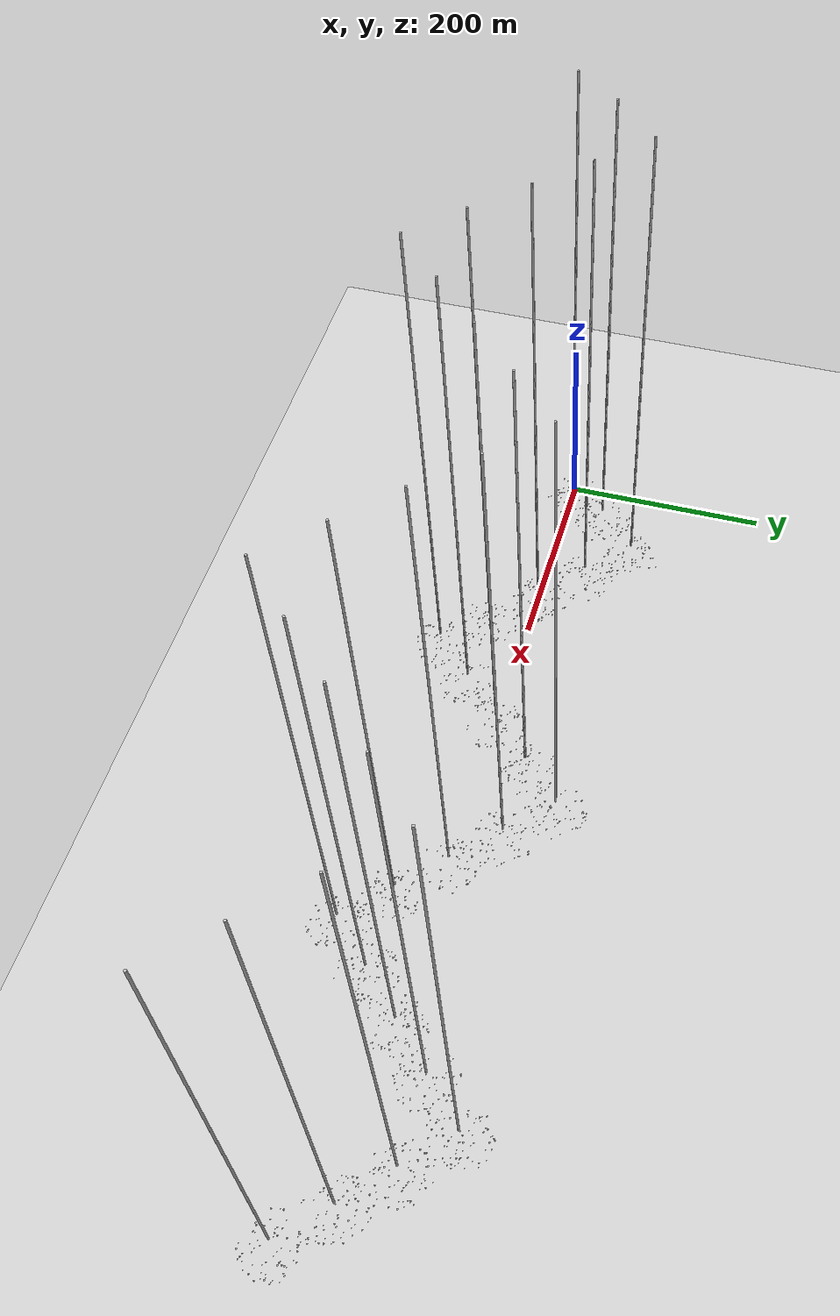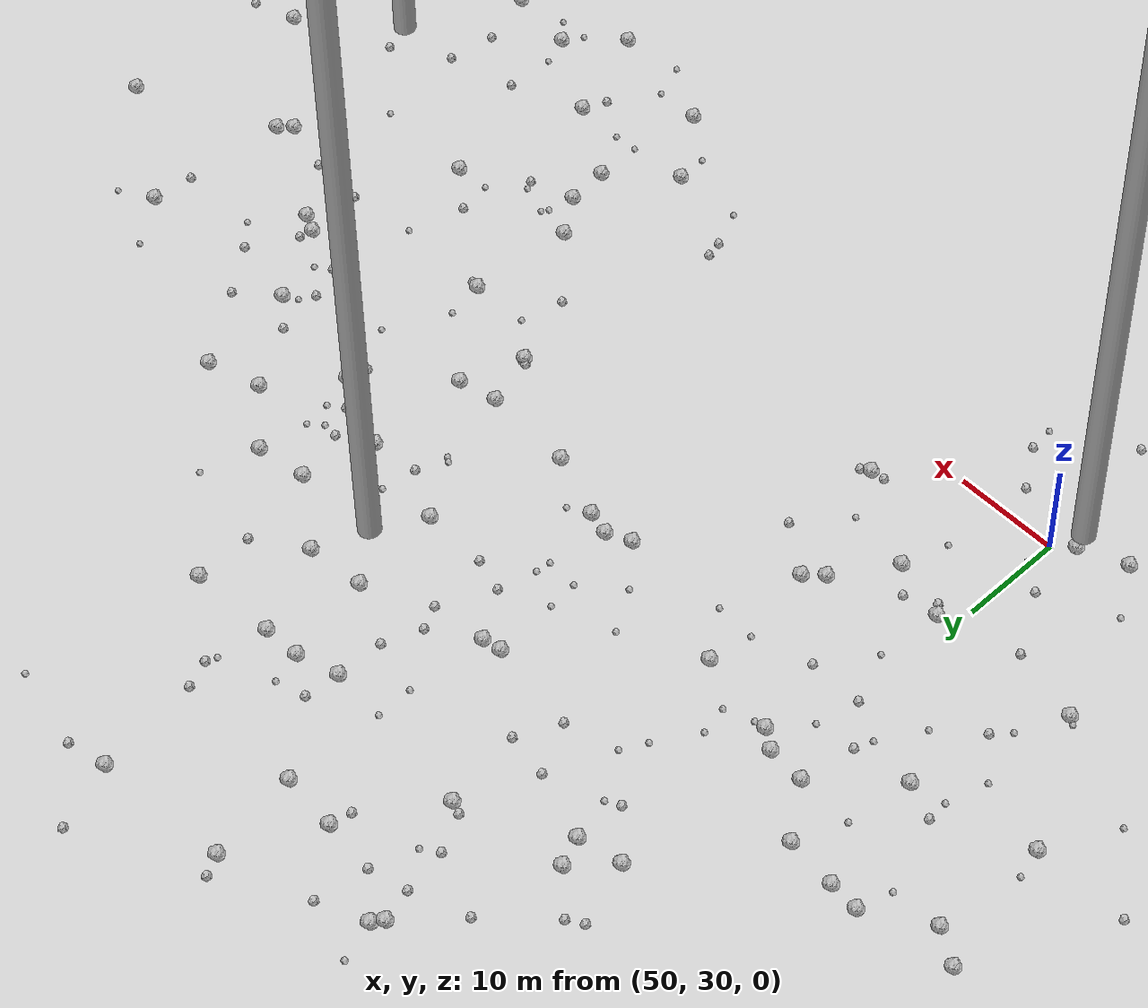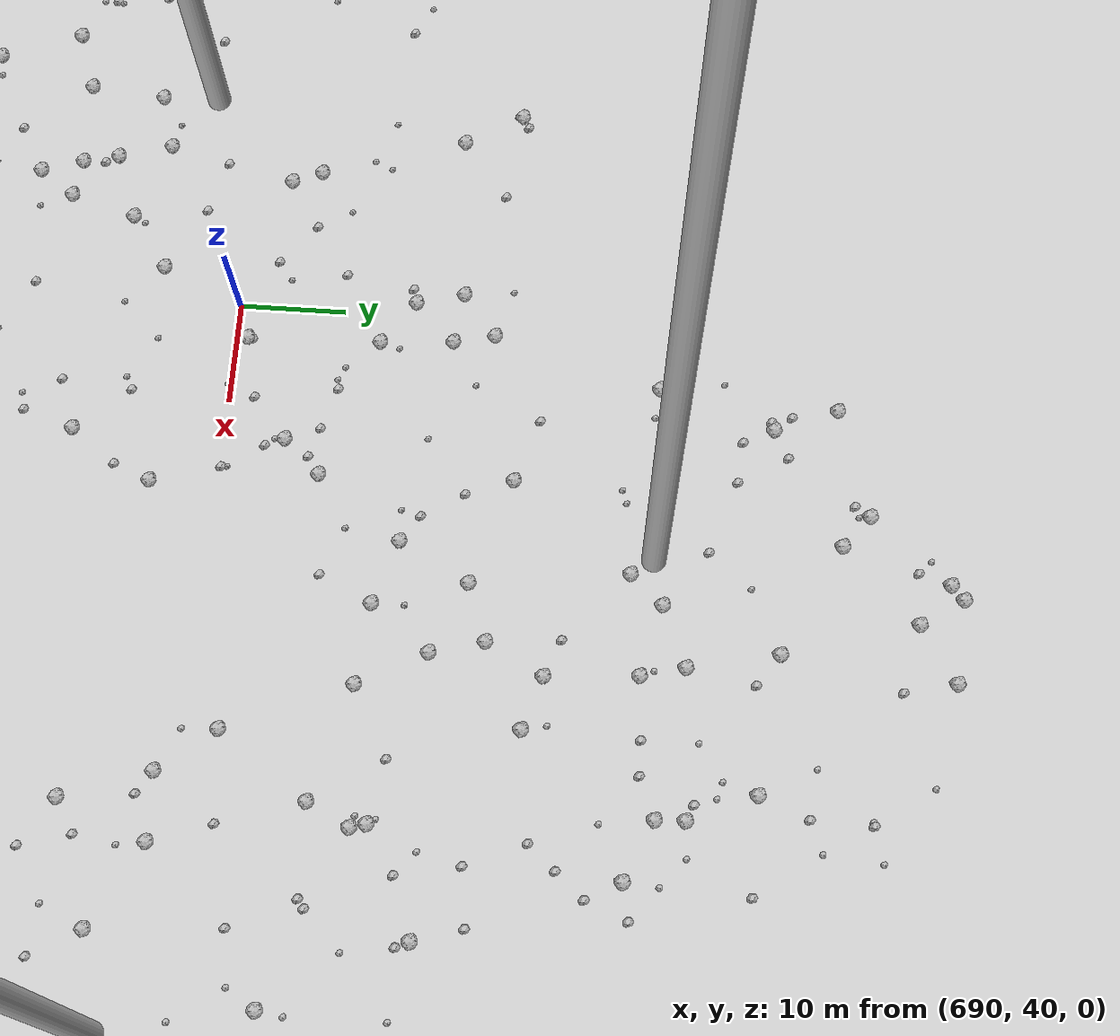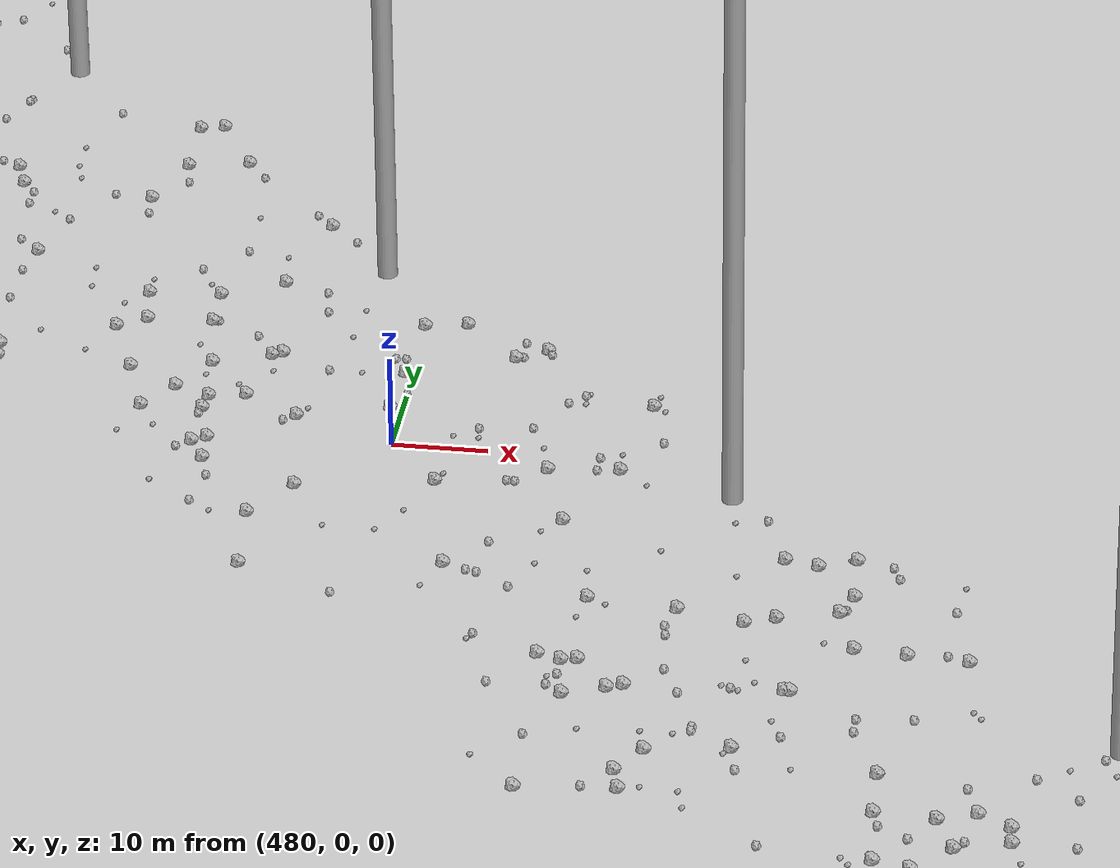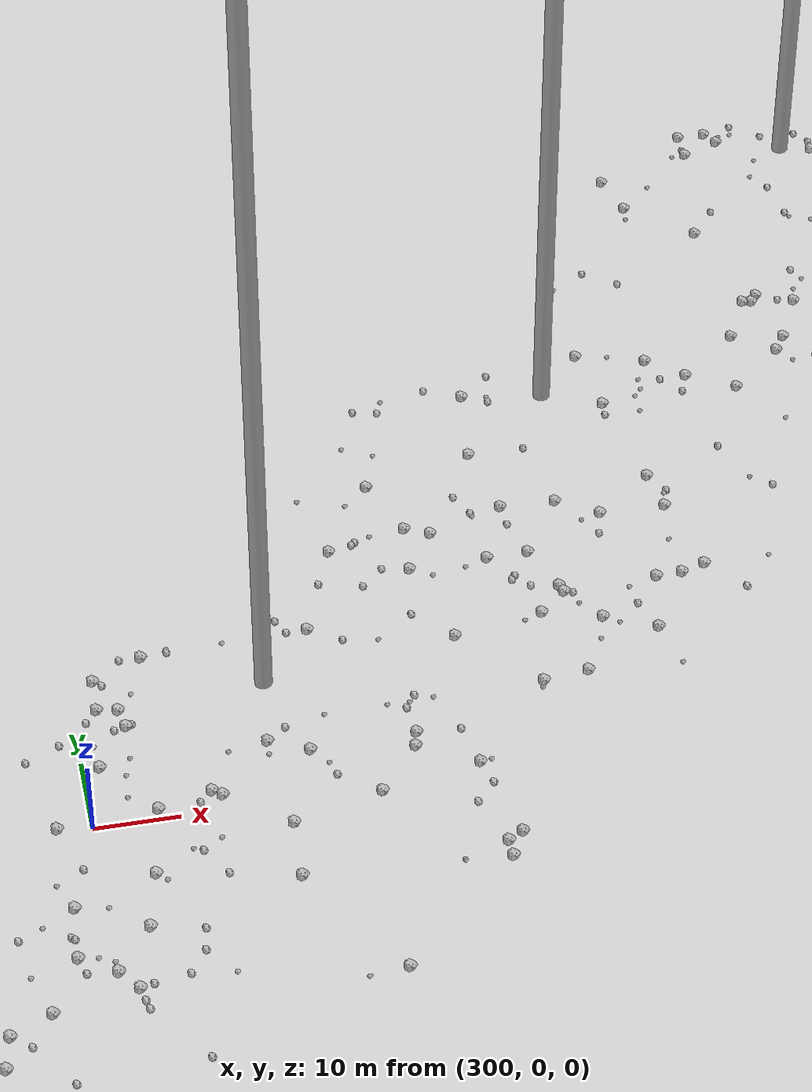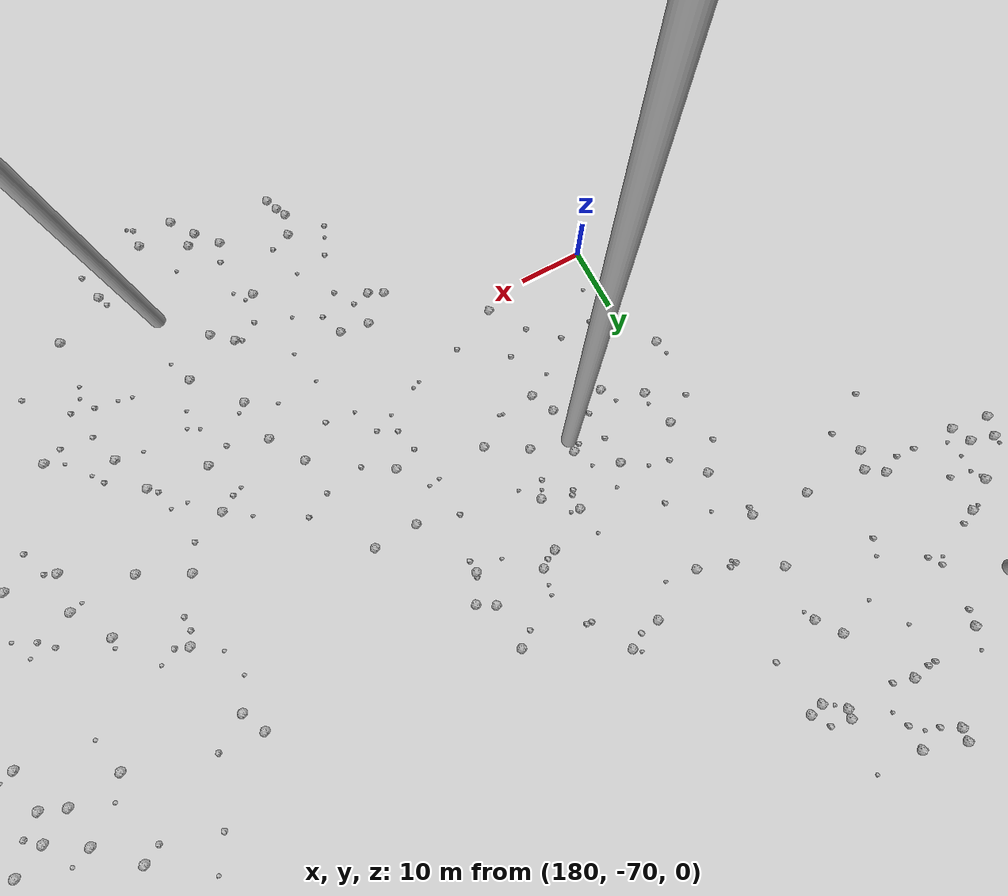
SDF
<sdf version="1.6">
 <world name="default">
  <include><uri>model://custom_ground</uri></include>
  <include><uri>model://sun</uri></include>
  <spherical_coordinates>
   <surface_model>EARTH_WGS84</surface_model>
   <latitude_deg>38.161479</latitude_deg>
   <longitude_deg>-122.454630</longitude_deg>
   <elevation>488.0</elevation>
   <heading_deg>90</heading_deg>
  </spherical_coordinates>
  <model name="rock1_0_0">
   <include><uri>model://rock1</uri><pose>9.456273186815217 -11.688796181936464 0.5 0 0 0</pose></include>
  </model>
  <model name="rock1_0_1">
   <include><uri>model://rock1</uri><pose>16.878218804001733 15.27838731786973 0.5 0 0 0</pose></include>
  </model>
  <model name="rock1_0_2">
   <include><uri>model://rock1</uri><pose>6.381972315248742 -16.44274774068992 0.5 0 0 0</pose></include>
  </model>
  <model name="rock1_0_3">
   <include><uri>model://rock1</uri><pose>7.293445581054151 5.079819756337287 0.5 0 0 0</pose></include>
  </model>
  <model name="rock1_0_4">
   <include><uri>model://rock1</uri><pose>12.91369826734644 27.325119133690244 0.5 0 0 0</pose></include>
  </model>
  <model name="rock1_0_5">
   <include><uri>model://rock1</uri><pose>9.132666323788975 -2.754366941554558 0.5 0 0 0</pose></include>
  </model>
  <model name="rock1_0_6">
   <include><uri>model://rock1</uri><pose>18.37801931052897 20.534127476050244 0.5 0 0 0</pose></include>
  </model>
  <model name="rock1_0_7">
   <include><uri>model://rock1</uri><pose>-3.328964837104042 1.1033009039148496 0.5 0 0 0</pose></include>
  </model>
  <model name="rock1_0_8">
   <include><uri>model://rock1</uri><pose>24.112519603297244 1.0547304435644698 0.5 0 0 0</pose></include>
  </model>
  <model name="rock1_0_9">
   <include><uri>model://rock1</uri><pose>8.429585677246973 3.28352805549941 0.5 0 0 0</pose></include>
  </model>
  <model name="rock1_0_10">
   <include><uri>model://rock1</uri><pose>5.089321775511657 -6.372729574876697 0.5 0 0 0</pose></include>
  </model>
  <model name="rock1_0_11">
   <include><uri>model://rock1</uri><pose>8.347047619984359 -9.528561057278633 0.5 0 0 0</pose></include>
  </model>
  <model name="rock1_0_12">
   <include><uri>model://rock1</uri><pose>31.588227256498655 -13.05245696007421 0.5 0 0 0</pose></include>
  </model>
  <model name="rock1_0_13">
   <include><uri>model://rock1</uri><pose>23.990816338459787 -12.57193776089671 0.5 0 0 0</pose></include>
  </model>
  <model name="rock1_0_14">
   <include><uri>model://rock1</uri><pose>9.995216663405817 -14.715657607923674 0.5 0 0 0</pose></include>
  </model>
  <model name="rock1_0_15">
   <include><uri>model://rock1</uri><pose>3.481509664779125 5.870696250098369 0.5 0 0 0</pose></include>
  </model>
  <model name="rock1_0_16">
   <include><uri>model://rock1</uri><pose>29.16402622712171 8.209084573943002 0.5 0 0 0</pose></include>
  </model>
  <model name="rock1_0_17">
   <include><uri>model://rock1</uri><pose>6.336525734762301 8.527845165872876 0.5 0 0 0</pose></include>
  </model>
  <model name="rock1_0_18">
   <include><uri>model://rock1</uri><pose>2.8568520097241716 -12.169391991035038 0.5 0 0 0</pose></include>
  </model>
  <model name="rock1_0_19">
   <include><uri>model://rock1</uri><pose>21.974629759424673 -5.588287762392472 0.5 0 0 0</pose></include>
  </model>
  <model name="rock1_0_20">
   <include><uri>model://rock1</uri><pose>17.39203344220683 -22.08519766136275 0.5 0 0 0</pose></include>
  </model>
  <model name="rock1_0_21">
   <include><uri>model://rock1</uri><pose>-11.105048722679172 -14.79687915960021 0.5 0 0 0</pose></include>
  </model>
  <model name="rock1_0_22">
   <include><uri>model://rock1</uri><pose>6.7992909576788705 -0.8716018166381758 0.5 0 0 0</pose></include>
  </model>
  <model name="rock1_0_23">
   <include><uri>model://rock1</uri><pose>34.5626180673482 -13.833773444420192 0.5 0 0 0</pose></include>
  </model>
  <model name="rock1_0_24">
   <include><uri>model://rock1</uri><pose>6.978674182314229 -19.2657952175756 0.5 0 0 0</pose></include>
  </model>
  <model name="rock1_0_25">
   <include><uri>model://rock1</uri><pose>-0.1570774088243425 24.602273540834283 0.5 0 0 0</pose></include>
  </model>
  <model name="rock1_0_26">
   <include><uri>model://rock1</uri><pose>26.244291648714757 20.89575630567822 0.5 0 0 0</pose></include>
  </model>
  <model name="rock2_0_0">
   <include><uri>model://rock2</uri><pose>15.172144779333578 8.767489282553846 0.3 0 0 0</pose></include>
  </model>
  <model name="rock2_0_1">
   <include><uri>model://rock2</uri><pose>31.192402929998494 -3.1204359104904285 0.3 0 0 0</pose></include>
  </model>
  <model name="rock2_0_2">
   <include><uri>model://rock2</uri><pose>16.855983082334554 11.767069334399565 0.3 0 0 0</pose></include>
  </model>
  <model name="rock2_0_3">
   <include><uri>model://rock2</uri><pose>24.489311506575106 12.630268721620055 0.3 0 0 0</pose></include>
  </model>
  <model name="rock2_0_4">
   <include><uri>model://rock2</uri><pose>6.105528943785842 -13.747268115387751 0.3 0 0 0</pose></include>
  </model>
  <model name="rock2_0_5">
   <include><uri>model://rock2</uri><pose>20.370026305977376 0.5322283803814862 0.3 0 0 0</pose></include>
  </model>
  <model name="rock2_0_6">
   <include><uri>model://rock2</uri><pose>23.36279257269294 -12.061646578117113 0.3 0 0 0</pose></include>
  </model>
  <model name="rock2_0_7">
   <include><uri>model://rock2</uri><pose>27.185180120222626 4.47135081229677 0.3 0 0 0</pose></include>
  </model>
  <model name="rock2_0_8">
   <include><uri>model://rock2</uri><pose>11.34932167390675 -13.854176106242608 0.3 0 0 0</pose></include>
  </model>
  <model name="rock2_0_9">
   <include><uri>model://rock2</uri><pose>16.732292987908693 -11.654028496498505 0.3 0 0 0</pose></include>
  </model>
  <model name="rock2_0_10">
   <include><uri>model://rock2</uri><pose>9.691135162872403 3.3904268086052696 0.3 0 0 0</pose></include>
  </model>
  <model name="rock2_0_11">
   <include><uri>model://rock2</uri><pose>12.250437913916478 -27.36101970418768 0.3 0 0 0</pose></include>
  </model>
  <model name="rock2_0_12">
   <include><uri>model://rock2</uri><pose>25.404355304838973 14.985654281102335 0.3 0 0 0</pose></include>
  </model>
  <model name="rock2_0_13">
   <include><uri>model://rock2</uri><pose>-0.6456263339581234 -7.03814797379189 0.3 0 0 0</pose></include>
  </model>
  <model name="rock2_0_14">
   <include><uri>model://rock2</uri><pose>-3.0990604946887466 -23.006832272040697 0.3 0 0 0</pose></include>
  </model>
  <model name="rock2_0_15">
   <include><uri>model://rock2</uri><pose>25.13813949679021 -14.00960891511815 0.3 0 0 0</pose></include>
  </model>
  <model name="rock2_0_16">
   <include><uri>model://rock2</uri><pose>19.34381670393978 -15.428928450674928 0.3 0 0 0</pose></include>
  </model>
  <model name="rock2_0_17">
   <include><uri>model://rock2</uri><pose>-5.373858103546965 -5.002009296055 0.3 0 0 0</pose></include>
  </model>
  <model name="rock2_0_18">
   <include><uri>model://rock2</uri><pose>33.60941727529313 17.980051811985142 0.3 0 0 0</pose></include>
  </model>
  <model name="rock2_0_19">
   <include><uri>model://rock2</uri><pose>29.84618764216068 21.268109431182864 0.3 0 0 0</pose></include>
  </model>
  <model name="rock2_0_20">
   <include><uri>model://rock2</uri><pose>26.24285261323743 22.3747472481377 0.3 0 0 0</pose></include>
  </model>
  <model name="rock2_0_21">
   <include><uri>model://rock2</uri><pose>18.499547564932264 -24.910305806606345 0.3 0 0 0</pose></include>
  </model>
  <model name="rock2_0_22">
   <include><uri>model://rock2</uri><pose>36.15911639545406 -6.503279898045758 0.3 0 0 0</pose></include>
  </model>
  <model name="rock2_0_23">
   <include><uri>model://rock2</uri><pose>0.30972231442400755 10.30511590467384 0.3 0 0 0</pose></include>
  </model>
  <model name="rock2_0_24">
   <include><uri>model://rock2</uri><pose>20.747716685516778 -18.830525031631076 0.3 0 0 0</pose></include>
  </model>
  <model name="rock2_0_25">
   <include><uri>model://rock2</uri><pose>11.068727314990511 22.725590245681865 0.3 0 0 0</pose></include>
  </model>
  <model name="rock2_0_26">
   <include><uri>model://rock2</uri><pose>35.568870098982046 -4.137860274172041 0.3 0 0 0</pose></include>
  </model>
  <model name="rock3_0_0">
   <include><uri>model://rock3</uri><pose>16.334258567376672 -0.9345502477439673 0.2 0 0 0</pose></include>
  </model>
  <model name="rock3_0_1">
   <include><uri>model://rock3</uri><pose>22.743366099234876 -4.258311976519842 0.2 0 0 0</pose></include>
  </model>
  <model name="rock3_0_2">
   <include><uri>model://rock3</uri><pose>6.468916937182424 27.430095560538746 0.2 0 0 0</pose></include>
  </model>
  <model name="rock3_0_3">
   <include><uri>model://rock3</uri><pose>17.48269475359755 10.596588348535832 0.2 0 0 0</pose></include>
  </model>
  <model name="rock3_0_4">
   <include><uri>model://rock3</uri><pose>-1.9204098800158995 17.15985401480262 0.2 0 0 0</pose></include>
  </model>
  <model name="rock3_0_5">
   <include><uri>model://rock3</uri><pose>21.360253094917155 16.223275306143172 0.2 0 0 0</pose></include>
  </model>
  <model name="rock3_0_6">
   <include><uri>model://rock3</uri><pose>10.745836889679062 -17.667056466617808 0.2 0 0 0</pose></include>
  </model>
  <model name="rock3_0_7">
   <include><uri>model://rock3</uri><pose>18.726462869271558 4.141150419744534 0.2 0 0 0</pose></include>
  </model>
  <model name="rock3_0_8">
   <include><uri>model://rock3</uri><pose>13.469702529121577 -15.31665790325247 0.2 0 0 0</pose></include>
  </model>
  <model name="rock3_0_9">
   <include><uri>model://rock3</uri><pose>-5.4456764519126555 12.771731939468346 0.2 0 0 0</pose></include>
  </model>
  <model name="rock3_0_10">
   <include><uri>model://rock3</uri><pose>5.825219647729426 26.453810218387453 0.2 0 0 0</pose></include>
  </model>
  <model name="rock3_0_11">
   <include><uri>model://rock3</uri><pose>-10.914895585720473 -19.659069859868204 0.2 0 0 0</pose></include>
  </model>
  <model name="rock3_0_12">
   <include><uri>model://rock3</uri><pose>-8.462914747040774 23.570890111581043 0.2 0 0 0</pose></include>
  </model>
  <model name="rock3_0_13">
   <include><uri>model://rock3</uri><pose>6.146201208390135 29.067606732032502 0.2 0 0 0</pose></include>
  </model>
  <model name="rock3_0_14">
   <include><uri>model://rock3</uri><pose>-13.977467525174712 16.346365310270322 0.2 0 0 0</pose></include>
  </model>
  <model name="rock3_0_15">
   <include><uri>model://rock3</uri><pose>3.5522162609765715 -13.350191725581386 0.2 0 0 0</pose></include>
  </model>
  <model name="rock3_0_16">
   <include><uri>model://rock3</uri><pose>16.36887477302207 13.314558713649461 0.2 0 0 0</pose></include>
  </model>
  <model name="rock3_0_17">
   <include><uri>model://rock3</uri><pose>-5.911871243917503 -2.7134592194944105 0.2 0 0 0</pose></include>
  </model>
  <model name="rock3_0_18">
   <include><uri>model://rock3</uri><pose>22.290049001782762 1.105174465554441 0.2 0 0 0</pose></include>
  </model>
  <model name="rock3_0_19">
   <include><uri>model://rock3</uri><pose>-10.523128003819355 -14.159505794139264 0.2 0 0 0</pose></include>
  </model>
  <model name="rock3_0_20">
   <include><uri>model://rock3</uri><pose>26.058073388734307 12.533643612031163 0.2 0 0 0</pose></include>
  </model>
  <model name="rock3_0_21">
   <include><uri>model://rock3</uri><pose>28.625825824275907 -11.708967911527097 0.2 0 0 0</pose></include>
  </model>
  <model name="rock3_0_22">
   <include><uri>model://rock3</uri><pose>-9.181037094188852 -10.112575663012016 0.2 0 0 0</pose></include>
  </model>
  <model name="rock3_0_23">
   <include><uri>model://rock3</uri><pose>35.28852726269419 15.184024275190481 0.2 0 0 0</pose></include>
  </model>
  <model name="rock3_0_24">
   <include><uri>model://rock3</uri><pose>4.273935025220975 20.662875518663625 0.2 0 0 0</pose></include>
  </model>
  <model name="rock3_0_25">
   <include><uri>model://rock3</uri><pose>-5.642216528037263 17.81795776607624 0.2 0 0 0</pose></include>
  </model>
  <model name="rock3_0_26">
   <include><uri>model://rock3</uri><pose>4.482138113324957 22.3576050235568 0.2 0 0 0</pose></include>
  </model>
  <model name="rock1_1_0">
   <include><uri>model://rock1</uri><pose>41.75406184555179 56.647843177053375 0.5 0 0 0</pose></include>
  </model>
  <model name="rock1_1_1">
   <include><uri>model://rock1</uri><pose>62.74483449671117 47.68078615139128 0.5 0 0 0</pose></include>
  </model>
  <model name="rock1_1_2">
   <include><uri>model://rock1</uri><pose>30.147128356997722 54.10750234484801 0.5 0 0 0</pose></include>
  </model>
  <model name="rock1_1_3">
   <include><uri>model://rock1</uri><pose>61.17246335997775 46.19553218624335 0.5 0 0 0</pose></include>
  </model>
  <model name="rock1_1_4">
   <include><uri>model://rock1</uri><pose>43.428481309165996 13.070317475206553 0.5 0 0 0</pose></include>
  </model>
  <model name="rock1_1_5">
   <include><uri>model://rock1</uri><pose>13.491933819645999 30.977068791058144 0.5 0 0 0</pose></include>
  </model>
  <model name="rock1_1_6">
   <include><uri>model://rock1</uri><pose>44.58897505501513 67.69496962771191 0.5 0 0 0</pose></include>
  </model>
  <model name="rock1_1_7">
   <include><uri>model://rock1</uri><pose>48.21885242809256 62.77888855577668 0.5 0 0 0</pose></include>
  </model>
  <model name="rock1_1_8">
   <include><uri>model://rock1</uri><pose>22.229369805012258 35.96904334112533 0.5 0 0 0</pose></include>
  </model>
  <model name="rock1_1_9">
   <include><uri>model://rock1</uri><pose>37.00845480108734 42.32482336371347 0.5 0 0 0</pose></include>
  </model>
  <model name="rock1_1_10">
   <include><uri>model://rock1</uri><pose>27.589893813327045 66.95247444572534 0.5 0 0 0</pose></include>
  </model>
  <model name="rock1_1_11">
   <include><uri>model://rock1</uri><pose>10.623794735295565 45.893323908080866 0.5 0 0 0</pose></include>
  </model>
  <model name="rock1_1_12">
   <include><uri>model://rock1</uri><pose>21.795252778826864 22.578209949798953 0.5 0 0 0</pose></include>
  </model>
  <model name="rock1_1_13">
   <include><uri>model://rock1</uri><pose>39.57910534664386 68.2707183099807 0.5 0 0 0</pose></include>
  </model>
  <model name="rock1_1_14">
   <include><uri>model://rock1</uri><pose>48.268441283786444 28.671889399159134 0.5 0 0 0</pose></include>
  </model>
  <model name="rock1_1_15">
   <include><uri>model://rock1</uri><pose>34.37091203949603 29.46231899049815 0.5 0 0 0</pose></include>
  </model>
  <model name="rock1_1_16">
   <include><uri>model://rock1</uri><pose>16.23115107499746 53.03509603725111 0.5 0 0 0</pose></include>
  </model>
  <model name="rock1_1_17">
   <include><uri>model://rock1</uri><pose>30.830471265477147 64.97344951473427 0.5 0 0 0</pose></include>
  </model>
  <model name="rock1_1_18">
   <include><uri>model://rock1</uri><pose>51.72710627623598 42.56690272461223 0.5 0 0 0</pose></include>
  </model>
  <model name="rock1_1_19">
   <include><uri>model://rock1</uri><pose>51.97646874702582 62.4642818031211 0.5 0 0 0</pose></include>
  </model>
  <model name="rock1_1_20">
   <include><uri>model://rock1</uri><pose>34.59064868813003 31.463340020634742 0.5 0 0 0</pose></include>
  </model>
  <model name="rock1_1_21">
   <include><uri>model://rock1</uri><pose>66.34261497034902 35.13315969316788 0.5 0 0 0</pose></include>
  </model>
  <model name="rock1_1_22">
   <include><uri>model://rock1</uri><pose>36.59927192486481 68.53452882410028 0.5 0 0 0</pose></include>
  </model>
  <model name="rock1_1_23">
   <include><uri>model://rock1</uri><pose>53.83367623204765 61.18843223299812 0.5 0 0 0</pose></include>
  </model>
  <model name="rock1_1_24">
   <include><uri>model://rock1</uri><pose>57.52011825171607 40.710536342449096 0.5 0 0 0</pose></include>
  </model>
  <model name="rock1_1_25">
   <include><uri>model://rock1</uri><pose>43.80286744690895 26.941689869535615 0.5 0 0 0</pose></include>
  </model>
  <model name="rock1_1_26">
   <include><uri>model://rock1</uri><pose>13.88241716746214 33.10211816967001 0.5 0 0 0</pose></include>
  </model>
  <model name="rock2_1_0">
   <include><uri>model://rock2</uri><pose>31.731835428948024 31.266862836374425 0.3 0 0 0</pose></include>
  </model>
  <model name="rock2_1_1">
   <include><uri>model://rock2</uri><pose>29.738519148413143 25.873052063220534 0.3 0 0 0</pose></include>
  </model>
  <model name="rock2_1_2">
   <include><uri>model://rock2</uri><pose>52.45819939420707 41.54679862856203 0.3 0 0 0</pose></include>
  </model>
  <model name="rock2_1_3">
   <include><uri>model://rock2</uri><pose>64.96349987786444 34.93229191723541 0.3 0 0 0</pose></include>
  </model>
  <model name="rock2_1_4">
   <include><uri>model://rock2</uri><pose>33.81125970106216 16.51215486769064 0.3 0 0 0</pose></include>
  </model>
  <model name="rock2_1_5">
   <include><uri>model://rock2</uri><pose>29.906742724758196 34.233575769404204 0.3 0 0 0</pose></include>
  </model>
  <model name="rock2_1_6">
   <include><uri>model://rock2</uri><pose>50.26837430480875 53.70578935026938 0.3 0 0 0</pose></include>
  </model>
  <model name="rock2_1_7">
   <include><uri>model://rock2</uri><pose>34.744957366824494 31.389414506488404 0.3 0 0 0</pose></include>
  </model>
  <model name="rock2_1_8">
   <include><uri>model://rock2</uri><pose>38.27775300332628 58.0649325214745 0.3 0 0 0</pose></include>
  </model>
  <model name="rock2_1_9">
   <include><uri>model://rock2</uri><pose>58.187715593870955 23.01760269855322 0.3 0 0 0</pose></include>
  </model>
  <model name="rock2_1_10">
   <include><uri>model://rock2</uri><pose>16.311507006965375 46.062772980345386 0.3 0 0 0</pose></include>
  </model>
  <model name="rock2_1_11">
   <include><uri>model://rock2</uri><pose>40.49635721374492 48.39782118448008 0.3 0 0 0</pose></include>
  </model>
  <model name="rock2_1_12">
   <include><uri>model://rock2</uri><pose>37.16952559905117 13.107850905389228 0.3 0 0 0</pose></include>
  </model>
  <model name="rock2_1_13">
   <include><uri>model://rock2</uri><pose>44.07226730961664 40.482172184252654 0.3 0 0 0</pose></include>
  </model>
  <model name="rock2_1_14">
   <include><uri>model://rock2</uri><pose>47.30970167229127 57.40864321884704 0.3 0 0 0</pose></include>
  </model>
  <model name="rock2_1_15">
   <include><uri>model://rock2</uri><pose>55.172260364322966 43.01723014916399 0.3 0 0 0</pose></include>
  </model>
  <model name="rock2_1_16">
   <include><uri>model://rock2</uri><pose>67.37682543766033 44.31962573069376 0.3 0 0 0</pose></include>
  </model>
  <model name="rock2_1_17">
   <include><uri>model://rock2</uri><pose>47.515769039372216 34.74571874667972 0.3 0 0 0</pose></include>
  </model>
  <model name="rock2_1_18">
   <include><uri>model://rock2</uri><pose>55.56283345843271 53.68760120190179 0.3 0 0 0</pose></include>
  </model>
  <model name="rock2_1_19">
   <include><uri>model://rock2</uri><pose>51.40029316366649 16.419526735957177 0.3 0 0 0</pose></include>
  </model>
  <model name="rock2_1_20">
   <include><uri>model://rock2</uri><pose>49.99618196072927 32.88500530511904 0.3 0 0 0</pose></include>
  </model>
  <model name="rock2_1_21">
   <include><uri>model://rock2</uri><pose>20.994609020621887 54.02046412719433 0.3 0 0 0</pose></include>
  </model>
  <model name="rock2_1_22">
   <include><uri>model://rock2</uri><pose>36.57563260645938 17.866753988855272 0.3 0 0 0</pose></include>
  </model>
  <model name="rock2_1_23">
   <include><uri>model://rock2</uri><pose>43.87272075141205 14.747847935384764 0.3 0 0 0</pose></include>
  </model>
  <model name="rock2_1_24">
   <include><uri>model://rock2</uri><pose>67.17802437796368 35.61155812606164 0.3 0 0 0</pose></include>
  </model>
  <model name="rock2_1_25">
   <include><uri>model://rock2</uri><pose>55.594676499781364 26.849660625974394 0.3 0 0 0</pose></include>
  </model>
  <model name="rock2_1_26">
   <include><uri>model://rock2</uri><pose>46.95585650009847 12.646442536269271 0.3 0 0 0</pose></include>
  </model>
  <model name="rock3_1_0">
   <include><uri>model://rock3</uri><pose>52.24692393486652 48.79827480589348 0.2 0 0 0</pose></include>
  </model>
  <model name="rock3_1_1">
   <include><uri>model://rock3</uri><pose>51.19221858993635 57.76411571369117 0.2 0 0 0</pose></include>
  </model>
  <model name="rock3_1_2">
   <include><uri>model://rock3</uri><pose>48.52140910345739 62.831883180541894 0.2 0 0 0</pose></include>
  </model>
  <model name="rock3_1_3">
   <include><uri>model://rock3</uri><pose>54.90531356205694 61.22951640104209 0.2 0 0 0</pose></include>
  </model>
  <model name="rock3_1_4">
   <include><uri>model://rock3</uri><pose>40.68683738468576 31.545546416859626 0.2 0 0 0</pose></include>
  </model>
  <model name="rock3_1_5">
   <include><uri>model://rock3</uri><pose>48.48110089747347 62.74575772053255 0.2 0 0 0</pose></include>
  </model>
  <model name="rock3_1_6">
   <include><uri>model://rock3</uri><pose>26.66866956776343 47.416454808689 0.2 0 0 0</pose></include>
  </model>
  <model name="rock3_1_7">
   <include><uri>model://rock3</uri><pose>61.2014522523327 55.23269482947404 0.2 0 0 0</pose></include>
  </model>
  <model name="rock3_1_8">
   <include><uri>model://rock3</uri><pose>56.12905289620906 36.20662401081529 0.2 0 0 0</pose></include>
  </model>
  <model name="rock3_1_9">
   <include><uri>model://rock3</uri><pose>38.496488036945266 18.898367017317902 0.2 0 0 0</pose></include>
  </model>
  <model name="rock3_1_10">
   <include><uri>model://rock3</uri><pose>46.67307518329913 55.63948635453319 0.2 0 0 0</pose></include>
  </model>
  <model name="rock3_1_11">
   <include><uri>model://rock3</uri><pose>35.61457248541212 65.15536708992013 0.2 0 0 0</pose></include>
  </model>
  <model name="rock3_1_12">
   <include><uri>model://rock3</uri><pose>28.727692047903066 29.494954402241383 0.2 0 0 0</pose></include>
  </model>
  <model name="rock3_1_13">
   <include><uri>model://rock3</uri><pose>30.896354294441036 29.297827627609024 0.2 0 0 0</pose></include>
  </model>
  <model name="rock3_1_14">
   <include><uri>model://rock3</uri><pose>42.65461954655572 62.902428822853594 0.2 0 0 0</pose></include>
  </model>
  <model name="rock3_1_15">
   <include><uri>model://rock3</uri><pose>26.675567064204607 38.744819518959375 0.2 0 0 0</pose></include>
  </model>
  <model name="rock3_1_16">
   <include><uri>model://rock3</uri><pose>38.399985109143486 55.946330039433505 0.2 0 0 0</pose></include>
  </model>
  <model name="rock3_1_17">
   <include><uri>model://rock3</uri><pose>37.260469696431954 51.99387046541537 0.2 0 0 0</pose></include>
  </model>
  <model name="rock3_1_18">
   <include><uri>model://rock3</uri><pose>29.42363457296292 56.82350944003182 0.2 0 0 0</pose></include>
  </model>
  <model name="rock3_1_19">
   <include><uri>model://rock3</uri><pose>39.136825424036935 46.76476132704953 0.2 0 0 0</pose></include>
  </model>
  <model name="rock3_1_20">
   <include><uri>model://rock3</uri><pose>58.459559799065424 20.512283440752324 0.2 0 0 0</pose></include>
  </model>
  <model name="rock3_1_21">
   <include><uri>model://rock3</uri><pose>36.27868293055689 42.69864751427983 0.2 0 0 0</pose></include>
  </model>
  <model name="rock3_1_22">
   <include><uri>model://rock3</uri><pose>65.14841469314774 55.02851213523932 0.2 0 0 0</pose></include>
  </model>
  <model name="rock3_1_23">
   <include><uri>model://rock3</uri><pose>57.64294636341263 62.21533480124703 0.2 0 0 0</pose></include>
  </model>
  <model name="rock3_1_24">
   <include><uri>model://rock3</uri><pose>44.23007258051504 51.59808728613737 0.2 0 0 0</pose></include>
  </model>
  <model name="rock3_1_25">
   <include><uri>model://rock3</uri><pose>63.76980824023954 39.6867543712884 0.2 0 0 0</pose></include>
  </model>
  <model name="rock3_1_26">
   <include><uri>model://rock3</uri><pose>49.85144365591145 32.633940027679344 0.2 0 0 0</pose></include>
  </model>
  <model name="rock1_2_0">
   <include><uri>model://rock1</uri><pose>71.9100264846717 93.17325366201969 0.5 0 0 0</pose></include>
  </model>
  <model name="rock1_2_1">
   <include><uri>model://rock1</uri><pose>94.06424397938764 75.70847167025434 0.5 0 0 0</pose></include>
  </model>
  <model name="rock1_2_2">
   <include><uri>model://rock1</uri><pose>61.961384372795685 59.53682177095616 0.5 0 0 0</pose></include>
  </model>
  <model name="rock1_2_3">
   <include><uri>model://rock1</uri><pose>88.40772279015911 75.20256912909252 0.5 0 0 0</pose></include>
  </model>
  <model name="rock1_2_4">
   <include><uri>model://rock1</uri><pose>105.59141372641699 71.5939919028834 0.5 0 0 0</pose></include>
  </model>
  <model name="rock1_2_5">
   <include><uri>model://rock1</uri><pose>56.9400632885437 79.68217508137816 0.5 0 0 0</pose></include>
  </model>
  <model name="rock1_2_6">
   <include><uri>model://rock1</uri><pose>98.94235387654481 63.98918548408608 0.5 0 0 0</pose></include>
  </model>
  <model name="rock1_2_7">
   <include><uri>model://rock1</uri><pose>75.39034782087117 55.450573980543915 0.5 0 0 0</pose></include>
  </model>
  <model name="rock1_2_8">
   <include><uri>model://rock1</uri><pose>89.13556451414689 102.42919058629133 0.5 0 0 0</pose></include>
  </model>
  <model name="rock1_2_9">
   <include><uri>model://rock1</uri><pose>77.71307928788214 56.44437613533282 0.5 0 0 0</pose></include>
  </model>
  <model name="rock1_2_10">
   <include><uri>model://rock1</uri><pose>89.51866718882707 66.04604989417837 0.5 0 0 0</pose></include>
  </model>
  <model name="rock1_2_11">
   <include><uri>model://rock1</uri><pose>90.25903286809982 84.00841529886404 0.5 0 0 0</pose></include>
  </model>
  <model name="rock1_2_12">
   <include><uri>model://rock1</uri><pose>82.54857033877518 82.77655153726585 0.5 0 0 0</pose></include>
  </model>
  <model name="rock1_2_13">
   <include><uri>model://rock1</uri><pose>98.59142721968522 84.4209212794336 0.5 0 0 0</pose></include>
  </model>
  <model name="rock1_2_14">
   <include><uri>model://rock1</uri><pose>74.92190990299035 71.37815627234872 0.5 0 0 0</pose></include>
  </model>
  <model name="rock1_2_15">
   <include><uri>model://rock1</uri><pose>86.30973755141405 53.5127724461816 0.5 0 0 0</pose></include>
  </model>
  <model name="rock1_2_16">
   <include><uri>model://rock1</uri><pose>80.03953023288949 55.84014042723678 0.5 0 0 0</pose></include>
  </model>
  <model name="rock1_2_17">
   <include><uri>model://rock1</uri><pose>77.50075470648918 92.62707507695984 0.5 0 0 0</pose></include>
  </model>
  <model name="rock1_2_18">
   <include><uri>model://rock1</uri><pose>66.56317005608744 84.54871564083449 0.5 0 0 0</pose></include>
  </model>
  <model name="rock1_2_19">
   <include><uri>model://rock1</uri><pose>86.58206641136302 83.9099956838314 0.5 0 0 0</pose></include>
  </model>
  <model name="rock1_2_20">
   <include><uri>model://rock1</uri><pose>76.76286101506003 71.6934417047589 0.5 0 0 0</pose></include>
  </model>
  <model name="rock1_2_21">
   <include><uri>model://rock1</uri><pose>52.66941071439747 78.86202495092122 0.5 0 0 0</pose></include>
  </model>
  <model name="rock1_2_22">
   <include><uri>model://rock1</uri><pose>100.70024333958261 70.87015831662592 0.5 0 0 0</pose></include>
  </model>
  <model name="rock1_2_23">
   <include><uri>model://rock1</uri><pose>55.8662372140333 82.40405577115867 0.5 0 0 0</pose></include>
  </model>
  <model name="rock1_2_24">
   <include><uri>model://rock1</uri><pose>62.74350992121866 97.0001330922683 0.5 0 0 0</pose></include>
  </model>
  <model name="rock1_2_25">
   <include><uri>model://rock1</uri><pose>76.11428500704515 101.48908236523215 0.5 0 0 0</pose></include>
  </model>
  <model name="rock1_2_26">
   <include><uri>model://rock1</uri><pose>62.01157915338539 95.98419784188945 0.5 0 0 0</pose></include>
  </model>
  <model name="rock2_2_0">
   <include><uri>model://rock2</uri><pose>50.630479489146495 84.83996375212456 0.3 0 0 0</pose></include>
  </model>
  <model name="rock2_2_1">
   <include><uri>model://rock2</uri><pose>92.93483081906376 103.16439419218902 0.3 0 0 0</pose></include>
  </model>
  <model name="rock2_2_2">
   <include><uri>model://rock2</uri><pose>63.433983651398506 77.43952773135258 0.3 0 0 0</pose></include>
  </model>
  <model name="rock2_2_3">
   <include><uri>model://rock2</uri><pose>90.3250228280089 92.39033261136001 0.3 0 0 0</pose></include>
  </model>
  <model name="rock2_2_4">
   <include><uri>model://rock2</uri><pose>67.75933529878556 76.71466291247813 0.3 0 0 0</pose></include>
  </model>
  <model name="rock2_2_5">
   <include><uri>model://rock2</uri><pose>71.47082728189608 91.07709088373426 0.3 0 0 0</pose></include>
  </model>
  <model name="rock2_2_6">
   <include><uri>model://rock2</uri><pose>67.34331863008015 98.79612386542627 0.3 0 0 0</pose></include>
  </model>
  <model name="rock2_2_7">
   <include><uri>model://rock2</uri><pose>91.36778942710687 89.77649870734012 0.3 0 0 0</pose></include>
  </model>
  <model name="rock2_2_8">
   <include><uri>model://rock2</uri><pose>82.82577562277777 86.15922561986869 0.3 0 0 0</pose></include>
  </model>
  <model name="rock2_2_9">
   <include><uri>model://rock2</uri><pose>82.42541622481295 78.08972548921052 0.3 0 0 0</pose></include>
  </model>
  <model name="rock2_2_10">
   <include><uri>model://rock2</uri><pose>98.71404158970819 78.7745944328787 0.3 0 0 0</pose></include>
  </model>
  <model name="rock2_2_11">
   <include><uri>model://rock2</uri><pose>102.07392235827167 65.8127084567183 0.3 0 0 0</pose></include>
  </model>
  <model name="rock2_2_12">
   <include><uri>model://rock2</uri><pose>79.7232201435162 67.1667703981897 0.3 0 0 0</pose></include>
  </model>
  <model name="rock2_2_13">
   <include><uri>model://rock2</uri><pose>65.32911440877778 84.93185228149385 0.3 0 0 0</pose></include>
  </model>
  <model name="rock2_2_14">
   <include><uri>model://rock2</uri><pose>52.0901687275167 85.72038400056161 0.3 0 0 0</pose></include>
  </model>
  <model name="rock2_2_15">
   <include><uri>model://rock2</uri><pose>75.09715008698845 103.37665660037885 0.3 0 0 0</pose></include>
  </model>
  <model name="rock2_2_16">
   <include><uri>model://rock2</uri><pose>82.15753845806609 72.2045468501359 0.3 0 0 0</pose></include>
  </model>
  <model name="rock2_2_17">
   <include><uri>model://rock2</uri><pose>83.02819843289191 66.19335096237471 0.3 0 0 0</pose></include>
  </model>
  <model name="rock2_2_18">
   <include><uri>model://rock2</uri><pose>94.26797613103746 63.421577961521 0.3 0 0 0</pose></include>
  </model>
  <model name="rock2_2_19">
   <include><uri>model://rock2</uri><pose>65.83370267699196 72.67193228164734 0.3 0 0 0</pose></include>
  </model>
  <model name="rock2_2_20">
   <include><uri>model://rock2</uri><pose>57.44406962366088 90.89715102745609 0.3 0 0 0</pose></include>
  </model>
  <model name="rock2_2_21">
   <include><uri>model://rock2</uri><pose>81.02834765933243 74.43375408303149 0.3 0 0 0</pose></include>
  </model>
  <model name="rock2_2_22">
   <include><uri>model://rock2</uri><pose>63.5806153229289 88.45652218631729 0.3 0 0 0</pose></include>
  </model>
  <model name="rock2_2_23">
   <include><uri>model://rock2</uri><pose>56.62988590603943 74.95046880478404 0.3 0 0 0</pose></include>
  </model>
  <model name="rock2_2_24">
   <include><uri>model://rock2</uri><pose>62.81797870562295 92.80576441626555 0.3 0 0 0</pose></include>
  </model>
  <model name="rock2_2_25">
   <include><uri>model://rock2</uri><pose>86.74750991943756 108.71079917240229 0.3 0 0 0</pose></include>
  </model>
  <model name="rock2_2_26">
   <include><uri>model://rock2</uri><pose>66.5804801113237 93.68470431345771 0.3 0 0 0</pose></include>
  </model>
  <model name="rock3_2_0">
   <include><uri>model://rock3</uri><pose>98.99311217568334 63.720599735531 0.2 0 0 0</pose></include>
  </model>
  <model name="rock3_2_1">
   <include><uri>model://rock3</uri><pose>65.12574035844627 89.42419235864031 0.2 0 0 0</pose></include>
  </model>
  <model name="rock3_2_2">
   <include><uri>model://rock3</uri><pose>75.56557602425954 62.14001999221476 0.2 0 0 0</pose></include>
  </model>
  <model name="rock3_2_3">
   <include><uri>model://rock3</uri><pose>71.91009474376561 59.088707748506486 0.2 0 0 0</pose></include>
  </model>
  <model name="rock3_2_4">
   <include><uri>model://rock3</uri><pose>78.69603864004941 61.95113333740313 0.2 0 0 0</pose></include>
  </model>
  <model name="rock3_2_5">
   <include><uri>model://rock3</uri><pose>105.22183864729121 63.977859931852606 0.2 0 0 0</pose></include>
  </model>
  <model name="rock3_2_6">
   <include><uri>model://rock3</uri><pose>69.503952386053 63.01411384912576 0.2 0 0 0</pose></include>
  </model>
  <model name="rock3_2_7">
   <include><uri>model://rock3</uri><pose>91.53301132370775 89.83133098758282 0.2 0 0 0</pose></include>
  </model>
  <model name="rock3_2_8">
   <include><uri>model://rock3</uri><pose>77.14293691862746 83.01636333884248 0.2 0 0 0</pose></include>
  </model>
  <model name="rock3_2_9">
   <include><uri>model://rock3</uri><pose>104.85505478287561 66.66266687870325 0.2 0 0 0</pose></include>
  </model>
  <model name="rock3_2_10">
   <include><uri>model://rock3</uri><pose>78.84095076957678 63.4044489451244 0.2 0 0 0</pose></include>
  </model>
  <model name="rock3_2_11">
   <include><uri>model://rock3</uri><pose>103.63956737319523 65.60468535242829 0.2 0 0 0</pose></include>
  </model>
  <model name="rock3_2_12">
   <include><uri>model://rock3</uri><pose>57.0483497314003 64.96614186177715 0.2 0 0 0</pose></include>
  </model>
  <model name="rock3_2_13">
   <include><uri>model://rock3</uri><pose>82.03925871517957 56.78764882379267 0.2 0 0 0</pose></include>
  </model>
  <model name="rock3_2_14">
   <include><uri>model://rock3</uri><pose>90.99049902055768 88.72159515717267 0.2 0 0 0</pose></include>
  </model>
  <model name="rock3_2_15">
   <include><uri>model://rock3</uri><pose>107.25904038177754 76.93104353450506 0.2 0 0 0</pose></include>
  </model>
  <model name="rock3_2_16">
   <include><uri>model://rock3</uri><pose>59.50815104873515 68.96394181184257 0.2 0 0 0</pose></include>
  </model>
  <model name="rock3_2_17">
   <include><uri>model://rock3</uri><pose>92.94855145809885 60.65970069305607 0.2 0 0 0</pose></include>
  </model>
  <model name="rock3_2_18">
   <include><uri>model://rock3</uri><pose>61.536175227345666 100.62379491094134 0.2 0 0 0</pose></include>
  </model>
  <model name="rock3_2_19">
   <include><uri>model://rock3</uri><pose>85.72491569018794 86.8450241711752 0.2 0 0 0</pose></include>
  </model>
  <model name="rock3_2_20">
   <include><uri>model://rock3</uri><pose>77.21910574320036 79.45394810963651 0.2 0 0 0</pose></include>
  </model>
  <model name="rock3_2_21">
   <include><uri>model://rock3</uri><pose>93.4078917105553 60.337204500723956 0.2 0 0 0</pose></include>
  </model>
  <model name="rock3_2_22">
   <include><uri>model://rock3</uri><pose>100.97534485832051 101.27703230150927 0.2 0 0 0</pose></include>
  </model>
  <model name="rock3_2_23">
   <include><uri>model://rock3</uri><pose>75.27946976365908 65.06740748460058 0.2 0 0 0</pose></include>
  </model>
  <model name="rock3_2_24">
   <include><uri>model://rock3</uri><pose>57.98400909827273 75.55719495058928 0.2 0 0 0</pose></include>
  </model>
  <model name="rock3_2_25">
   <include><uri>model://rock3</uri><pose>60.75808338436635 71.25141153994645 0.2 0 0 0</pose></include>
  </model>
  <model name="rock3_2_26">
   <include><uri>model://rock3</uri><pose>94.73354527063519 66.78734626997327 0.2 0 0 0</pose></include>
  </model>
  <model name="rock1_3_0">
   <include><uri>model://rock1</uri><pose>108.34768530075655 27.18436181610266 0.5 0 0 0</pose></include>
  </model>
  <model name="rock1_3_1">
   <include><uri>model://rock1</uri><pose>121.8383750399363 51.21135860559105 0.5 0 0 0</pose></include>
  </model>
  <model name="rock1_3_2">
   <include><uri>model://rock1</uri><pose>115.72531750783989 22.521159377102336 0.5 0 0 0</pose></include>
  </model>
  <model name="rock1_3_3">
   <include><uri>model://rock1</uri><pose>106.33791124046441 60.72800760171918 0.5 0 0 0</pose></include>
  </model>
  <model name="rock1_3_4">
   <include><uri>model://rock1</uri><pose>106.11277294886459 45.06278749751994 0.5 0 0 0</pose></include>
  </model>
  <model name="rock1_3_5">
   <include><uri>model://rock1</uri><pose>96.93221718936633 47.85770324419634 0.5 0 0 0</pose></include>
  </model>
  <model name="rock1_3_6">
   <include><uri>model://rock1</uri><pose>117.70309265627951 58.43457143995841 0.5 0 0 0</pose></include>
  </model>
  <model name="rock1_3_7">
   <include><uri>model://rock1</uri><pose>147.5222473960413 50.95063676448858 0.5 0 0 0</pose></include>
  </model>
  <model name="rock1_3_8">
   <include><uri>model://rock1</uri><pose>105.37344525918628 34.868046664889036 0.5 0 0 0</pose></include>
  </model>
  <model name="rock1_3_9">
   <include><uri>model://rock1</uri><pose>148.6398657355622 31.909556056835882 0.5 0 0 0</pose></include>
  </model>
  <model name="rock1_3_10">
   <include><uri>model://rock1</uri><pose>102.85488065005607 22.167204591845405 0.5 0 0 0</pose></include>
  </model>
  <model name="rock1_3_11">
   <include><uri>model://rock1</uri><pose>107.59891129678229 15.79638274277973 0.5 0 0 0</pose></include>
  </model>
  <model name="rock1_3_12">
   <include><uri>model://rock1</uri><pose>123.70003602784087 17.6177641953584 0.5 0 0 0</pose></include>
  </model>
  <model name="rock1_3_13">
   <include><uri>model://rock1</uri><pose>139.65103959391408 18.971477661112342 0.5 0 0 0</pose></include>
  </model>
  <model name="rock1_3_14">
   <include><uri>model://rock1</uri><pose>119.24053811266052 13.041662056557435 0.5 0 0 0</pose></include>
  </model>
  <model name="rock1_3_15">
   <include><uri>model://rock1</uri><pose>108.01447544250317 31.206290335124944 0.5 0 0 0</pose></include>
  </model>
  <model name="rock1_3_16">
   <include><uri>model://rock1</uri><pose>123.64393456606456 50.327450749201965 0.5 0 0 0</pose></include>
  </model>
  <model name="rock1_3_17">
   <include><uri>model://rock1</uri><pose>144.10480867085957 34.0548436227228 0.5 0 0 0</pose></include>
  </model>
  <model name="rock1_3_18">
   <include><uri>model://rock1</uri><pose>134.15438135378062 44.889339155602414 0.5 0 0 0</pose></include>
  </model>
  <model name="rock1_3_19">
   <include><uri>model://rock1</uri><pose>99.00458102773013 53.81834724297157 0.5 0 0 0</pose></include>
  </model>
  <model name="rock1_3_20">
   <include><uri>model://rock1</uri><pose>111.10282165512223 66.92707600201453 0.5 0 0 0</pose></include>
  </model>
  <model name="rock1_3_21">
   <include><uri>model://rock1</uri><pose>130.493352407735 16.55751022283436 0.5 0 0 0</pose></include>
  </model>
  <model name="rock1_3_22">
   <include><uri>model://rock1</uri><pose>95.22773950083135 53.003377445109344 0.5 0 0 0</pose></include>
  </model>
  <model name="rock1_3_23">
   <include><uri>model://rock1</uri><pose>118.09633931783921 36.2202557087395 0.5 0 0 0</pose></include>
  </model>
  <model name="rock1_3_24">
   <include><uri>model://rock1</uri><pose>116.3006708814216 68.36964872272398 0.5 0 0 0</pose></include>
  </model>
  <model name="rock1_3_25">
   <include><uri>model://rock1</uri><pose>135.19804099940418 58.94299430774316 0.5 0 0 0</pose></include>
  </model>
  <model name="rock1_3_26">
   <include><uri>model://rock1</uri><pose>133.00773680268532 43.72997119209067 0.5 0 0 0</pose></include>
  </model>
  <model name="rock2_3_0">
   <include><uri>model://rock2</uri><pose>96.34167420529845 48.23172344167199 0.3 0 0 0</pose></include>
  </model>
  <model name="rock2_3_1">
   <include><uri>model://rock2</uri><pose>128.73046905184748 22.1199843986479 0.3 0 0 0</pose></include>
  </model>
  <model name="rock2_3_2">
   <include><uri>model://rock2</uri><pose>94.49586042896591 25.571746421372282 0.3 0 0 0</pose></include>
  </model>
  <model name="rock2_3_3">
   <include><uri>model://rock2</uri><pose>122.28447409826528 45.56546544390882 0.3 0 0 0</pose></include>
  </model>
  <model name="rock2_3_4">
   <include><uri>model://rock2</uri><pose>134.6479211471908 30.03434492270607 0.3 0 0 0</pose></include>
  </model>
  <model name="rock2_3_5">
   <include><uri>model://rock2</uri><pose>134.78254384290452 54.848103992666395 0.3 0 0 0</pose></include>
  </model>
  <model name="rock2_3_6">
   <include><uri>model://rock2</uri><pose>114.73222298227043 20.229456229332094 0.3 0 0 0</pose></include>
  </model>
  <model name="rock2_3_7">
   <include><uri>model://rock2</uri><pose>121.25759619273558 61.39692125613218 0.3 0 0 0</pose></include>
  </model>
  <model name="rock2_3_8">
   <include><uri>model://rock2</uri><pose>96.85938916259366 48.13249761827189 0.3 0 0 0</pose></include>
  </model>
  <model name="rock2_3_9">
   <include><uri>model://rock2</uri><pose>103.73113199533583 63.03654572360962 0.3 0 0 0</pose></include>
  </model>
  <model name="rock2_3_10">
   <include><uri>model://rock2</uri><pose>115.59347345609325 56.187814878911254 0.3 0 0 0</pose></include>
  </model>
  <model name="rock2_3_11">
   <include><uri>model://rock2</uri><pose>124.6522761807046 56.95547737144584 0.3 0 0 0</pose></include>
  </model>
  <model name="rock2_3_12">
   <include><uri>model://rock2</uri><pose>112.23926038221282 32.5062712772497 0.3 0 0 0</pose></include>
  </model>
  <model name="rock2_3_13">
   <include><uri>model://rock2</uri><pose>136.09109415808194 16.601711157399663 0.3 0 0 0</pose></include>
  </model>
  <model name="rock2_3_14">
   <include><uri>model://rock2</uri><pose>122.69374265459417 25.199129982279217 0.3 0 0 0</pose></include>
  </model>
  <model name="rock2_3_15">
   <include><uri>model://rock2</uri><pose>113.00350529638776 54.19462747469902 0.3 0 0 0</pose></include>
  </model>
  <model name="rock2_3_16">
   <include><uri>model://rock2</uri><pose>116.93694851084622 52.980227803960325 0.3 0 0 0</pose></include>
  </model>
  <model name="rock2_3_17">
   <include><uri>model://rock2</uri><pose>148.25524910018692 35.30312037098099 0.3 0 0 0</pose></include>
  </model>
  <model name="rock2_3_18">
   <include><uri>model://rock2</uri><pose>99.42722981306464 40.74428183755664 0.3 0 0 0</pose></include>
  </model>
  <model name="rock2_3_19">
   <include><uri>model://rock2</uri><pose>114.70674928191316 60.89443868403212 0.3 0 0 0</pose></include>
  </model>
  <model name="rock2_3_20">
   <include><uri>model://rock2</uri><pose>114.15682407394054 39.32711102800579 0.3 0 0 0</pose></include>
  </model>
  <model name="rock2_3_21">
   <include><uri>model://rock2</uri><pose>106.83889787209152 44.91581599873607 0.3 0 0 0</pose></include>
  </model>
  <model name="rock2_3_22">
   <include><uri>model://rock2</uri><pose>127.68453082035589 45.23165429938321 0.3 0 0 0</pose></include>
  </model>
  <model name="rock2_3_23">
   <include><uri>model://rock2</uri><pose>105.76422361851483 58.722985198920505 0.3 0 0 0</pose></include>
  </model>
  <model name="rock2_3_24">
   <include><uri>model://rock2</uri><pose>122.08091156102606 52.47590867110767 0.3 0 0 0</pose></include>
  </model>
  <model name="rock2_3_25">
   <include><uri>model://rock2</uri><pose>94.1037104059577 27.194941028781937 0.3 0 0 0</pose></include>
  </model>
  <model name="rock2_3_26">
   <include><uri>model://rock2</uri><pose>129.37995121733994 26.81026490188824 0.3 0 0 0</pose></include>
  </model>
  <model name="rock3_3_0">
   <include><uri>model://rock3</uri><pose>114.71688192325905 35.96649836382062 0.2 0 0 0</pose></include>
  </model>
  <model name="rock3_3_1">
   <include><uri>model://rock3</uri><pose>125.46758856919654 15.637775851392071 0.2 0 0 0</pose></include>
  </model>
  <model name="rock3_3_2">
   <include><uri>model://rock3</uri><pose>127.7126046543563 41.88994717175965 0.2 0 0 0</pose></include>
  </model>
  <model name="rock3_3_3">
   <include><uri>model://rock3</uri><pose>138.35476050597381 60.639509760066595 0.2 0 0 0</pose></include>
  </model>
  <model name="rock3_3_4">
   <include><uri>model://rock3</uri><pose>126.87483443411087 54.658022324233926 0.2 0 0 0</pose></include>
  </model>
  <model name="rock3_3_5">
   <include><uri>model://rock3</uri><pose>105.44639472520932 61.154922725136494 0.2 0 0 0</pose></include>
  </model>
  <model name="rock3_3_6">
   <include><uri>model://rock3</uri><pose>100.4157021485027 44.81587853367357 0.2 0 0 0</pose></include>
  </model>
  <model name="rock3_3_7">
   <include><uri>model://rock3</uri><pose>118.39148408327917 53.90705353829815 0.2 0 0 0</pose></include>
  </model>
  <model name="rock3_3_8">
   <include><uri>model://rock3</uri><pose>128.0358126097646 35.85596125536408 0.2 0 0 0</pose></include>
  </model>
  <model name="rock3_3_9">
   <include><uri>model://rock3</uri><pose>116.42206212496123 57.542164815263014 0.2 0 0 0</pose></include>
  </model>
  <model name="rock3_3_10">
   <include><uri>model://rock3</uri><pose>141.17693817147773 26.180081670602085 0.2 0 0 0</pose></include>
  </model>
  <model name="rock3_3_11">
   <include><uri>model://rock3</uri><pose>111.91511270092637 15.697369031180866 0.2 0 0 0</pose></include>
  </model>
  <model name="rock3_3_12">
   <include><uri>model://rock3</uri><pose>143.70124254160396 26.857402731798167 0.2 0 0 0</pose></include>
  </model>
  <model name="rock3_3_13">
   <include><uri>model://rock3</uri><pose>111.86490187996706 33.26896978915803 0.2 0 0 0</pose></include>
  </model>
  <model name="rock3_3_14">
   <include><uri>model://rock3</uri><pose>110.82223383041679 22.69230730119216 0.2 0 0 0</pose></include>
  </model>
  <model name="rock3_3_15">
   <include><uri>model://rock3</uri><pose>108.51436846528223 22.5910446421408 0.2 0 0 0</pose></include>
  </model>
  <model name="rock3_3_16">
   <include><uri>model://rock3</uri><pose>122.60112865520861 20.35266665917008 0.2 0 0 0</pose></include>
  </model>
  <model name="rock3_3_17">
   <include><uri>model://rock3</uri><pose>105.44424690241036 48.68601177486294 0.2 0 0 0</pose></include>
  </model>
  <model name="rock3_3_18">
   <include><uri>model://rock3</uri><pose>103.01633792600988 19.11111035540923 0.2 0 0 0</pose></include>
  </model>
  <model name="rock3_3_19">
   <include><uri>model://rock3</uri><pose>96.06167993193469 21.97242482994369 0.2 0 0 0</pose></include>
  </model>
  <model name="rock3_3_20">
   <include><uri>model://rock3</uri><pose>115.65826745222935 44.68622436062455 0.2 0 0 0</pose></include>
  </model>
  <model name="rock3_3_21">
   <include><uri>model://rock3</uri><pose>108.43278888490552 54.58092757136351 0.2 0 0 0</pose></include>
  </model>
  <model name="rock3_3_22">
   <include><uri>model://rock3</uri><pose>108.90378743720424 34.34438026824139 0.2 0 0 0</pose></include>
  </model>
  <model name="rock3_3_23">
   <include><uri>model://rock3</uri><pose>108.48903124574376 33.70937852727431 0.2 0 0 0</pose></include>
  </model>
  <model name="rock3_3_24">
   <include><uri>model://rock3</uri><pose>131.79224054795168 63.46272728856778 0.2 0 0 0</pose></include>
  </model>
  <model name="rock3_3_25">
   <include><uri>model://rock3</uri><pose>122.57062603929916 15.645526891779891 0.2 0 0 0</pose></include>
  </model>
  <model name="rock3_3_26">
   <include><uri>model://rock3</uri><pose>113.23184946630361 12.328841306500788 0.2 0 0 0</pose></include>
  </model>
  <model name="rock1_4_0">
   <include><uri>model://rock1</uri><pose>180.8525359188027 9.215952883205006 0.5 0 0 0</pose></include>
  </model>
  <model name="rock1_4_1">
   <include><uri>model://rock1</uri><pose>159.39813182743018 -18.536671955933645 0.5 0 0 0</pose></include>
  </model>
  <model name="rock1_4_2">
   <include><uri>model://rock1</uri><pose>139.0248194820931 -13.527447543947698 0.5 0 0 0</pose></include>
  </model>
  <model name="rock1_4_3">
   <include><uri>model://rock1</uri><pose>144.15049287291836 -8.670341258417164 0.5 0 0 0</pose></include>
  </model>
  <model name="rock1_4_4">
   <include><uri>model://rock1</uri><pose>142.64168295724232 -14.646510637709941 0.5 0 0 0</pose></include>
  </model>
  <model name="rock1_4_5">
   <include><uri>model://rock1</uri><pose>185.92098714522115 7.428631035898498 0.5 0 0 0</pose></include>
  </model>
  <model name="rock1_4_6">
   <include><uri>model://rock1</uri><pose>168.5005287355125 20.82379493993532 0.5 0 0 0</pose></include>
  </model>
  <model name="rock1_4_7">
   <include><uri>model://rock1</uri><pose>168.1472232528294 18.946470634030632 0.5 0 0 0</pose></include>
  </model>
  <model name="rock1_4_8">
   <include><uri>model://rock1</uri><pose>134.65051966706994 2.494244883880789 0.5 0 0 0</pose></include>
  </model>
  <model name="rock1_4_9">
   <include><uri>model://rock1</uri><pose>158.2651163259917 8.343955232754794 0.5 0 0 0</pose></include>
  </model>
  <model name="rock1_4_10">
   <include><uri>model://rock1</uri><pose>170.17201219053663 10.171240008376365 0.5 0 0 0</pose></include>
  </model>
  <model name="rock1_4_11">
   <include><uri>model://rock1</uri><pose>181.20300044058376 10.538952325720729 0.5 0 0 0</pose></include>
  </model>
  <model name="rock1_4_12">
   <include><uri>model://rock1</uri><pose>138.14338248265273 -16.591850731640978 0.5 0 0 0</pose></include>
  </model>
  <model name="rock1_4_13">
   <include><uri>model://rock1</uri><pose>152.32731560486016 18.82755459859157 0.5 0 0 0</pose></include>
  </model>
  <model name="rock1_4_14">
   <include><uri>model://rock1</uri><pose>154.5815898340523 14.004187401632429 0.5 0 0 0</pose></include>
  </model>
  <model name="rock1_4_15">
   <include><uri>model://rock1</uri><pose>183.75615645479192 6.928604917518321 0.5 0 0 0</pose></include>
  </model>
  <model name="rock1_4_16">
   <include><uri>model://rock1</uri><pose>156.7385128298992 -16.654171396736594 0.5 0 0 0</pose></include>
  </model>
  <model name="rock1_4_17">
   <include><uri>model://rock1</uri><pose>178.2381357462618 -3.3976837413576852 0.5 0 0 0</pose></include>
  </model>
  <model name="rock1_4_18">
   <include><uri>model://rock1</uri><pose>158.27130598728314 -21.325041005091933 0.5 0 0 0</pose></include>
  </model>
  <model name="rock1_4_19">
   <include><uri>model://rock1</uri><pose>175.68553917206688 0.17360154919107273 0.5 0 0 0</pose></include>
  </model>
  <model name="rock1_4_20">
   <include><uri>model://rock1</uri><pose>148.68814992623888 -5.705159550064426 0.5 0 0 0</pose></include>
  </model>
  <model name="rock1_4_21">
   <include><uri>model://rock1</uri><pose>168.9853825973667 -19.673516039886955 0.5 0 0 0</pose></include>
  </model>
  <model name="rock1_4_22">
   <include><uri>model://rock1</uri><pose>144.01805509389231 -17.544037511988808 0.5 0 0 0</pose></include>
  </model>
  <model name="rock1_4_23">
   <include><uri>model://rock1</uri><pose>162.54502438296137 29.304979849556318 0.5 0 0 0</pose></include>
  </model>
  <model name="rock1_4_24">
   <include><uri>model://rock1</uri><pose>174.81864863105505 18.734743869902417 0.5 0 0 0</pose></include>
  </model>
  <model name="rock1_4_25">
   <include><uri>model://rock1</uri><pose>177.83373024150325 -11.920742166130658 0.5 0 0 0</pose></include>
  </model>
  <model name="rock1_4_26">
   <include><uri>model://rock1</uri><pose>141.39129578571746 12.858987209162123 0.5 0 0 0</pose></include>
  </model>
  <model name="rock2_4_0">
   <include><uri>model://rock2</uri><pose>174.53585544708955 15.229970443152958 0.3 0 0 0</pose></include>
  </model>
  <model name="rock2_4_1">
   <include><uri>model://rock2</uri><pose>166.11494597239727 9.77226733962511 0.3 0 0 0</pose></include>
  </model>
  <model name="rock2_4_2">
   <include><uri>model://rock2</uri><pose>158.48125180954432 -2.989425626622431 0.3 0 0 0</pose></include>
  </model>
  <model name="rock2_4_3">
   <include><uri>model://rock2</uri><pose>164.00151773680923 -9.197429072129019 0.3 0 0 0</pose></include>
  </model>
  <model name="rock2_4_4">
   <include><uri>model://rock2</uri><pose>157.20603015023124 -1.0965379967402704 0.3 0 0 0</pose></include>
  </model>
  <model name="rock2_4_5">
   <include><uri>model://rock2</uri><pose>183.79841108900197 -15.759308587732663 0.3 0 0 0</pose></include>
  </model>
  <model name="rock2_4_6">
   <include><uri>model://rock2</uri><pose>157.57335566139136 6.073135999728102 0.3 0 0 0</pose></include>
  </model>
  <model name="rock2_4_7">
   <include><uri>model://rock2</uri><pose>177.65807522079092 -21.804989107687764 0.3 0 0 0</pose></include>
  </model>
  <model name="rock2_4_8">
   <include><uri>model://rock2</uri><pose>160.47609795130475 -25.489332816327174 0.3 0 0 0</pose></include>
  </model>
  <model name="rock2_4_9">
   <include><uri>model://rock2</uri><pose>153.70706817510862 -29.070859594152093 0.3 0 0 0</pose></include>
  </model>
  <model name="rock2_4_10">
   <include><uri>model://rock2</uri><pose>153.80045734309215 -17.861839169044792 0.3 0 0 0</pose></include>
  </model>
  <model name="rock2_4_11">
   <include><uri>model://rock2</uri><pose>145.15637730734773 0.5254608360109607 0.3 0 0 0</pose></include>
  </model>
  <model name="rock2_4_12">
   <include><uri>model://rock2</uri><pose>145.21311062752704 9.796711686799092 0.3 0 0 0</pose></include>
  </model>
  <model name="rock2_4_13">
   <include><uri>model://rock2</uri><pose>145.34230102233158 0.4752414779747838 0.3 0 0 0</pose></include>
  </model>
  <model name="rock2_4_14">
   <include><uri>model://rock2</uri><pose>153.55232440571817 17.205839598511105 0.3 0 0 0</pose></include>
  </model>
  <model name="rock2_4_15">
   <include><uri>model://rock2</uri><pose>148.53139808365705 -11.352827559992654 0.3 0 0 0</pose></include>
  </model>
  <model name="rock2_4_16">
   <include><uri>model://rock2</uri><pose>135.62987721261982 14.915487965901505 0.3 0 0 0</pose></include>
  </model>
  <model name="rock2_4_17">
   <include><uri>model://rock2</uri><pose>150.8524130169426 -4.580249613132832 0.3 0 0 0</pose></include>
  </model>
  <model name="rock2_4_18">
   <include><uri>model://rock2</uri><pose>170.74950115060332 17.51055484968652 0.3 0 0 0</pose></include>
  </model>
  <model name="rock2_4_19">
   <include><uri>model://rock2</uri><pose>134.27605511521725 -12.923320007085646 0.3 0 0 0</pose></include>
  </model>
  <model name="rock2_4_20">
   <include><uri>model://rock2</uri><pose>173.20318993104422 9.382697115240319 0.3 0 0 0</pose></include>
  </model>
  <model name="rock2_4_21">
   <include><uri>model://rock2</uri><pose>184.22005275013964 10.129143189766417 0.3 0 0 0</pose></include>
  </model>
  <model name="rock2_4_22">
   <include><uri>model://rock2</uri><pose>186.29198499695184 -0.8897793511202998 0.3 0 0 0</pose></include>
  </model>
  <model name="rock2_4_23">
   <include><uri>model://rock2</uri><pose>167.30298609335554 9.784809387019052 0.3 0 0 0</pose></include>
  </model>
  <model name="rock2_4_24">
   <include><uri>model://rock2</uri><pose>143.56642577701004 24.225044374250324 0.3 0 0 0</pose></include>
  </model>
  <model name="rock2_4_25">
   <include><uri>model://rock2</uri><pose>150.81083032380133 -17.631575019460023 0.3 0 0 0</pose></include>
  </model>
  <model name="rock2_4_26">
   <include><uri>model://rock2</uri><pose>131.4676769043155 5.414077185483627 0.3 0 0 0</pose></include>
  </model>
  <model name="rock3_4_0">
   <include><uri>model://rock3</uri><pose>154.30974625226946 19.638191531908028 0.2 0 0 0</pose></include>
  </model>
  <model name="rock3_4_1">
   <include><uri>model://rock3</uri><pose>182.10783425112822 7.992632705935961 0.2 0 0 0</pose></include>
  </model>
  <model name="rock3_4_2">
   <include><uri>model://rock3</uri><pose>135.58539680137517 -6.381484463485506 0.2 0 0 0</pose></include>
  </model>
  <model name="rock3_4_3">
   <include><uri>model://rock3</uri><pose>156.39216745070217 -2.098008181938347 0.2 0 0 0</pose></include>
  </model>
  <model name="rock3_4_4">
   <include><uri>model://rock3</uri><pose>178.86926714219143 -5.019508467290972 0.2 0 0 0</pose></include>
  </model>
  <model name="rock3_4_5">
   <include><uri>model://rock3</uri><pose>145.68390075486596 -16.033544492491146 0.2 0 0 0</pose></include>
  </model>
  <model name="rock3_4_6">
   <include><uri>model://rock3</uri><pose>166.42151801161793 3.6950798278944887 0.2 0 0 0</pose></include>
  </model>
  <model name="rock3_4_7">
   <include><uri>model://rock3</uri><pose>160.1923476296232 24.946881499694925 0.2 0 0 0</pose></include>
  </model>
  <model name="rock3_4_8">
   <include><uri>model://rock3</uri><pose>159.319320376547 11.63875586951859 0.2 0 0 0</pose></include>
  </model>
  <model name="rock3_4_9">
   <include><uri>model://rock3</uri><pose>132.43673664707694 9.670600194017354 0.2 0 0 0</pose></include>
  </model>
  <model name="rock3_4_10">
   <include><uri>model://rock3</uri><pose>138.6990029890582 -12.243102947420198 0.2 0 0 0</pose></include>
  </model>
  <model name="rock3_4_11">
   <include><uri>model://rock3</uri><pose>182.0296567452325 18.5970053068043 0.2 0 0 0</pose></include>
  </model>
  <model name="rock3_4_12">
   <include><uri>model://rock3</uri><pose>172.80587540311225 16.868909483054253 0.2 0 0 0</pose></include>
  </model>
  <model name="rock3_4_13">
   <include><uri>model://rock3</uri><pose>145.17116365103922 -10.665468043676015 0.2 0 0 0</pose></include>
  </model>
  <model name="rock3_4_14">
   <include><uri>model://rock3</uri><pose>145.03573996664008 -13.286504872865017 0.2 0 0 0</pose></include>
  </model>
  <model name="rock3_4_15">
   <include><uri>model://rock3</uri><pose>163.45550077319535 27.26064455969768 0.2 0 0 0</pose></include>
  </model>
  <model name="rock3_4_16">
   <include><uri>model://rock3</uri><pose>144.26180056487993 -9.370653181385652 0.2 0 0 0</pose></include>
  </model>
  <model name="rock3_4_17">
   <include><uri>model://rock3</uri><pose>135.25933549086483 15.546922302403622 0.2 0 0 0</pose></include>
  </model>
  <model name="rock3_4_18">
   <include><uri>model://rock3</uri><pose>147.2946006621768 -5.875871073810416 0.2 0 0 0</pose></include>
  </model>
  <model name="rock3_4_19">
   <include><uri>model://rock3</uri><pose>137.33031491680424 10.227353935750472 0.2 0 0 0</pose></include>
  </model>
  <model name="rock3_4_20">
   <include><uri>model://rock3</uri><pose>157.05054523579904 26.31143347198134 0.2 0 0 0</pose></include>
  </model>
  <model name="rock3_4_21">
   <include><uri>model://rock3</uri><pose>169.5444789712541 -1.9611674645922292 0.2 0 0 0</pose></include>
  </model>
  <model name="rock3_4_22">
   <include><uri>model://rock3</uri><pose>149.92340357195584 14.266208460021502 0.2 0 0 0</pose></include>
  </model>
  <model name="rock3_4_23">
   <include><uri>model://rock3</uri><pose>154.2930475980133 15.16425929873953 0.2 0 0 0</pose></include>
  </model>
  <model name="rock3_4_24">
   <include><uri>model://rock3</uri><pose>175.46697295759628 12.703783968534168 0.2 0 0 0</pose></include>
  </model>
  <model name="rock3_4_25">
   <include><uri>model://rock3</uri><pose>164.997182640067 -6.745142719861892 0.2 0 0 0</pose></include>
  </model>
  <model name="rock3_4_26">
   <include><uri>model://rock3</uri><pose>151.97148747528706 20.8289791460288 0.2 0 0 0</pose></include>
  </model>
  <model name="rock1_5_0">
   <include><uri>model://rock1</uri><pose>176.56314655200563 -51.10017213533447 0.5 0 0 0</pose></include>
  </model>
  <model name="rock1_5_1">
   <include><uri>model://rock1</uri><pose>177.9767803415676 -20.672331899147594 0.5 0 0 0</pose></include>
  </model>
  <model name="rock1_5_2">
   <include><uri>model://rock1</uri><pose>197.9649560424021 -52.52621721995918 0.5 0 0 0</pose></include>
  </model>
  <model name="rock1_5_3">
   <include><uri>model://rock1</uri><pose>229.66304730978703 -42.81526846404829 0.5 0 0 0</pose></include>
  </model>
  <model name="rock1_5_4">
   <include><uri>model://rock1</uri><pose>217.81232144053143 -26.970842289124207 0.5 0 0 0</pose></include>
  </model>
  <model name="rock1_5_5">
   <include><uri>model://rock1</uri><pose>191.27536600590372 -36.89605014122938 0.5 0 0 0</pose></include>
  </model>
  <model name="rock1_5_6">
   <include><uri>model://rock1</uri><pose>180.42671953418363 -29.33786699261924 0.5 0 0 0</pose></include>
  </model>
  <model name="rock1_5_7">
   <include><uri>model://rock1</uri><pose>196.5993956854692 -41.74628830783537 0.5 0 0 0</pose></include>
  </model>
  <model name="rock1_5_8">
   <include><uri>model://rock1</uri><pose>197.22757798002354 -68.08689503097725 0.5 0 0 0</pose></include>
  </model>
  <model name="rock1_5_9">
   <include><uri>model://rock1</uri><pose>189.51205795225718 -17.717257710364116 0.5 0 0 0</pose></include>
  </model>
  <model name="rock1_5_10">
   <include><uri>model://rock1</uri><pose>209.19058231072688 -28.404288695451662 0.5 0 0 0</pose></include>
  </model>
  <model name="rock1_5_11">
   <include><uri>model://rock1</uri><pose>206.42602375175818 -30.036749205682668 0.5 0 0 0</pose></include>
  </model>
  <model name="rock1_5_12">
   <include><uri>model://rock1</uri><pose>220.39035884150323 -28.478374412141534 0.5 0 0 0</pose></include>
  </model>
  <model name="rock1_5_13">
   <include><uri>model://rock1</uri><pose>218.14381522349555 -32.61827246201168 0.5 0 0 0</pose></include>
  </model>
  <model name="rock1_5_14">
   <include><uri>model://rock1</uri><pose>188.18536759722232 -48.33440247791894 0.5 0 0 0</pose></include>
  </model>
  <model name="rock1_5_15">
   <include><uri>model://rock1</uri><pose>196.25034929274995 -48.91190898875911 0.5 0 0 0</pose></include>
  </model>
  <model name="rock1_5_16">
   <include><uri>model://rock1</uri><pose>204.5083918246999 -37.664278172524966 0.5 0 0 0</pose></include>
  </model>
  <model name="rock1_5_17">
   <include><uri>model://rock1</uri><pose>208.2912726583134 -48.82232478663374 0.5 0 0 0</pose></include>
  </model>
  <model name="rock1_5_18">
   <include><uri>model://rock1</uri><pose>181.39476320252982 -38.767553543040336 0.5 0 0 0</pose></include>
  </model>
  <model name="rock1_5_19">
   <include><uri>model://rock1</uri><pose>222.6905395593304 -43.11726370432339 0.5 0 0 0</pose></include>
  </model>
  <model name="rock1_5_20">
   <include><uri>model://rock1</uri><pose>202.3163096747562 -45.234433150646325 0.5 0 0 0</pose></include>
  </model>
  <model name="rock1_5_21">
   <include><uri>model://rock1</uri><pose>217.4985186296399 -19.89222999466231 0.5 0 0 0</pose></include>
  </model>
  <model name="rock1_5_22">
   <include><uri>model://rock1</uri><pose>182.4482384356581 -44.71725233473366 0.5 0 0 0</pose></include>
  </model>
  <model name="rock1_5_23">
   <include><uri>model://rock1</uri><pose>203.49045663532823 -12.280526415191773 0.5 0 0 0</pose></include>
  </model>
  <model name="rock1_5_24">
   <include><uri>model://rock1</uri><pose>198.21014158025798 -14.08592723799081 0.5 0 0 0</pose></include>
  </model>
  <model name="rock1_5_25">
   <include><uri>model://rock1</uri><pose>221.54505117993543 -52.0598414082989 0.5 0 0 0</pose></include>
  </model>
  <model name="rock1_5_26">
   <include><uri>model://rock1</uri><pose>200.122056536706 -33.6248417418652 0.5 0 0 0</pose></include>
  </model>
  <model name="rock2_5_0">
   <include><uri>model://rock2</uri><pose>184.0411265697192 -58.91660765206646 0.3 0 0 0</pose></include>
  </model>
  <model name="rock2_5_1">
   <include><uri>model://rock2</uri><pose>200.06894039140792 -35.96684810042381 0.3 0 0 0</pose></include>
  </model>
  <model name="rock2_5_2">
   <include><uri>model://rock2</uri><pose>204.66207426960938 -64.75334701833107 0.3 0 0 0</pose></include>
  </model>
  <model name="rock2_5_3">
   <include><uri>model://rock2</uri><pose>203.00024591072884 -40.174457204308545 0.3 0 0 0</pose></include>
  </model>
  <model name="rock2_5_4">
   <include><uri>model://rock2</uri><pose>188.45623391073428 -28.336530369444446 0.3 0 0 0</pose></include>
  </model>
  <model name="rock2_5_5">
   <include><uri>model://rock2</uri><pose>191.58627024122532 -45.907441303424605 0.3 0 0 0</pose></include>
  </model>
  <model name="rock2_5_6">
   <include><uri>model://rock2</uri><pose>216.2920844832309 -41.36429245636967 0.3 0 0 0</pose></include>
  </model>
  <model name="rock2_5_7">
   <include><uri>model://rock2</uri><pose>201.1846167062103 -13.549981460902615 0.3 0 0 0</pose></include>
  </model>
  <model name="rock2_5_8">
   <include><uri>model://rock2</uri><pose>217.7868482185558 -53.553279289207225 0.3 0 0 0</pose></include>
  </model>
  <model name="rock2_5_9">
   <include><uri>model://rock2</uri><pose>199.61928121571486 -36.60060972499716 0.3 0 0 0</pose></include>
  </model>
  <model name="rock2_5_10">
   <include><uri>model://rock2</uri><pose>207.93050609340926 -29.33222680199095 0.3 0 0 0</pose></include>
  </model>
  <model name="rock2_5_11">
   <include><uri>model://rock2</uri><pose>218.21905908656186 -34.49368492793019 0.3 0 0 0</pose></include>
  </model>
  <model name="rock2_5_12">
   <include><uri>model://rock2</uri><pose>206.73802810852334 -18.3466794089111 0.3 0 0 0</pose></include>
  </model>
  <model name="rock2_5_13">
   <include><uri>model://rock2</uri><pose>184.43845886384258 -33.73370971859437 0.3 0 0 0</pose></include>
  </model>
  <model name="rock2_5_14">
   <include><uri>model://rock2</uri><pose>207.53148929907397 -18.44219764034672 0.3 0 0 0</pose></include>
  </model>
  <model name="rock2_5_15">
   <include><uri>model://rock2</uri><pose>218.68929637261635 -57.27337831995497 0.3 0 0 0</pose></include>
  </model>
  <model name="rock2_5_16">
   <include><uri>model://rock2</uri><pose>184.84595058376848 -15.592237533979755 0.3 0 0 0</pose></include>
  </model>
  <model name="rock2_5_17">
   <include><uri>model://rock2</uri><pose>190.5610310950237 -49.921320944808926 0.3 0 0 0</pose></include>
  </model>
  <model name="rock2_5_18">
   <include><uri>model://rock2</uri><pose>197.78090232307426 -59.70043848658306 0.3 0 0 0</pose></include>
  </model>
  <model name="rock2_5_19">
   <include><uri>model://rock2</uri><pose>215.17440608197506 -21.56686595182071 0.3 0 0 0</pose></include>
  </model>
  <model name="rock2_5_20">
   <include><uri>model://rock2</uri><pose>195.33863715296982 -42.43863505139501 0.3 0 0 0</pose></include>
  </model>
  <model name="rock2_5_21">
   <include><uri>model://rock2</uri><pose>191.41527489782104 -41.34626250765277 0.3 0 0 0</pose></include>
  </model>
  <model name="rock2_5_22">
   <include><uri>model://rock2</uri><pose>176.96460462143443 -33.35803502960256 0.3 0 0 0</pose></include>
  </model>
  <model name="rock2_5_23">
   <include><uri>model://rock2</uri><pose>218.37649559420646 -31.931795165659587 0.3 0 0 0</pose></include>
  </model>
  <model name="rock2_5_24">
   <include><uri>model://rock2</uri><pose>176.88301620646206 -41.40083948448876 0.3 0 0 0</pose></include>
  </model>
  <model name="rock2_5_25">
   <include><uri>model://rock2</uri><pose>189.32957156855485 -58.70238039328668 0.3 0 0 0</pose></include>
  </model>
  <model name="rock2_5_26">
   <include><uri>model://rock2</uri><pose>193.49311264259444 -62.60640749578181 0.3 0 0 0</pose></include>
  </model>
  <model name="rock3_5_0">
   <include><uri>model://rock3</uri><pose>182.69404606687525 -42.93947194859968 0.2 0 0 0</pose></include>
  </model>
  <model name="rock3_5_1">
   <include><uri>model://rock3</uri><pose>182.29141982232142 -64.18569474465939 0.2 0 0 0</pose></include>
  </model>
  <model name="rock3_5_2">
   <include><uri>model://rock3</uri><pose>206.8076590476985 -40.446674712549914 0.2 0 0 0</pose></include>
  </model>
  <model name="rock3_5_3">
   <include><uri>model://rock3</uri><pose>201.49680034296009 -33.85103650059893 0.2 0 0 0</pose></include>
  </model>
  <model name="rock3_5_4">
   <include><uri>model://rock3</uri><pose>209.6353383662846 -25.998188641114737 0.2 0 0 0</pose></include>
  </model>
  <model name="rock3_5_5">
   <include><uri>model://rock3</uri><pose>218.4502949821287 -60.11519252213802 0.2 0 0 0</pose></include>
  </model>
  <model name="rock3_5_6">
   <include><uri>model://rock3</uri><pose>216.5271265793147 -47.7129928993356 0.2 0 0 0</pose></include>
  </model>
  <model name="rock3_5_7">
   <include><uri>model://rock3</uri><pose>186.8526221834771 -45.79561923443863 0.2 0 0 0</pose></include>
  </model>
  <model name="rock3_5_8">
   <include><uri>model://rock3</uri><pose>194.2977726203475 -18.28385857042248 0.2 0 0 0</pose></include>
  </model>
  <model name="rock3_5_9">
   <include><uri>model://rock3</uri><pose>184.2080708364322 -16.32265320700631 0.2 0 0 0</pose></include>
  </model>
  <model name="rock3_5_10">
   <include><uri>model://rock3</uri><pose>199.47451319948382 -29.204683270488502 0.2 0 0 0</pose></include>
  </model>
  <model name="rock3_5_11">
   <include><uri>model://rock3</uri><pose>213.48737243534026 -62.42149347984761 0.2 0 0 0</pose></include>
  </model>
  <model name="rock3_5_12">
   <include><uri>model://rock3</uri><pose>187.63698637249956 -34.5086261233599 0.2 0 0 0</pose></include>
  </model>
  <model name="rock3_5_13">
   <include><uri>model://rock3</uri><pose>194.2358222211946 -54.63576140659387 0.2 0 0 0</pose></include>
  </model>
  <model name="rock3_5_14">
   <include><uri>model://rock3</uri><pose>182.99179674670356 -23.98748243845926 0.2 0 0 0</pose></include>
  </model>
  <model name="rock3_5_15">
   <include><uri>model://rock3</uri><pose>202.4170215412879 -11.338295063950909 0.2 0 0 0</pose></include>
  </model>
  <model name="rock3_5_16">
   <include><uri>model://rock3</uri><pose>176.01366006113955 -48.767371760610935 0.2 0 0 0</pose></include>
  </model>
  <model name="rock3_5_17">
   <include><uri>model://rock3</uri><pose>203.8430104046351 -52.22102343712192 0.2 0 0 0</pose></include>
  </model>
  <model name="rock3_5_18">
   <include><uri>model://rock3</uri><pose>203.69675811311595 -38.89094531871544 0.2 0 0 0</pose></include>
  </model>
  <model name="rock3_5_19">
   <include><uri>model://rock3</uri><pose>212.29996546894324 -62.859297728139396 0.2 0 0 0</pose></include>
  </model>
  <model name="rock3_5_20">
   <include><uri>model://rock3</uri><pose>195.17593674004164 -38.558342859607635 0.2 0 0 0</pose></include>
  </model>
  <model name="rock3_5_21">
   <include><uri>model://rock3</uri><pose>213.88867341307355 -32.64228666804612 0.2 0 0 0</pose></include>
  </model>
  <model name="rock3_5_22">
   <include><uri>model://rock3</uri><pose>209.9750985854709 -24.507990126507174 0.2 0 0 0</pose></include>
  </model>
  <model name="rock3_5_23">
   <include><uri>model://rock3</uri><pose>203.29423656810818 -52.107678861602466 0.2 0 0 0</pose></include>
  </model>
  <model name="rock3_5_24">
   <include><uri>model://rock3</uri><pose>193.55314745631335 -33.901059984784936 0.2 0 0 0</pose></include>
  </model>
  <model name="rock3_5_25">
   <include><uri>model://rock3</uri><pose>218.281001941517 -47.44712258443345 0.2 0 0 0</pose></include>
  </model>
  <model name="rock3_5_26">
   <include><uri>model://rock3</uri><pose>193.27630527666375 -48.00054250679581 0.2 0 0 0</pose></include>
  </model>
  <model name="rock1_6_0">
   <include><uri>model://rock1</uri><pose>234.61034734561952 -82.52104834596247 0.5 0 0 0</pose></include>
  </model>
  <model name="rock1_6_1">
   <include><uri>model://rock1</uri><pose>232.98886245795086 -102.50429859603773 0.5 0 0 0</pose></include>
  </model>
  <model name="rock1_6_2">
   <include><uri>model://rock1</uri><pose>230.0349224736913 -99.07436439802194 0.5 0 0 0</pose></include>
  </model>
  <model name="rock1_6_3">
   <include><uri>model://rock1</uri><pose>258.45128467616723 -73.47113179618952 0.5 0 0 0</pose></include>
  </model>
  <model name="rock1_6_4">
   <include><uri>model://rock1</uri><pose>233.13383531102951 -59.80390906454443 0.5 0 0 0</pose></include>
  </model>
  <model name="rock1_6_5">
   <include><uri>model://rock1</uri><pose>219.67288381299065 -95.16356023752289 0.5 0 0 0</pose></include>
  </model>
  <model name="rock1_6_6">
   <include><uri>model://rock1</uri><pose>255.90014924195316 -67.0901886304332 0.5 0 0 0</pose></include>
  </model>
  <model name="rock1_6_7">
   <include><uri>model://rock1</uri><pose>235.61027978898187 -106.21983558021705 0.5 0 0 0</pose></include>
  </model>
  <model name="rock1_6_8">
   <include><uri>model://rock1</uri><pose>234.68606753662786 -100.99842458626105 0.5 0 0 0</pose></include>
  </model>
  <model name="rock1_6_9">
   <include><uri>model://rock1</uri><pose>268.16597298100817 -78.03538049340844 0.5 0 0 0</pose></include>
  </model>
  <model name="rock1_6_10">
   <include><uri>model://rock1</uri><pose>220.20997789414267 -102.30698058510764 0.5 0 0 0</pose></include>
  </model>
  <model name="rock1_6_11">
   <include><uri>model://rock1</uri><pose>219.42832796388294 -75.96226753690706 0.5 0 0 0</pose></include>
  </model>
  <model name="rock1_6_12">
   <include><uri>model://rock1</uri><pose>247.3407904613134 -58.505678975607964 0.5 0 0 0</pose></include>
  </model>
  <model name="rock1_6_13">
   <include><uri>model://rock1</uri><pose>210.50993433267715 -78.7072965049917 0.5 0 0 0</pose></include>
  </model>
  <model name="rock1_6_14">
   <include><uri>model://rock1</uri><pose>237.487697079445 -72.57508378410803 0.5 0 0 0</pose></include>
  </model>
  <model name="rock1_6_15">
   <include><uri>model://rock1</uri><pose>241.6918789099024 -104.68876954488526 0.5 0 0 0</pose></include>
  </model>
  <model name="rock1_6_16">
   <include><uri>model://rock1</uri><pose>218.6359120184017 -98.62526551016876 0.5 0 0 0</pose></include>
  </model>
  <model name="rock1_6_17">
   <include><uri>model://rock1</uri><pose>214.9289953470306 -75.21198379048836 0.5 0 0 0</pose></include>
  </model>
  <model name="rock1_6_18">
   <include><uri>model://rock1</uri><pose>237.72619400217212 -85.26164068308307 0.5 0 0 0</pose></include>
  </model>
  <model name="rock1_6_19">
   <include><uri>model://rock1</uri><pose>250.78475429215155 -99.44977077740421 0.5 0 0 0</pose></include>
  </model>
  <model name="rock1_6_20">
   <include><uri>model://rock1</uri><pose>243.4471282226214 -79.90052577639571 0.5 0 0 0</pose></include>
  </model>
  <model name="rock1_6_21">
   <include><uri>model://rock1</uri><pose>258.9657131117457 -95.12282494945933 0.5 0 0 0</pose></include>
  </model>
  <model name="rock1_6_22">
   <include><uri>model://rock1</uri><pose>212.74726508673197 -79.86682322083682 0.5 0 0 0</pose></include>
  </model>
  <model name="rock1_6_23">
   <include><uri>model://rock1</uri><pose>236.51360180202414 -65.46678610355147 0.5 0 0 0</pose></include>
  </model>
  <model name="rock1_6_24">
   <include><uri>model://rock1</uri><pose>219.43841965015434 -100.26395306848465 0.5 0 0 0</pose></include>
  </model>
  <model name="rock1_6_25">
   <include><uri>model://rock1</uri><pose>228.9704083620659 -88.36676607120481 0.5 0 0 0</pose></include>
  </model>
  <model name="rock1_6_26">
   <include><uri>model://rock1</uri><pose>246.33202810501885 -65.97112514932995 0.5 0 0 0</pose></include>
  </model>
  <model name="rock2_6_0">
   <include><uri>model://rock2</uri><pose>221.54454315236416 -58.83084051901988 0.3 0 0 0</pose></include>
  </model>
  <model name="rock2_6_1">
   <include><uri>model://rock2</uri><pose>267.6174509970676 -89.12251605853382 0.3 0 0 0</pose></include>
  </model>
  <model name="rock2_6_2">
   <include><uri>model://rock2</uri><pose>220.85399797393916 -79.63716241793364 0.3 0 0 0</pose></include>
  </model>
  <model name="rock2_6_3">
   <include><uri>model://rock2</uri><pose>222.94822247024857 -93.98109085430809 0.3 0 0 0</pose></include>
  </model>
  <model name="rock2_6_4">
   <include><uri>model://rock2</uri><pose>260.16189746684256 -78.46204074238882 0.3 0 0 0</pose></include>
  </model>
  <model name="rock2_6_5">
   <include><uri>model://rock2</uri><pose>242.7042567897306 -67.57712796279921 0.3 0 0 0</pose></include>
  </model>
  <model name="rock2_6_6">
   <include><uri>model://rock2</uri><pose>213.87125872991217 -93.8872846859148 0.3 0 0 0</pose></include>
  </model>
  <model name="rock2_6_7">
   <include><uri>model://rock2</uri><pose>232.41099282328423 -53.669702420080604 0.3 0 0 0</pose></include>
  </model>
  <model name="rock2_6_8">
   <include><uri>model://rock2</uri><pose>233.65758010882683 -82.07860370426427 0.3 0 0 0</pose></include>
  </model>
  <model name="rock2_6_9">
   <include><uri>model://rock2</uri><pose>227.84377367905242 -63.755395647050904 0.3 0 0 0</pose></include>
  </model>
  <model name="rock2_6_10">
   <include><uri>model://rock2</uri><pose>251.93494421520364 -103.88761928359757 0.3 0 0 0</pose></include>
  </model>
  <model name="rock2_6_11">
   <include><uri>model://rock2</uri><pose>215.553173361439 -79.31709168028831 0.3 0 0 0</pose></include>
  </model>
  <model name="rock2_6_12">
   <include><uri>model://rock2</uri><pose>254.6343972839803 -65.85863861922749 0.3 0 0 0</pose></include>
  </model>
  <model name="rock2_6_13">
   <include><uri>model://rock2</uri><pose>261.726272896452 -83.56588033390425 0.3 0 0 0</pose></include>
  </model>
  <model name="rock2_6_14">
   <include><uri>model://rock2</uri><pose>252.80015920766309 -56.3019693995528 0.3 0 0 0</pose></include>
  </model>
  <model name="rock2_6_15">
   <include><uri>model://rock2</uri><pose>231.2910588709872 -95.9828793312513 0.3 0 0 0</pose></include>
  </model>
  <model name="rock2_6_16">
   <include><uri>model://rock2</uri><pose>265.2089731712539 -79.06245664166164 0.3 0 0 0</pose></include>
  </model>
  <model name="rock2_6_17">
   <include><uri>model://rock2</uri><pose>258.16518159169755 -82.68358036555978 0.3 0 0 0</pose></include>
  </model>
  <model name="rock2_6_18">
   <include><uri>model://rock2</uri><pose>250.13466768132153 -97.7471348895739 0.3 0 0 0</pose></include>
  </model>
  <model name="rock2_6_19">
   <include><uri>model://rock2</uri><pose>244.92064129934295 -60.030578709935824 0.3 0 0 0</pose></include>
  </model>
  <model name="rock2_6_20">
   <include><uri>model://rock2</uri><pose>217.46715401043218 -82.51523730668258 0.3 0 0 0</pose></include>
  </model>
  <model name="rock2_6_21">
   <include><uri>model://rock2</uri><pose>230.75848192630338 -83.96752028289558 0.3 0 0 0</pose></include>
  </model>
  <model name="rock2_6_22">
   <include><uri>model://rock2</uri><pose>226.14352720846108 -54.867670188557746 0.3 0 0 0</pose></include>
  </model>
  <model name="rock2_6_23">
   <include><uri>model://rock2</uri><pose>236.32571098379606 -51.64446878758706 0.3 0 0 0</pose></include>
  </model>
  <model name="rock2_6_24">
   <include><uri>model://rock2</uri><pose>241.55822572184482 -107.76318349246256 0.3 0 0 0</pose></include>
  </model>
  <model name="rock2_6_25">
   <include><uri>model://rock2</uri><pose>261.24938244369883 -71.04736991877823 0.3 0 0 0</pose></include>
  </model>
  <model name="rock2_6_26">
   <include><uri>model://rock2</uri><pose>216.0183906140454 -89.18756466553353 0.3 0 0 0</pose></include>
  </model>
  <model name="rock3_6_0">
   <include><uri>model://rock3</uri><pose>245.92088232482212 -75.62390763005888 0.2 0 0 0</pose></include>
  </model>
  <model name="rock3_6_1">
   <include><uri>model://rock3</uri><pose>221.25048876098205 -88.35181194733279 0.2 0 0 0</pose></include>
  </model>
  <model name="rock3_6_2">
   <include><uri>model://rock3</uri><pose>223.18218407606548 -63.18625075071475 0.2 0 0 0</pose></include>
  </model>
  <model name="rock3_6_3">
   <include><uri>model://rock3</uri><pose>254.18690025891476 -72.77856354897821 0.2 0 0 0</pose></include>
  </model>
  <model name="rock3_6_4">
   <include><uri>model://rock3</uri><pose>214.67181575527712 -92.09246841103285 0.2 0 0 0</pose></include>
  </model>
  <model name="rock3_6_5">
   <include><uri>model://rock3</uri><pose>245.20115210024784 -72.00986756542306 0.2 0 0 0</pose></include>
  </model>
  <model name="rock3_6_6">
   <include><uri>model://rock3</uri><pose>231.66487257585288 -90.06685563995296 0.2 0 0 0</pose></include>
  </model>
  <model name="rock3_6_7">
   <include><uri>model://rock3</uri><pose>227.40060795913246 -76.21007003276176 0.2 0 0 0</pose></include>
  </model>
  <model name="rock3_6_8">
   <include><uri>model://rock3</uri><pose>243.60218979670395 -55.866410214966905 0.2 0 0 0</pose></include>
  </model>
  <model name="rock3_6_9">
   <include><uri>model://rock3</uri><pose>259.6611349961323 -85.24640049800459 0.2 0 0 0</pose></include>
  </model>
  <model name="rock3_6_10">
   <include><uri>model://rock3</uri><pose>242.45048837664865 -108.52228788965807 0.2 0 0 0</pose></include>
  </model>
  <model name="rock3_6_11">
   <include><uri>model://rock3</uri><pose>238.1192874324671 -97.93551191409517 0.2 0 0 0</pose></include>
  </model>
  <model name="rock3_6_12">
   <include><uri>model://rock3</uri><pose>265.4590837275221 -76.60891180127643 0.2 0 0 0</pose></include>
  </model>
  <model name="rock3_6_13">
   <include><uri>model://rock3</uri><pose>226.30591997462201 -70.55014919654309 0.2 0 0 0</pose></include>
  </model>
  <model name="rock3_6_14">
   <include><uri>model://rock3</uri><pose>238.90513741160404 -71.48042995664852 0.2 0 0 0</pose></include>
  </model>
  <model name="rock3_6_15">
   <include><uri>model://rock3</uri><pose>259.01589324581664 -87.08834613595637 0.2 0 0 0</pose></include>
  </model>
  <model name="rock3_6_16">
   <include><uri>model://rock3</uri><pose>251.38961965864755 -62.37984699620042 0.2 0 0 0</pose></include>
  </model>
  <model name="rock3_6_17">
   <include><uri>model://rock3</uri><pose>230.4045368987128 -88.17441028074654 0.2 0 0 0</pose></include>
  </model>
  <model name="rock3_6_18">
   <include><uri>model://rock3</uri><pose>232.94530575358934 -70.05556693187049 0.2 0 0 0</pose></include>
  </model>
  <model name="rock3_6_19">
   <include><uri>model://rock3</uri><pose>262.505750803867 -72.94795529972225 0.2 0 0 0</pose></include>
  </model>
  <model name="rock3_6_20">
   <include><uri>model://rock3</uri><pose>252.4219275691921 -81.63860983555335 0.2 0 0 0</pose></include>
  </model>
  <model name="rock3_6_21">
   <include><uri>model://rock3</uri><pose>245.0838563157981 -83.77113612416412 0.2 0 0 0</pose></include>
  </model>
  <model name="rock3_6_22">
   <include><uri>model://rock3</uri><pose>243.3995067675698 -60.65413950997606 0.2 0 0 0</pose></include>
  </model>
  <model name="rock3_6_23">
   <include><uri>model://rock3</uri><pose>253.93562347991622 -62.645960132913444 0.2 0 0 0</pose></include>
  </model>
  <model name="rock3_6_24">
   <include><uri>model://rock3</uri><pose>225.13741907672696 -81.97756452543233 0.2 0 0 0</pose></include>
  </model>
  <model name="rock3_6_25">
   <include><uri>model://rock3</uri><pose>254.57241971776028 -82.15007577577363 0.2 0 0 0</pose></include>
  </model>
  <model name="rock3_6_26">
   <include><uri>model://rock3</uri><pose>246.958114432688 -72.96804300544329 0.2 0 0 0</pose></include>
  </model>
  <model name="rock1_7_0">
   <include><uri>model://rock1</uri><pose>283.8743561484529 -12.841060799042701 0.5 0 0 0</pose></include>
  </model>
  <model name="rock1_7_1">
   <include><uri>model://rock1</uri><pose>295.9509529548371 -18.632259420511048 0.5 0 0 0</pose></include>
  </model>
  <model name="rock1_7_2">
   <include><uri>model://rock1</uri><pose>259.32856340726164 -42.68518514948797 0.5 0 0 0</pose></include>
  </model>
  <model name="rock1_7_3">
   <include><uri>model://rock1</uri><pose>300.0506525731543 -21.322916294499215 0.5 0 0 0</pose></include>
  </model>
  <model name="rock1_7_4">
   <include><uri>model://rock1</uri><pose>274.55399079944334 -31.602273790728283 0.5 0 0 0</pose></include>
  </model>
  <model name="rock1_7_5">
   <include><uri>model://rock1</uri><pose>272.35688066792443 -61.56487091943035 0.5 0 0 0</pose></include>
  </model>
  <model name="rock1_7_6">
   <include><uri>model://rock1</uri><pose>292.2990991781828 -25.69885180369546 0.5 0 0 0</pose></include>
  </model>
  <model name="rock1_7_7">
   <include><uri>model://rock1</uri><pose>256.44851664868565 -30.714782736258748 0.5 0 0 0</pose></include>
  </model>
  <model name="rock1_7_8">
   <include><uri>model://rock1</uri><pose>287.6047697464699 -38.835852334117064 0.5 0 0 0</pose></include>
  </model>
  <model name="rock1_7_9">
   <include><uri>model://rock1</uri><pose>272.7567673120243 -55.385672713814486 0.5 0 0 0</pose></include>
  </model>
  <model name="rock1_7_10">
   <include><uri>model://rock1</uri><pose>294.59049999867733 -59.33780933025055 0.5 0 0 0</pose></include>
  </model>
  <model name="rock1_7_11">
   <include><uri>model://rock1</uri><pose>302.1871636428921 -48.81689910945019 0.5 0 0 0</pose></include>
  </model>
  <model name="rock1_7_12">
   <include><uri>model://rock1</uri><pose>293.92962675088734 -56.35471254188392 0.5 0 0 0</pose></include>
  </model>
  <model name="rock1_7_13">
   <include><uri>model://rock1</uri><pose>282.6350162352668 -30.70629934848091 0.5 0 0 0</pose></include>
  </model>
  <model name="rock1_7_14">
   <include><uri>model://rock1</uri><pose>281.79688906412787 -24.562493702156438 0.5 0 0 0</pose></include>
  </model>
  <model name="rock1_7_15">
   <include><uri>model://rock1</uri><pose>280.2576329191257 -62.699042759880776 0.5 0 0 0</pose></include>
  </model>
  <model name="rock1_7_16">
   <include><uri>model://rock1</uri><pose>286.51018590408484 -32.234608842495895 0.5 0 0 0</pose></include>
  </model>
  <model name="rock1_7_17">
   <include><uri>model://rock1</uri><pose>254.9001978017621 -52.211976700652336 0.5 0 0 0</pose></include>
  </model>
  <model name="rock1_7_18">
   <include><uri>model://rock1</uri><pose>298.70905328069756 -48.50237570689583 0.5 0 0 0</pose></include>
  </model>
  <model name="rock1_7_19">
   <include><uri>model://rock1</uri><pose>276.17318994849205 -19.02736122710367 0.5 0 0 0</pose></include>
  </model>
  <model name="rock1_7_20">
   <include><uri>model://rock1</uri><pose>254.63673926414967 -26.99808094221209 0.5 0 0 0</pose></include>
  </model>
  <model name="rock1_7_21">
   <include><uri>model://rock1</uri><pose>287.41578118432074 -27.9494267067915 0.5 0 0 0</pose></include>
  </model>
  <model name="rock1_7_22">
   <include><uri>model://rock1</uri><pose>262.3149967090365 -56.01430954806079 0.5 0 0 0</pose></include>
  </model>
  <model name="rock1_7_23">
   <include><uri>model://rock1</uri><pose>300.0726615153102 -39.01106615540627 0.5 0 0 0</pose></include>
  </model>
  <model name="rock1_7_24">
   <include><uri>model://rock1</uri><pose>268.7297349292666 -49.16029508146004 0.5 0 0 0</pose></include>
  </model>
  <model name="rock1_7_25">
   <include><uri>model://rock1</uri><pose>303.0789069113034 -47.71722179361167 0.5 0 0 0</pose></include>
  </model>
  <model name="rock1_7_26">
   <include><uri>model://rock1</uri><pose>291.9812042164245 -43.01165547860903 0.5 0 0 0</pose></include>
  </model>
  <model name="rock2_7_0">
   <include><uri>model://rock2</uri><pose>276.4388538151484 -51.73501532223325 0.3 0 0 0</pose></include>
  </model>
  <model name="rock2_7_1">
   <include><uri>model://rock2</uri><pose>292.920682353304 -40.02289908947976 0.3 0 0 0</pose></include>
  </model>
  <model name="rock2_7_2">
   <include><uri>model://rock2</uri><pose>286.2639979432877 -68.2919561477476 0.3 0 0 0</pose></include>
  </model>
  <model name="rock2_7_3">
   <include><uri>model://rock2</uri><pose>277.50280323482554 -12.577111719091668 0.3 0 0 0</pose></include>
  </model>
  <model name="rock2_7_4">
   <include><uri>model://rock2</uri><pose>261.5618511375889 -27.457889050383052 0.3 0 0 0</pose></include>
  </model>
  <model name="rock2_7_5">
   <include><uri>model://rock2</uri><pose>258.36875782479945 -44.75647952223483 0.3 0 0 0</pose></include>
  </model>
  <model name="rock2_7_6">
   <include><uri>model://rock2</uri><pose>295.94297967940736 -15.799117098313104 0.3 0 0 0</pose></include>
  </model>
  <model name="rock2_7_7">
   <include><uri>model://rock2</uri><pose>302.6424169167352 -26.885100039630366 0.3 0 0 0</pose></include>
  </model>
  <model name="rock2_7_8">
   <include><uri>model://rock2</uri><pose>261.4617514097639 -43.49153812106782 0.3 0 0 0</pose></include>
  </model>
  <model name="rock2_7_9">
   <include><uri>model://rock2</uri><pose>308.21097425487045 -34.59038315095267 0.3 0 0 0</pose></include>
  </model>
  <model name="rock2_7_10">
   <include><uri>model://rock2</uri><pose>298.3733348224038 -45.10333388585636 0.3 0 0 0</pose></include>
  </model>
  <model name="rock2_7_11">
   <include><uri>model://rock2</uri><pose>303.595266836746 -23.530704220875833 0.3 0 0 0</pose></include>
  </model>
  <model name="rock2_7_12">
   <include><uri>model://rock2</uri><pose>284.1372787915985 -55.31733971652075 0.3 0 0 0</pose></include>
  </model>
  <model name="rock2_7_13">
   <include><uri>model://rock2</uri><pose>264.93209428315896 -17.750512524747812 0.3 0 0 0</pose></include>
  </model>
  <model name="rock2_7_14">
   <include><uri>model://rock2</uri><pose>275.75852669175714 -66.60821723390532 0.3 0 0 0</pose></include>
  </model>
  <model name="rock2_7_15">
   <include><uri>model://rock2</uri><pose>295.5994582095012 -15.481361813442135 0.3 0 0 0</pose></include>
  </model>
  <model name="rock2_7_16">
   <include><uri>model://rock2</uri><pose>258.4573085428943 -46.95861178965354 0.3 0 0 0</pose></include>
  </model>
  <model name="rock2_7_17">
   <include><uri>model://rock2</uri><pose>296.58066844387764 -20.849263657647832 0.3 0 0 0</pose></include>
  </model>
  <model name="rock2_7_18">
   <include><uri>model://rock2</uri><pose>296.2661333526549 -57.525251438361515 0.3 0 0 0</pose></include>
  </model>
  <model name="rock2_7_19">
   <include><uri>model://rock2</uri><pose>278.50825139046106 -53.67325090340982 0.3 0 0 0</pose></include>
  </model>
  <model name="rock2_7_20">
   <include><uri>model://rock2</uri><pose>302.35695512645003 -25.65571853436687 0.3 0 0 0</pose></include>
  </model>
  <model name="rock2_7_21">
   <include><uri>model://rock2</uri><pose>300.7237019670918 -58.59269459585147 0.3 0 0 0</pose></include>
  </model>
  <model name="rock2_7_22">
   <include><uri>model://rock2</uri><pose>273.47186221473765 -20.468127046516244 0.3 0 0 0</pose></include>
  </model>
  <model name="rock2_7_23">
   <include><uri>model://rock2</uri><pose>274.1977369994453 -62.39574152866319 0.3 0 0 0</pose></include>
  </model>
  <model name="rock2_7_24">
   <include><uri>model://rock2</uri><pose>289.59137864521597 -29.70056959451165 0.3 0 0 0</pose></include>
  </model>
  <model name="rock2_7_25">
   <include><uri>model://rock2</uri><pose>293.5723284408444 -35.463029464191465 0.3 0 0 0</pose></include>
  </model>
  <model name="rock2_7_26">
   <include><uri>model://rock2</uri><pose>289.7939040006465 -14.90063599490228 0.3 0 0 0</pose></include>
  </model>
  <model name="rock3_7_0">
   <include><uri>model://rock3</uri><pose>288.893040544891 -44.69525127465125 0.2 0 0 0</pose></include>
  </model>
  <model name="rock3_7_1">
   <include><uri>model://rock3</uri><pose>303.33327501406694 -49.96538876021937 0.2 0 0 0</pose></include>
  </model>
  <model name="rock3_7_2">
   <include><uri>model://rock3</uri><pose>281.84036470152535 -55.45643076016109 0.2 0 0 0</pose></include>
  </model>
  <model name="rock3_7_3">
   <include><uri>model://rock3</uri><pose>267.8975839497546 -12.998164879671243 0.2 0 0 0</pose></include>
  </model>
  <model name="rock3_7_4">
   <include><uri>model://rock3</uri><pose>284.9946135440084 -23.355834502009856 0.2 0 0 0</pose></include>
  </model>
  <model name="rock3_7_5">
   <include><uri>model://rock3</uri><pose>303.68963684122355 -38.98311880504134 0.2 0 0 0</pose></include>
  </model>
  <model name="rock3_7_6">
   <include><uri>model://rock3</uri><pose>294.9287118811231 -37.32492951337289 0.2 0 0 0</pose></include>
  </model>
  <model name="rock3_7_7">
   <include><uri>model://rock3</uri><pose>300.91541657747103 -42.165366109810755 0.2 0 0 0</pose></include>
  </model>
  <model name="rock3_7_8">
   <include><uri>model://rock3</uri><pose>264.0096711951297 -42.26059827718103 0.2 0 0 0</pose></include>
  </model>
  <model name="rock3_7_9">
   <include><uri>model://rock3</uri><pose>280.22454235106136 -52.02255022171671 0.2 0 0 0</pose></include>
  </model>
  <model name="rock3_7_10">
   <include><uri>model://rock3</uri><pose>299.38556133865336 -47.77955387168204 0.2 0 0 0</pose></include>
  </model>
  <model name="rock3_7_11">
   <include><uri>model://rock3</uri><pose>298.92412781914624 -50.025883146828676 0.2 0 0 0</pose></include>
  </model>
  <model name="rock3_7_12">
   <include><uri>model://rock3</uri><pose>255.29700109907728 -39.890793243048876 0.2 0 0 0</pose></include>
  </model>
  <model name="rock3_7_13">
   <include><uri>model://rock3</uri><pose>270.8177766139581 -55.95730675942715 0.2 0 0 0</pose></include>
  </model>
  <model name="rock3_7_14">
   <include><uri>model://rock3</uri><pose>289.96765086963524 -38.14127568935099 0.2 0 0 0</pose></include>
  </model>
  <model name="rock3_7_15">
   <include><uri>model://rock3</uri><pose>291.438105569705 -36.63172354720659 0.2 0 0 0</pose></include>
  </model>
  <model name="rock3_7_16">
   <include><uri>model://rock3</uri><pose>290.217173090278 -49.832749007768136 0.2 0 0 0</pose></include>
  </model>
  <model name="rock3_7_17">
   <include><uri>model://rock3</uri><pose>276.138456169779 -37.254970082574694 0.2 0 0 0</pose></include>
  </model>
  <model name="rock3_7_18">
   <include><uri>model://rock3</uri><pose>276.74817379589217 -28.27102551822737 0.2 0 0 0</pose></include>
  </model>
  <model name="rock3_7_19">
   <include><uri>model://rock3</uri><pose>290.5265682546092 -20.278754439120462 0.2 0 0 0</pose></include>
  </model>
  <model name="rock3_7_20">
   <include><uri>model://rock3</uri><pose>298.13915117855174 -18.858317391366576 0.2 0 0 0</pose></include>
  </model>
  <model name="rock3_7_21">
   <include><uri>model://rock3</uri><pose>286.78741516902085 -64.870896197304 0.2 0 0 0</pose></include>
  </model>
  <model name="rock3_7_22">
   <include><uri>model://rock3</uri><pose>298.64380754741114 -56.6697090903796 0.2 0 0 0</pose></include>
  </model>
  <model name="rock3_7_23">
   <include><uri>model://rock3</uri><pose>254.11517779145024 -35.435035412152104 0.2 0 0 0</pose></include>
  </model>
  <model name="rock3_7_24">
   <include><uri>model://rock3</uri><pose>285.57235909803376 -67.33984029319916 0.2 0 0 0</pose></include>
  </model>
  <model name="rock3_7_25">
   <include><uri>model://rock3</uri><pose>292.6150328914769 -13.535759207195682 0.2 0 0 0</pose></include>
  </model>
  <model name="rock3_7_26">
   <include><uri>model://rock3</uri><pose>268.9612641695977 -47.6571267134334 0.2 0 0 0</pose></include>
  </model>
  <model name="rock1_8_0">
   <include><uri>model://rock1</uri><pose>306.0486581526295 -8.198100927360759 0.5 0 0 0</pose></include>
  </model>
  <model name="rock1_8_1">
   <include><uri>model://rock1</uri><pose>333.10552915552785 -0.8696600471506315 0.5 0 0 0</pose></include>
  </model>
  <model name="rock1_8_2">
   <include><uri>model://rock1</uri><pose>322.40720226415476 -3.6606433439580037 0.5 0 0 0</pose></include>
  </model>
  <model name="rock1_8_3">
   <include><uri>model://rock1</uri><pose>331.2763867959711 -26.58433275599936 0.5 0 0 0</pose></include>
  </model>
  <model name="rock1_8_4">
   <include><uri>model://rock1</uri><pose>347.4628140006067 -9.867977239348289 0.5 0 0 0</pose></include>
  </model>
  <model name="rock1_8_5">
   <include><uri>model://rock1</uri><pose>307.66969848672136 1.2108708390870149 0.5 0 0 0</pose></include>
  </model>
  <model name="rock1_8_6">
   <include><uri>model://rock1</uri><pose>345.6662488401135 -13.173719941937101 0.5 0 0 0</pose></include>
  </model>
  <model name="rock1_8_7">
   <include><uri>model://rock1</uri><pose>345.6291139865353 -10.909110826896779 0.5 0 0 0</pose></include>
  </model>
  <model name="rock1_8_8">
   <include><uri>model://rock1</uri><pose>344.9292398369607 1.340743395373785 0.5 0 0 0</pose></include>
  </model>
  <model name="rock1_8_9">
   <include><uri>model://rock1</uri><pose>338.60746049533316 7.253700193090836 0.5 0 0 0</pose></include>
  </model>
  <model name="rock1_8_10">
   <include><uri>model://rock1</uri><pose>338.1076165857296 5.18001861448635 0.5 0 0 0</pose></include>
  </model>
  <model name="rock1_8_11">
   <include><uri>model://rock1</uri><pose>296.470406529504 -11.514198985518366 0.5 0 0 0</pose></include>
  </model>
  <model name="rock1_8_12">
   <include><uri>model://rock1</uri><pose>296.02119521111877 0.35633959018404227 0.5 0 0 0</pose></include>
  </model>
  <model name="rock1_8_13">
   <include><uri>model://rock1</uri><pose>326.12255900086143 6.894805335296667 0.5 0 0 0</pose></include>
  </model>
  <model name="rock1_8_14">
   <include><uri>model://rock1</uri><pose>314.0530496293902 2.806160532586908 0.5 0 0 0</pose></include>
  </model>
  <model name="rock1_8_15">
   <include><uri>model://rock1</uri><pose>321.4803542374907 9.151340512008964 0.5 0 0 0</pose></include>
  </model>
  <model name="rock1_8_16">
   <include><uri>model://rock1</uri><pose>329.04555359303583 25.91265924832009 0.5 0 0 0</pose></include>
  </model>
  <model name="rock1_8_17">
   <include><uri>model://rock1</uri><pose>304.3527539980269 -15.634330962954213 0.5 0 0 0</pose></include>
  </model>
  <model name="rock1_8_18">
   <include><uri>model://rock1</uri><pose>301.9786790895718 8.729280649027459 0.5 0 0 0</pose></include>
  </model>
  <model name="rock1_8_19">
   <include><uri>model://rock1</uri><pose>302.92441245460213 22.30204203802227 0.5 0 0 0</pose></include>
  </model>
  <model name="rock1_8_20">
   <include><uri>model://rock1</uri><pose>305.8046566649746 14.532325343113946 0.5 0 0 0</pose></include>
  </model>
  <model name="rock1_8_21">
   <include><uri>model://rock1</uri><pose>308.9883090653549 25.098403930713154 0.5 0 0 0</pose></include>
  </model>
  <model name="rock1_8_22">
   <include><uri>model://rock1</uri><pose>302.03447229207154 -23.987726755044243 0.5 0 0 0</pose></include>
  </model>
  <model name="rock1_8_23">
   <include><uri>model://rock1</uri><pose>315.14279577914624 1.9700204538120794 0.5 0 0 0</pose></include>
  </model>
  <model name="rock1_8_24">
   <include><uri>model://rock1</uri><pose>302.77942531354864 17.6815652834821 0.5 0 0 0</pose></include>
  </model>
  <model name="rock1_8_25">
   <include><uri>model://rock1</uri><pose>305.2608557363072 17.220086018017135 0.5 0 0 0</pose></include>
  </model>
  <model name="rock1_8_26">
   <include><uri>model://rock1</uri><pose>321.9921579571177 -11.570509765338553 0.5 0 0 0</pose></include>
  </model>
  <model name="rock2_8_0">
   <include><uri>model://rock2</uri><pose>332.860265845877 23.59389555465372 0.3 0 0 0</pose></include>
  </model>
  <model name="rock2_8_1">
   <include><uri>model://rock2</uri><pose>345.7582244665437 -1.849776960360824 0.3 0 0 0</pose></include>
  </model>
  <model name="rock2_8_2">
   <include><uri>model://rock2</uri><pose>314.0649080639788 -9.522421986618372 0.3 0 0 0</pose></include>
  </model>
  <model name="rock2_8_3">
   <include><uri>model://rock2</uri><pose>304.3518174764907 14.242014997326493 0.3 0 0 0</pose></include>
  </model>
  <model name="rock2_8_4">
   <include><uri>model://rock2</uri><pose>306.4939333365612 14.899321707061944 0.3 0 0 0</pose></include>
  </model>
  <model name="rock2_8_5">
   <include><uri>model://rock2</uri><pose>298.1475972004685 -5.993733952972782 0.3 0 0 0</pose></include>
  </model>
  <model name="rock2_8_6">
   <include><uri>model://rock2</uri><pose>312.07856197731405 25.504143464517227 0.3 0 0 0</pose></include>
  </model>
  <model name="rock2_8_7">
   <include><uri>model://rock2</uri><pose>339.454453444618 13.19897979144939 0.3 0 0 0</pose></include>
  </model>
  <model name="rock2_8_8">
   <include><uri>model://rock2</uri><pose>323.818677848698 11.034503259107538 0.3 0 0 0</pose></include>
  </model>
  <model name="rock2_8_9">
   <include><uri>model://rock2</uri><pose>328.4700592033453 2.6849658527822555 0.3 0 0 0</pose></include>
  </model>
  <model name="rock2_8_10">
   <include><uri>model://rock2</uri><pose>301.301024751187 16.02119527640353 0.3 0 0 0</pose></include>
  </model>
  <model name="rock2_8_11">
   <include><uri>model://rock2</uri><pose>325.487073898696 28.135269515057367 0.3 0 0 0</pose></include>
  </model>
  <model name="rock2_8_12">
   <include><uri>model://rock2</uri><pose>300.1050244833897 -20.8549868488489 0.3 0 0 0</pose></include>
  </model>
  <model name="rock2_8_13">
   <include><uri>model://rock2</uri><pose>303.8791831404668 21.603388579683994 0.3 0 0 0</pose></include>
  </model>
  <model name="rock2_8_14">
   <include><uri>model://rock2</uri><pose>310.28155163752444 -16.88868150040478 0.3 0 0 0</pose></include>
  </model>
  <model name="rock2_8_15">
   <include><uri>model://rock2</uri><pose>307.74131758940223 -22.903465433472572 0.3 0 0 0</pose></include>
  </model>
  <model name="rock2_8_16">
   <include><uri>model://rock2</uri><pose>322.44832376688305 -3.646577076568221 0.3 0 0 0</pose></include>
  </model>
  <model name="rock2_8_17">
   <include><uri>model://rock2</uri><pose>309.813777667599 -19.930078940958953 0.3 0 0 0</pose></include>
  </model>
  <model name="rock2_8_18">
   <include><uri>model://rock2</uri><pose>306.40173183559546 25.249596038112095 0.3 0 0 0</pose></include>
  </model>
  <model name="rock2_8_19">
   <include><uri>model://rock2</uri><pose>343.4243151210155 -4.427555235468109 0.3 0 0 0</pose></include>
  </model>
  <model name="rock2_8_20">
   <include><uri>model://rock2</uri><pose>343.7728363783789 6.983842110066149 0.3 0 0 0</pose></include>
  </model>
  <model name="rock2_8_21">
   <include><uri>model://rock2</uri><pose>326.4838220817647 26.024077917087624 0.3 0 0 0</pose></include>
  </model>
  <model name="rock2_8_22">
   <include><uri>model://rock2</uri><pose>293.681780839415 11.1004564346905 0.3 0 0 0</pose></include>
  </model>
  <model name="rock2_8_23">
   <include><uri>model://rock2</uri><pose>312.48812427754564 1.425954586103753 0.3 0 0 0</pose></include>
  </model>
  <model name="rock2_8_24">
   <include><uri>model://rock2</uri><pose>297.78389826924615 13.074451078516255 0.3 0 0 0</pose></include>
  </model>
  <model name="rock2_8_25">
   <include><uri>model://rock2</uri><pose>338.2029467126104 11.34995485595973 0.3 0 0 0</pose></include>
  </model>
  <model name="rock2_8_26">
   <include><uri>model://rock2</uri><pose>311.74584784691854 -5.711255376466724 0.3 0 0 0</pose></include>
  </model>
  <model name="rock3_8_0">
   <include><uri>model://rock3</uri><pose>346.25596333848114 1.6922094915016714 0.2 0 0 0</pose></include>
  </model>
  <model name="rock3_8_1">
   <include><uri>model://rock3</uri><pose>321.325973277565 7.2713530935238 0.2 0 0 0</pose></include>
  </model>
  <model name="rock3_8_2">
   <include><uri>model://rock3</uri><pose>328.6432954038505 12.187560870470179 0.2 0 0 0</pose></include>
  </model>
  <model name="rock3_8_3">
   <include><uri>model://rock3</uri><pose>341.6219071358056 12.508768759722834 0.2 0 0 0</pose></include>
  </model>
  <model name="rock3_8_4">
   <include><uri>model://rock3</uri><pose>300.19711982760464 -12.002036412670662 0.2 0 0 0</pose></include>
  </model>
  <model name="rock3_8_5">
   <include><uri>model://rock3</uri><pose>307.02842294211376 19.64251992393215 0.2 0 0 0</pose></include>
  </model>
  <model name="rock3_8_6">
   <include><uri>model://rock3</uri><pose>316.79304754226985 8.505685682815567 0.2 0 0 0</pose></include>
  </model>
  <model name="rock3_8_7">
   <include><uri>model://rock3</uri><pose>294.9139629158267 -7.805550609527746 0.2 0 0 0</pose></include>
  </model>
  <model name="rock3_8_8">
   <include><uri>model://rock3</uri><pose>307.16667838136004 -9.18431074356209 0.2 0 0 0</pose></include>
  </model>
  <model name="rock3_8_9">
   <include><uri>model://rock3</uri><pose>312.1003854191375 26.06231476286235 0.2 0 0 0</pose></include>
  </model>
  <model name="rock3_8_10">
   <include><uri>model://rock3</uri><pose>338.7393893645895 12.239976871007094 0.2 0 0 0</pose></include>
  </model>
  <model name="rock3_8_11">
   <include><uri>model://rock3</uri><pose>336.1118724788106 12.302271369567897 0.2 0 0 0</pose></include>
  </model>
  <model name="rock3_8_12">
   <include><uri>model://rock3</uri><pose>304.76728736592565 7.080148941930901 0.2 0 0 0</pose></include>
  </model>
  <model name="rock3_8_13">
   <include><uri>model://rock3</uri><pose>318.7421949567839 25.80353473152956 0.2 0 0 0</pose></include>
  </model>
  <model name="rock3_8_14">
   <include><uri>model://rock3</uri><pose>305.5573070211803 9.649987629732124 0.2 0 0 0</pose></include>
  </model>
  <model name="rock3_8_15">
   <include><uri>model://rock3</uri><pose>314.0520698506184 -4.182907172158433 0.2 0 0 0</pose></include>
  </model>
  <model name="rock3_8_16">
   <include><uri>model://rock3</uri><pose>340.23407122237063 -12.588314892417042 0.2 0 0 0</pose></include>
  </model>
  <model name="rock3_8_17">
   <include><uri>model://rock3</uri><pose>312.7179754571223 -23.596193647342247 0.2 0 0 0</pose></include>
  </model>
  <model name="rock3_8_18">
   <include><uri>model://rock3</uri><pose>304.47282463292663 3.7524897195451246 0.2 0 0 0</pose></include>
  </model>
  <model name="rock3_8_19">
   <include><uri>model://rock3</uri><pose>301.72653825567875 12.194769398023972 0.2 0 0 0</pose></include>
  </model>
  <model name="rock3_8_20">
   <include><uri>model://rock3</uri><pose>322.2390386390807 20.09194291436784 0.2 0 0 0</pose></include>
  </model>
  <model name="rock3_8_21">
   <include><uri>model://rock3</uri><pose>326.7198809758288 -26.96659828158056 0.2 0 0 0</pose></include>
  </model>
  <model name="rock3_8_22">
   <include><uri>model://rock3</uri><pose>327.8997274740493 4.70966680591561 0.2 0 0 0</pose></include>
  </model>
  <model name="rock3_8_23">
   <include><uri>model://rock3</uri><pose>299.8493986801545 -19.702856113672986 0.2 0 0 0</pose></include>
  </model>
  <model name="rock3_8_24">
   <include><uri>model://rock3</uri><pose>310.67737632093787 -5.252284356016489 0.2 0 0 0</pose></include>
  </model>
  <model name="rock3_8_25">
   <include><uri>model://rock3</uri><pose>337.0217464663207 22.893856383703245 0.2 0 0 0</pose></include>
  </model>
  <model name="rock3_8_26">
   <include><uri>model://rock3</uri><pose>340.26571794983414 -12.670022046111413 0.2 0 0 0</pose></include>
  </model>
  <model name="rock1_9_0">
   <include><uri>model://rock1</uri><pose>367.6741687030168 38.73960413589454 0.5 0 0 0</pose></include>
  </model>
  <model name="rock1_9_1">
   <include><uri>model://rock1</uri><pose>333.8566415468854 38.32030955256418 0.5 0 0 0</pose></include>
  </model>
  <model name="rock1_9_2">
   <include><uri>model://rock1</uri><pose>340.3766220005064 48.60231147145777 0.5 0 0 0</pose></include>
  </model>
  <model name="rock1_9_3">
   <include><uri>model://rock1</uri><pose>371.1023743452096 67.34672383548005 0.5 0 0 0</pose></include>
  </model>
  <model name="rock1_9_4">
   <include><uri>model://rock1</uri><pose>355.26917038177334 62.621965103528716 0.5 0 0 0</pose></include>
  </model>
  <model name="rock1_9_5">
   <include><uri>model://rock1</uri><pose>370.138459883175 18.493680968611848 0.5 0 0 0</pose></include>
  </model>
  <model name="rock1_9_6">
   <include><uri>model://rock1</uri><pose>346.0716746325699 21.588277275068414 0.5 0 0 0</pose></include>
  </model>
  <model name="rock1_9_7">
   <include><uri>model://rock1</uri><pose>356.98999725778987 23.42282228341397 0.5 0 0 0</pose></include>
  </model>
  <model name="rock1_9_8">
   <include><uri>model://rock1</uri><pose>360.3498839890005 13.152303122014647 0.5 0 0 0</pose></include>
  </model>
  <model name="rock1_9_9">
   <include><uri>model://rock1</uri><pose>374.87858752964894 44.09138120267494 0.5 0 0 0</pose></include>
  </model>
  <model name="rock1_9_10">
   <include><uri>model://rock1</uri><pose>355.8893504308122 42.08734266129286 0.5 0 0 0</pose></include>
  </model>
  <model name="rock1_9_11">
   <include><uri>model://rock1</uri><pose>375.7454050854129 38.556116115080776 0.5 0 0 0</pose></include>
  </model>
  <model name="rock1_9_12">
   <include><uri>model://rock1</uri><pose>360.0061335741841 27.446674749155918 0.5 0 0 0</pose></include>
  </model>
  <model name="rock1_9_13">
   <include><uri>model://rock1</uri><pose>342.92825120544 33.5896391615516 0.5 0 0 0</pose></include>
  </model>
  <model name="rock1_9_14">
   <include><uri>model://rock1</uri><pose>362.6890334268638 41.81422351465483 0.5 0 0 0</pose></include>
  </model>
  <model name="rock1_9_15">
   <include><uri>model://rock1</uri><pose>363.99887319266526 21.342819451869637 0.5 0 0 0</pose></include>
  </model>
  <model name="rock1_9_16">
   <include><uri>model://rock1</uri><pose>360.3650965123445 26.352675728429162 0.5 0 0 0</pose></include>
  </model>
  <model name="rock1_9_17">
   <include><uri>model://rock1</uri><pose>372.49713528652995 58.03802398760671 0.5 0 0 0</pose></include>
  </model>
  <model name="rock1_9_18">
   <include><uri>model://rock1</uri><pose>375.050934419637 26.86485471476952 0.5 0 0 0</pose></include>
  </model>
  <model name="rock1_9_19">
   <include><uri>model://rock1</uri><pose>343.5850856327192 40.516534486601785 0.5 0 0 0</pose></include>
  </model>
  <model name="rock1_9_20">
   <include><uri>model://rock1</uri><pose>357.5269318119648 33.77228564383172 0.5 0 0 0</pose></include>
  </model>
  <model name="rock1_9_21">
   <include><uri>model://rock1</uri><pose>378.05585977504467 27.835578649032165 0.5 0 0 0</pose></include>
  </model>
  <model name="rock1_9_22">
   <include><uri>model://rock1</uri><pose>371.871230789285 26.76724243133178 0.5 0 0 0</pose></include>
  </model>
  <model name="rock1_9_23">
   <include><uri>model://rock1</uri><pose>352.4633266679526 33.68575790517553 0.5 0 0 0</pose></include>
  </model>
  <model name="rock1_9_24">
   <include><uri>model://rock1</uri><pose>353.96312029946967 52.017922391554485 0.5 0 0 0</pose></include>
  </model>
  <model name="rock1_9_25">
   <include><uri>model://rock1</uri><pose>346.5484960507947 39.12244210167593 0.5 0 0 0</pose></include>
  </model>
  <model name="rock1_9_26">
   <include><uri>model://rock1</uri><pose>354.854005438241 12.480923986973867 0.5 0 0 0</pose></include>
  </model>
  <model name="rock2_9_0">
   <include><uri>model://rock2</uri><pose>359.0762787710919 65.9672061686957 0.3 0 0 0</pose></include>
  </model>
  <model name="rock2_9_1">
   <include><uri>model://rock2</uri><pose>331.64427605749455 33.246441893964715 0.3 0 0 0</pose></include>
  </model>
  <model name="rock2_9_2">
   <include><uri>model://rock2</uri><pose>355.118462164354 30.27828535973559 0.3 0 0 0</pose></include>
  </model>
  <model name="rock2_9_3">
   <include><uri>model://rock2</uri><pose>341.1736680929047 62.517681468759626 0.3 0 0 0</pose></include>
  </model>
  <model name="rock2_9_4">
   <include><uri>model://rock2</uri><pose>350.51937315862676 44.996158600938784 0.3 0 0 0</pose></include>
  </model>
  <model name="rock2_9_5">
   <include><uri>model://rock2</uri><pose>339.5880122011593 34.40087932375134 0.3 0 0 0</pose></include>
  </model>
  <model name="rock2_9_6">
   <include><uri>model://rock2</uri><pose>382.1367254982217 23.25910343239622 0.3 0 0 0</pose></include>
  </model>
  <model name="rock2_9_7">
   <include><uri>model://rock2</uri><pose>344.181998721697 61.87262566017039 0.3 0 0 0</pose></include>
  </model>
  <model name="rock2_9_8">
   <include><uri>model://rock2</uri><pose>389.74987754853635 39.79545641583924 0.3 0 0 0</pose></include>
  </model>
  <model name="rock2_9_9">
   <include><uri>model://rock2</uri><pose>356.679271970422 28.251691835904534 0.3 0 0 0</pose></include>
  </model>
  <model name="rock2_9_10">
   <include><uri>model://rock2</uri><pose>341.6516526317289 26.214587630046587 0.3 0 0 0</pose></include>
  </model>
  <model name="rock2_9_11">
   <include><uri>model://rock2</uri><pose>336.7317752078086 39.097240930532564 0.3 0 0 0</pose></include>
  </model>
  <model name="rock2_9_12">
   <include><uri>model://rock2</uri><pose>336.8567763043645 31.948733855038157 0.3 0 0 0</pose></include>
  </model>
  <model name="rock2_9_13">
   <include><uri>model://rock2</uri><pose>368.6006037731563 22.89938456135088 0.3 0 0 0</pose></include>
  </model>
  <model name="rock2_9_14">
   <include><uri>model://rock2</uri><pose>366.7520223551611 35.473982835632484 0.3 0 0 0</pose></include>
  </model>
  <model name="rock2_9_15">
   <include><uri>model://rock2</uri><pose>372.33614950017665 56.108644143734864 0.3 0 0 0</pose></include>
  </model>
  <model name="rock2_9_16">
   <include><uri>model://rock2</uri><pose>361.3774401132279 26.183543563648488 0.3 0 0 0</pose></include>
  </model>
  <model name="rock2_9_17">
   <include><uri>model://rock2</uri><pose>356.8428882668692 23.516406095099704 0.3 0 0 0</pose></include>
  </model>
  <model name="rock2_9_18">
   <include><uri>model://rock2</uri><pose>376.5897441266379 41.291982353217975 0.3 0 0 0</pose></include>
  </model>
  <model name="rock2_9_19">
   <include><uri>model://rock2</uri><pose>337.2297833248218 39.4994206976399 0.3 0 0 0</pose></include>
  </model>
  <model name="rock2_9_20">
   <include><uri>model://rock2</uri><pose>360.88503582164105 52.036962411947435 0.3 0 0 0</pose></include>
  </model>
  <model name="rock2_9_21">
   <include><uri>model://rock2</uri><pose>356.0675939829664 39.10879660411964 0.3 0 0 0</pose></include>
  </model>
  <model name="rock2_9_22">
   <include><uri>model://rock2</uri><pose>350.7134253951243 64.80117354463937 0.3 0 0 0</pose></include>
  </model>
  <model name="rock2_9_23">
   <include><uri>model://rock2</uri><pose>358.3323092601149 61.30035470402862 0.3 0 0 0</pose></include>
  </model>
  <model name="rock2_9_24">
   <include><uri>model://rock2</uri><pose>354.6500475923025 29.61346458797721 0.3 0 0 0</pose></include>
  </model>
  <model name="rock2_9_25">
   <include><uri>model://rock2</uri><pose>352.02351870331097 41.88105524936947 0.3 0 0 0</pose></include>
  </model>
  <model name="rock2_9_26">
   <include><uri>model://rock2</uri><pose>384.83955238555797 47.801287463028466 0.3 0 0 0</pose></include>
  </model>
  <model name="rock3_9_0">
   <include><uri>model://rock3</uri><pose>345.4917416116356 32.27186414733796 0.2 0 0 0</pose></include>
  </model>
  <model name="rock3_9_1">
   <include><uri>model://rock3</uri><pose>349.635767533786 32.86312749777487 0.2 0 0 0</pose></include>
  </model>
  <model name="rock3_9_2">
   <include><uri>model://rock3</uri><pose>386.0789758072526 27.93075479311175 0.2 0 0 0</pose></include>
  </model>
  <model name="rock3_9_3">
   <include><uri>model://rock3</uri><pose>376.8955852432364 58.861904564593104 0.2 0 0 0</pose></include>
  </model>
  <model name="rock3_9_4">
   <include><uri>model://rock3</uri><pose>342.2329973651968 54.27156906197947 0.2 0 0 0</pose></include>
  </model>
  <model name="rock3_9_5">
   <include><uri>model://rock3</uri><pose>371.56566761483407 12.478842702514303 0.2 0 0 0</pose></include>
  </model>
  <model name="rock3_9_6">
   <include><uri>model://rock3</uri><pose>376.2074745891176 40.86935061893713 0.2 0 0 0</pose></include>
  </model>
  <model name="rock3_9_7">
   <include><uri>model://rock3</uri><pose>354.76768071744135 22.720446113897054 0.2 0 0 0</pose></include>
  </model>
  <model name="rock3_9_8">
   <include><uri>model://rock3</uri><pose>365.78344721678025 20.262506904378487 0.2 0 0 0</pose></include>
  </model>
  <model name="rock3_9_9">
   <include><uri>model://rock3</uri><pose>337.2208224600548 46.00281635988667 0.2 0 0 0</pose></include>
  </model>
  <model name="rock3_9_10">
   <include><uri>model://rock3</uri><pose>362.97518370384006 18.052015492984708 0.2 0 0 0</pose></include>
  </model>
  <model name="rock3_9_11">
   <include><uri>model://rock3</uri><pose>376.8591616250289 56.040132308418585 0.2 0 0 0</pose></include>
  </model>
  <model name="rock3_9_12">
   <include><uri>model://rock3</uri><pose>352.1565742210363 41.2917663232209 0.2 0 0 0</pose></include>
  </model>
  <model name="rock3_9_13">
   <include><uri>model://rock3</uri><pose>368.25346116637814 25.79288245143399 0.2 0 0 0</pose></include>
  </model>
  <model name="rock3_9_14">
   <include><uri>model://rock3</uri><pose>382.29044511490673 22.935671123803573 0.2 0 0 0</pose></include>
  </model>
  <model name="rock3_9_15">
   <include><uri>model://rock3</uri><pose>387.3307313221266 41.690428092785126 0.2 0 0 0</pose></include>
  </model>
  <model name="rock3_9_16">
   <include><uri>model://rock3</uri><pose>337.0130218067878 32.07949301021749 0.2 0 0 0</pose></include>
  </model>
  <model name="rock3_9_17">
   <include><uri>model://rock3</uri><pose>361.7262066319523 24.283903012688363 0.2 0 0 0</pose></include>
  </model>
  <model name="rock3_9_18">
   <include><uri>model://rock3</uri><pose>344.98195066270563 63.78009202597812 0.2 0 0 0</pose></include>
  </model>
  <model name="rock3_9_19">
   <include><uri>model://rock3</uri><pose>377.884567781494 60.012637043499794 0.2 0 0 0</pose></include>
  </model>
  <model name="rock3_9_20">
   <include><uri>model://rock3</uri><pose>374.8620827096203 32.850991828406514 0.2 0 0 0</pose></include>
  </model>
  <model name="rock3_9_21">
   <include><uri>model://rock3</uri><pose>338.58116781979487 56.0969176206092 0.2 0 0 0</pose></include>
  </model>
  <model name="rock3_9_22">
   <include><uri>model://rock3</uri><pose>354.49727568046376 11.630444490984733 0.2 0 0 0</pose></include>
  </model>
  <model name="rock3_9_23">
   <include><uri>model://rock3</uri><pose>358.3423785633966 62.25809149206593 0.2 0 0 0</pose></include>
  </model>
  <model name="rock3_9_24">
   <include><uri>model://rock3</uri><pose>339.15841132022445 40.19266800779032 0.2 0 0 0</pose></include>
  </model>
  <model name="rock3_9_25">
   <include><uri>model://rock3</uri><pose>365.18712302357324 38.150658875878676 0.2 0 0 0</pose></include>
  </model>
  <model name="rock3_9_26">
   <include><uri>model://rock3</uri><pose>331.5595703704658 47.88301550586406 0.2 0 0 0</pose></include>
  </model>
  <model name="rock1_10_0">
   <include><uri>model://rock1</uri><pose>394.8235952209344 73.73562516665706 0.5 0 0 0</pose></include>
  </model>
  <model name="rock1_10_1">
   <include><uri>model://rock1</uri><pose>399.69754073425133 106.64844074981664 0.5 0 0 0</pose></include>
  </model>
  <model name="rock1_10_2">
   <include><uri>model://rock1</uri><pose>409.23798830955184 86.13904922102705 0.5 0 0 0</pose></include>
  </model>
  <model name="rock1_10_3">
   <include><uri>model://rock1</uri><pose>389.9257042864808 57.94507045597673 0.5 0 0 0</pose></include>
  </model>
  <model name="rock1_10_4">
   <include><uri>model://rock1</uri><pose>396.7043150643025 63.787071073466095 0.5 0 0 0</pose></include>
  </model>
  <model name="rock1_10_5">
   <include><uri>model://rock1</uri><pose>396.8413490789011 74.65292155029292 0.5 0 0 0</pose></include>
  </model>
  <model name="rock1_10_6">
   <include><uri>model://rock1</uri><pose>411.98049173597497 102.84389946605486 0.5 0 0 0</pose></include>
  </model>
  <model name="rock1_10_7">
   <include><uri>model://rock1</uri><pose>395.95439594128817 73.54040506303483 0.5 0 0 0</pose></include>
  </model>
  <model name="rock1_10_8">
   <include><uri>model://rock1</uri><pose>398.47565351472576 108.58786054846723 0.5 0 0 0</pose></include>
  </model>
  <model name="rock1_10_9">
   <include><uri>model://rock1</uri><pose>402.84393507951694 51.052298543060694 0.5 0 0 0</pose></include>
  </model>
  <model name="rock1_10_10">
   <include><uri>model://rock1</uri><pose>382.4162230367218 101.11492303156493 0.5 0 0 0</pose></include>
  </model>
  <model name="rock1_10_11">
   <include><uri>model://rock1</uri><pose>417.4334687900257 68.82902886742289 0.5 0 0 0</pose></include>
  </model>
  <model name="rock1_10_12">
   <include><uri>model://rock1</uri><pose>398.2339749227391 66.17597343038864 0.5 0 0 0</pose></include>
  </model>
  <model name="rock1_10_13">
   <include><uri>model://rock1</uri><pose>392.0974505470023 88.32577189969713 0.5 0 0 0</pose></include>
  </model>
  <model name="rock1_10_14">
   <include><uri>model://rock1</uri><pose>420.61434476282324 76.43708385481308 0.5 0 0 0</pose></include>
  </model>
  <model name="rock1_10_15">
   <include><uri>model://rock1</uri><pose>415.4653757684722 83.35308494803412 0.5 0 0 0</pose></include>
  </model>
  <model name="rock1_10_16">
   <include><uri>model://rock1</uri><pose>411.1839613142861 85.12236596399254 0.5 0 0 0</pose></include>
  </model>
  <model name="rock1_10_17">
   <include><uri>model://rock1</uri><pose>394.885716122723 104.80868000611923 0.5 0 0 0</pose></include>
  </model>
  <model name="rock1_10_18">
   <include><uri>model://rock1</uri><pose>394.89311553282744 108.57410058180683 0.5 0 0 0</pose></include>
  </model>
  <model name="rock1_10_19">
   <include><uri>model://rock1</uri><pose>384.1224408684663 95.1787364395366 0.5 0 0 0</pose></include>
  </model>
  <model name="rock1_10_20">
   <include><uri>model://rock1</uri><pose>401.41388265048846 72.71859905082631 0.5 0 0 0</pose></include>
  </model>
  <model name="rock1_10_21">
   <include><uri>model://rock1</uri><pose>400.3977924043588 54.331565964411126 0.5 0 0 0</pose></include>
  </model>
  <model name="rock1_10_22">
   <include><uri>model://rock1</uri><pose>379.60167330649074 64.8700527487967 0.5 0 0 0</pose></include>
  </model>
  <model name="rock1_10_23">
   <include><uri>model://rock1</uri><pose>405.7108802711182 57.9530394760459 0.5 0 0 0</pose></include>
  </model>
  <model name="rock1_10_24">
   <include><uri>model://rock1</uri><pose>373.4047284210074 93.53350163154445 0.5 0 0 0</pose></include>
  </model>
  <model name="rock1_10_25">
   <include><uri>model://rock1</uri><pose>384.0695547291503 61.20637481917258 0.5 0 0 0</pose></include>
  </model>
  <model name="rock1_10_26">
   <include><uri>model://rock1</uri><pose>391.61681488893015 67.35392984164682 0.5 0 0 0</pose></include>
  </model>
  <model name="rock2_10_0">
   <include><uri>model://rock2</uri><pose>412.1559596961457 71.52748013320367 0.3 0 0 0</pose></include>
  </model>
  <model name="rock2_10_1">
   <include><uri>model://rock2</uri><pose>403.4159867819717 57.41579114486156 0.3 0 0 0</pose></include>
  </model>
  <model name="rock2_10_2">
   <include><uri>model://rock2</uri><pose>380.717486165866 61.298679364959234 0.3 0 0 0</pose></include>
  </model>
  <model name="rock2_10_3">
   <include><uri>model://rock2</uri><pose>422.08564930849064 90.11728709672529 0.3 0 0 0</pose></include>
  </model>
  <model name="rock2_10_4">
   <include><uri>model://rock2</uri><pose>410.5889276654847 106.66751365878002 0.3 0 0 0</pose></include>
  </model>
  <model name="rock2_10_5">
   <include><uri>model://rock2</uri><pose>404.1060240156936 96.13848000735078 0.3 0 0 0</pose></include>
  </model>
  <model name="rock2_10_6">
   <include><uri>model://rock2</uri><pose>399.399792040208 73.46161895044732 0.3 0 0 0</pose></include>
  </model>
  <model name="rock2_10_7">
   <include><uri>model://rock2</uri><pose>427.096924823833 70.12256595117263 0.3 0 0 0</pose></include>
  </model>
  <model name="rock2_10_8">
   <include><uri>model://rock2</uri><pose>382.9811619057722 58.6063440287325 0.3 0 0 0</pose></include>
  </model>
  <model name="rock2_10_9">
   <include><uri>model://rock2</uri><pose>413.80525281737334 99.64859526303756 0.3 0 0 0</pose></include>
  </model>
  <model name="rock2_10_10">
   <include><uri>model://rock2</uri><pose>406.4652934943272 72.36898582139177 0.3 0 0 0</pose></include>
  </model>
  <model name="rock2_10_11">
   <include><uri>model://rock2</uri><pose>404.9944764438507 90.55321773632002 0.3 0 0 0</pose></include>
  </model>
  <model name="rock2_10_12">
   <include><uri>model://rock2</uri><pose>412.1000507232845 104.7117831696455 0.3 0 0 0</pose></include>
  </model>
  <model name="rock2_10_13">
   <include><uri>model://rock2</uri><pose>394.72361772850263 105.96707638260524 0.3 0 0 0</pose></include>
  </model>
  <model name="rock2_10_14">
   <include><uri>model://rock2</uri><pose>402.30239388986223 109.72130065001203 0.3 0 0 0</pose></include>
  </model>
  <model name="rock2_10_15">
   <include><uri>model://rock2</uri><pose>427.3254686047853 70.5877367961574 0.3 0 0 0</pose></include>
  </model>
  <model name="rock2_10_16">
   <include><uri>model://rock2</uri><pose>402.6439975819935 78.9234959049353 0.3 0 0 0</pose></include>
  </model>
  <model name="rock2_10_17">
   <include><uri>model://rock2</uri><pose>421.4496458144287 64.02151710066168 0.3 0 0 0</pose></include>
  </model>
  <model name="rock2_10_18">
   <include><uri>model://rock2</uri><pose>404.8228042094573 53.58169768114266 0.3 0 0 0</pose></include>
  </model>
  <model name="rock2_10_19">
   <include><uri>model://rock2</uri><pose>405.92468238194533 106.97078265593044 0.3 0 0 0</pose></include>
  </model>
  <model name="rock2_10_20">
   <include><uri>model://rock2</uri><pose>395.32325343294286 92.52784133747183 0.3 0 0 0</pose></include>
  </model>
  <model name="rock2_10_21">
   <include><uri>model://rock2</uri><pose>407.8939616722307 80.69708206146291 0.3 0 0 0</pose></include>
  </model>
  <model name="rock2_10_22">
   <include><uri>model://rock2</uri><pose>428.69424103428844 83.2348233729527 0.3 0 0 0</pose></include>
  </model>
  <model name="rock2_10_23">
   <include><uri>model://rock2</uri><pose>379.64048704701946 80.45438081478619 0.3 0 0 0</pose></include>
  </model>
  <model name="rock2_10_24">
   <include><uri>model://rock2</uri><pose>419.25983109511657 88.93445906665033 0.3 0 0 0</pose></include>
  </model>
  <model name="rock2_10_25">
   <include><uri>model://rock2</uri><pose>375.56312362267636 83.29481314410191 0.3 0 0 0</pose></include>
  </model>
  <model name="rock2_10_26">
   <include><uri>model://rock2</uri><pose>407.47882994559745 83.14938270924733 0.3 0 0 0</pose></include>
  </model>
  <model name="rock3_10_0">
   <include><uri>model://rock3</uri><pose>383.82974709567424 93.16997028482228 0.2 0 0 0</pose></include>
  </model>
  <model name="rock3_10_1">
   <include><uri>model://rock3</uri><pose>375.05984690580067 66.70234624001166 0.2 0 0 0</pose></include>
  </model>
  <model name="rock3_10_2">
   <include><uri>model://rock3</uri><pose>401.2419774198087 62.22067895915083 0.2 0 0 0</pose></include>
  </model>
  <model name="rock3_10_3">
   <include><uri>model://rock3</uri><pose>400.249163948018 53.73947898095475 0.2 0 0 0</pose></include>
  </model>
  <model name="rock3_10_4">
   <include><uri>model://rock3</uri><pose>410.3241794475811 61.60237377206711 0.2 0 0 0</pose></include>
  </model>
  <model name="rock3_10_5">
   <include><uri>model://rock3</uri><pose>400.348786986277 107.95099530014723 0.2 0 0 0</pose></include>
  </model>
  <model name="rock3_10_6">
   <include><uri>model://rock3</uri><pose>412.00760498447335 102.79737574167595 0.2 0 0 0</pose></include>
  </model>
  <model name="rock3_10_7">
   <include><uri>model://rock3</uri><pose>411.1246285797049 79.54353664010506 0.2 0 0 0</pose></include>
  </model>
  <model name="rock3_10_8">
   <include><uri>model://rock3</uri><pose>398.3234963014183 61.74297446761887 0.2 0 0 0</pose></include>
  </model>
  <model name="rock3_10_9">
   <include><uri>model://rock3</uri><pose>403.6595397671243 76.9903908977138 0.2 0 0 0</pose></include>
  </model>
  <model name="rock3_10_10">
   <include><uri>model://rock3</uri><pose>394.5703742759442 51.3344047081195 0.2 0 0 0</pose></include>
  </model>
  <model name="rock3_10_11">
   <include><uri>model://rock3</uri><pose>408.08881637549746 88.61408605604683 0.2 0 0 0</pose></include>
  </model>
  <model name="rock3_10_12">
   <include><uri>model://rock3</uri><pose>393.1143116241903 104.87437032541035 0.2 0 0 0</pose></include>
  </model>
  <model name="rock3_10_13">
   <include><uri>model://rock3</uri><pose>422.48558666145726 61.395460618370954 0.2 0 0 0</pose></include>
  </model>
  <model name="rock3_10_14">
   <include><uri>model://rock3</uri><pose>371.2170524554676 80.82546673499654 0.2 0 0 0</pose></include>
  </model>
  <model name="rock3_10_15">
   <include><uri>model://rock3</uri><pose>403.82629823996973 102.06338160019587 0.2 0 0 0</pose></include>
  </model>
  <model name="rock3_10_16">
   <include><uri>model://rock3</uri><pose>414.2419814115856 65.11418562689889 0.2 0 0 0</pose></include>
  </model>
  <model name="rock3_10_17">
   <include><uri>model://rock3</uri><pose>407.61470786491054 70.82063633595102 0.2 0 0 0</pose></include>
  </model>
  <model name="rock3_10_18">
   <include><uri>model://rock3</uri><pose>411.1251078221224 92.02133577339494 0.2 0 0 0</pose></include>
  </model>
  <model name="rock3_10_19">
   <include><uri>model://rock3</uri><pose>405.4190343114692 89.66569827075232 0.2 0 0 0</pose></include>
  </model>
  <model name="rock3_10_20">
   <include><uri>model://rock3</uri><pose>415.8704389633161 64.24612215160758 0.2 0 0 0</pose></include>
  </model>
  <model name="rock3_10_21">
   <include><uri>model://rock3</uri><pose>402.42933322955537 98.8279457094347 0.2 0 0 0</pose></include>
  </model>
  <model name="rock3_10_22">
   <include><uri>model://rock3</uri><pose>424.4285726915375 94.72004729874735 0.2 0 0 0</pose></include>
  </model>
  <model name="rock3_10_23">
   <include><uri>model://rock3</uri><pose>388.2516095587356 99.16062581720237 0.2 0 0 0</pose></include>
  </model>
  <model name="rock3_10_24">
   <include><uri>model://rock3</uri><pose>401.9859891655319 108.15547663110641 0.2 0 0 0</pose></include>
  </model>
  <model name="rock3_10_25">
   <include><uri>model://rock3</uri><pose>402.03783102987205 75.20178667650057 0.2 0 0 0</pose></include>
  </model>
  <model name="rock3_10_26">
   <include><uri>model://rock3</uri><pose>377.99846627891696 61.81275751914629 0.2 0 0 0</pose></include>
  </model>
  <model name="rock1_11_0">
   <include><uri>model://rock1</uri><pose>435.90717045833253 12.667388550309546 0.5 0 0 0</pose></include>
  </model>
  <model name="rock1_11_1">
   <include><uri>model://rock1</uri><pose>447.5276884940316 65.9563832433427 0.5 0 0 0</pose></include>
  </model>
  <model name="rock1_11_2">
   <include><uri>model://rock1</uri><pose>414.5244729394841 26.003093144878825 0.5 0 0 0</pose></include>
  </model>
  <model name="rock1_11_3">
   <include><uri>model://rock1</uri><pose>426.9831989026438 30.703750761595664 0.5 0 0 0</pose></include>
  </model>
  <model name="rock1_11_4">
   <include><uri>model://rock1</uri><pose>424.7743067891173 44.523840321761966 0.5 0 0 0</pose></include>
  </model>
  <model name="rock1_11_5">
   <include><uri>model://rock1</uri><pose>450.1328284800231 66.63556307931627 0.5 0 0 0</pose></include>
  </model>
  <model name="rock1_11_6">
   <include><uri>model://rock1</uri><pose>424.3430867947984 56.97593475764121 0.5 0 0 0</pose></include>
  </model>
  <model name="rock1_11_7">
   <include><uri>model://rock1</uri><pose>412.02139029768506 43.917913905853595 0.5 0 0 0</pose></include>
  </model>
  <model name="rock1_11_8">
   <include><uri>model://rock1</uri><pose>449.16211080425506 28.013894191666367 0.5 0 0 0</pose></include>
  </model>
  <model name="rock1_11_9">
   <include><uri>model://rock1</uri><pose>447.8521079740858 57.10532846747976 0.5 0 0 0</pose></include>
  </model>
  <model name="rock1_11_10">
   <include><uri>model://rock1</uri><pose>419.0408805271933 25.217118543252624 0.5 0 0 0</pose></include>
  </model>
  <model name="rock1_11_11">
   <include><uri>model://rock1</uri><pose>433.24915882769255 21.471912424210316 0.5 0 0 0</pose></include>
  </model>
  <model name="rock1_11_12">
   <include><uri>model://rock1</uri><pose>463.26273868468945 31.970426940718365 0.5 0 0 0</pose></include>
  </model>
  <model name="rock1_11_13">
   <include><uri>model://rock1</uri><pose>435.626093358788 15.206761910994555 0.5 0 0 0</pose></include>
  </model>
  <model name="rock1_11_14">
   <include><uri>model://rock1</uri><pose>429.31264673844976 54.49357992287197 0.5 0 0 0</pose></include>
  </model>
  <model name="rock1_11_15">
   <include><uri>model://rock1</uri><pose>445.26335335267396 49.09068024523167 0.5 0 0 0</pose></include>
  </model>
  <model name="rock1_11_16">
   <include><uri>model://rock1</uri><pose>447.0793390824017 20.434753905249952 0.5 0 0 0</pose></include>
  </model>
  <model name="rock1_11_17">
   <include><uri>model://rock1</uri><pose>466.0544464003022 45.10933249101561 0.5 0 0 0</pose></include>
  </model>
  <model name="rock1_11_18">
   <include><uri>model://rock1</uri><pose>454.43776078700085 58.42523129952737 0.5 0 0 0</pose></include>
  </model>
  <model name="rock1_11_19">
   <include><uri>model://rock1</uri><pose>435.3737957130435 35.63946521985912 0.5 0 0 0</pose></include>
  </model>
  <model name="rock1_11_20">
   <include><uri>model://rock1</uri><pose>456.8509554507741 28.500263236616465 0.5 0 0 0</pose></include>
  </model>
  <model name="rock1_11_21">
   <include><uri>model://rock1</uri><pose>417.58923145136515 20.314422561011046 0.5 0 0 0</pose></include>
  </model>
  <model name="rock1_11_22">
   <include><uri>model://rock1</uri><pose>457.0417381391336 22.711190608076063 0.5 0 0 0</pose></include>
  </model>
  <model name="rock1_11_23">
   <include><uri>model://rock1</uri><pose>418.73501696139783 32.00206562041364 0.5 0 0 0</pose></include>
  </model>
  <model name="rock1_11_24">
   <include><uri>model://rock1</uri><pose>430.59856820084593 50.83486785575078 0.5 0 0 0</pose></include>
  </model>
  <model name="rock1_11_25">
   <include><uri>model://rock1</uri><pose>450.238687787574 12.156874111424292 0.5 0 0 0</pose></include>
  </model>
  <model name="rock1_11_26">
   <include><uri>model://rock1</uri><pose>450.040219252191 22.46966942913705 0.5 0 0 0</pose></include>
  </model>
  <model name="rock2_11_0">
   <include><uri>model://rock2</uri><pose>469.30592122024973 41.91332723294677 0.3 0 0 0</pose></include>
  </model>
  <model name="rock2_11_1">
   <include><uri>model://rock2</uri><pose>434.5703554222816 31.338684856842892 0.3 0 0 0</pose></include>
  </model>
  <model name="rock2_11_2">
   <include><uri>model://rock2</uri><pose>426.0499471199976 14.817603285163841 0.3 0 0 0</pose></include>
  </model>
  <model name="rock2_11_3">
   <include><uri>model://rock2</uri><pose>432.0646943553788 48.961629320813365 0.3 0 0 0</pose></include>
  </model>
  <model name="rock2_11_4">
   <include><uri>model://rock2</uri><pose>412.99079854095476 42.93226411656721 0.3 0 0 0</pose></include>
  </model>
  <model name="rock2_11_5">
   <include><uri>model://rock2</uri><pose>454.27331899774407 59.400120828682894 0.3 0 0 0</pose></include>
  </model>
  <model name="rock2_11_6">
   <include><uri>model://rock2</uri><pose>464.1069626663396 47.44834581205687 0.3 0 0 0</pose></include>
  </model>
  <model name="rock2_11_7">
   <include><uri>model://rock2</uri><pose>468.12423949237035 30.418725044588083 0.3 0 0 0</pose></include>
  </model>
  <model name="rock2_11_8">
   <include><uri>model://rock2</uri><pose>432.9977212003588 38.14041978572678 0.3 0 0 0</pose></include>
  </model>
  <model name="rock2_11_9">
   <include><uri>model://rock2</uri><pose>425.6915525749053 27.226701167874758 0.3 0 0 0</pose></include>
  </model>
  <model name="rock2_11_10">
   <include><uri>model://rock2</uri><pose>431.07424251189985 16.592298203273767 0.3 0 0 0</pose></include>
  </model>
  <model name="rock2_11_11">
   <include><uri>model://rock2</uri><pose>448.603745306577 53.344924906515374 0.3 0 0 0</pose></include>
  </model>
  <model name="rock2_11_12">
   <include><uri>model://rock2</uri><pose>437.27392586804115 43.27615406737069 0.3 0 0 0</pose></include>
  </model>
  <model name="rock2_11_13">
   <include><uri>model://rock2</uri><pose>458.0576548708257 38.492074622837436 0.3 0 0 0</pose></include>
  </model>
  <model name="rock2_11_14">
   <include><uri>model://rock2</uri><pose>441.1393594726162 49.555604432996674 0.3 0 0 0</pose></include>
  </model>
  <model name="rock2_11_15">
   <include><uri>model://rock2</uri><pose>445.56927680858615 45.74617789350561 0.3 0 0 0</pose></include>
  </model>
  <model name="rock2_11_16">
   <include><uri>model://rock2</uri><pose>438.0812518800383 68.56108171035727 0.3 0 0 0</pose></include>
  </model>
  <model name="rock2_11_17">
   <include><uri>model://rock2</uri><pose>425.364711728682 65.64746588743569 0.3 0 0 0</pose></include>
  </model>
  <model name="rock2_11_18">
   <include><uri>model://rock2</uri><pose>457.66257363053506 22.95058162830455 0.3 0 0 0</pose></include>
  </model>
  <model name="rock2_11_19">
   <include><uri>model://rock2</uri><pose>427.2003119927366 55.7354679363697 0.3 0 0 0</pose></include>
  </model>
  <model name="rock2_11_20">
   <include><uri>model://rock2</uri><pose>432.10820268285056 46.359065947982714 0.3 0 0 0</pose></include>
  </model>
  <model name="rock2_11_21">
   <include><uri>model://rock2</uri><pose>456.7409788164639 55.3384553520974 0.3 0 0 0</pose></include>
  </model>
  <model name="rock2_11_22">
   <include><uri>model://rock2</uri><pose>412.05902981571273 42.13230754240932 0.3 0 0 0</pose></include>
  </model>
  <model name="rock2_11_23">
   <include><uri>model://rock2</uri><pose>424.4750246322975 34.670736349790914 0.3 0 0 0</pose></include>
  </model>
  <model name="rock2_11_24">
   <include><uri>model://rock2</uri><pose>434.5268303810364 25.2124442384112 0.3 0 0 0</pose></include>
  </model>
  <model name="rock2_11_25">
   <include><uri>model://rock2</uri><pose>453.8613680018952 33.91684657404262 0.3 0 0 0</pose></include>
  </model>
  <model name="rock2_11_26">
   <include><uri>model://rock2</uri><pose>420.29253139572916 35.47476206661467 0.3 0 0 0</pose></include>
  </model>
  <model name="rock3_11_0">
   <include><uri>model://rock3</uri><pose>421.3555792772594 51.7775516101306 0.2 0 0 0</pose></include>
  </model>
  <model name="rock3_11_1">
   <include><uri>model://rock3</uri><pose>428.0343451152193 45.10012501060438 0.2 0 0 0</pose></include>
  </model>
  <model name="rock3_11_2">
   <include><uri>model://rock3</uri><pose>446.84586566502327 25.669277830917206 0.2 0 0 0</pose></include>
  </model>
  <model name="rock3_11_3">
   <include><uri>model://rock3</uri><pose>448.9828224429844 31.148355165148168 0.2 0 0 0</pose></include>
  </model>
  <model name="rock3_11_4">
   <include><uri>model://rock3</uri><pose>426.3161226344317 29.381227318719958 0.2 0 0 0</pose></include>
  </model>
  <model name="rock3_11_5">
   <include><uri>model://rock3</uri><pose>456.5657612965849 17.797532610962826 0.2 0 0 0</pose></include>
  </model>
  <model name="rock3_11_6">
   <include><uri>model://rock3</uri><pose>433.82311705512467 19.99638197169713 0.2 0 0 0</pose></include>
  </model>
  <model name="rock3_11_7">
   <include><uri>model://rock3</uri><pose>435.70038692983144 10.900231057570757 0.2 0 0 0</pose></include>
  </model>
  <model name="rock3_11_8">
   <include><uri>model://rock3</uri><pose>442.647883930404 28.877729024625353 0.2 0 0 0</pose></include>
  </model>
  <model name="rock3_11_9">
   <include><uri>model://rock3</uri><pose>425.67830659521593 41.909629627659186 0.2 0 0 0</pose></include>
  </model>
  <model name="rock3_11_10">
   <include><uri>model://rock3</uri><pose>411.6653872625081 44.44845537116886 0.2 0 0 0</pose></include>
  </model>
  <model name="rock3_11_11">
   <include><uri>model://rock3</uri><pose>435.75163444058455 55.65099980479135 0.2 0 0 0</pose></include>
  </model>
  <model name="rock3_11_12">
   <include><uri>model://rock3</uri><pose>435.25433121371043 44.850257612143835 0.2 0 0 0</pose></include>
  </model>
  <model name="rock3_11_13">
   <include><uri>model://rock3</uri><pose>439.1703652302426 18.79548431307123 0.2 0 0 0</pose></include>
  </model>
  <model name="rock3_11_14">
   <include><uri>model://rock3</uri><pose>426.6081013480494 49.390500987169375 0.2 0 0 0</pose></include>
  </model>
  <model name="rock3_11_15">
   <include><uri>model://rock3</uri><pose>462.450167677794 37.7323752662855 0.2 0 0 0</pose></include>
  </model>
  <model name="rock3_11_16">
   <include><uri>model://rock3</uri><pose>457.80865764755384 46.245274215614096 0.2 0 0 0</pose></include>
  </model>
  <model name="rock3_11_17">
   <include><uri>model://rock3</uri><pose>424.99771898825344 37.10127148024196 0.2 0 0 0</pose></include>
  </model>
  <model name="rock3_11_18">
   <include><uri>model://rock3</uri><pose>424.706270852097 17.46658971466283 0.2 0 0 0</pose></include>
  </model>
  <model name="rock3_11_19">
   <include><uri>model://rock3</uri><pose>412.5221030472155 28.138752622634982 0.2 0 0 0</pose></include>
  </model>
  <model name="rock3_11_20">
   <include><uri>model://rock3</uri><pose>424.3518523797734 20.272938203393018 0.2 0 0 0</pose></include>
  </model>
  <model name="rock3_11_21">
   <include><uri>model://rock3</uri><pose>417.3559225902526 47.40592112470102 0.2 0 0 0</pose></include>
  </model>
  <model name="rock3_11_22">
   <include><uri>model://rock3</uri><pose>442.2725813040526 32.937730661760384 0.2 0 0 0</pose></include>
  </model>
  <model name="rock3_11_23">
   <include><uri>model://rock3</uri><pose>435.58014469600585 60.02688640920386 0.2 0 0 0</pose></include>
  </model>
  <model name="rock3_11_24">
   <include><uri>model://rock3</uri><pose>455.34399438772294 30.836475665299087 0.2 0 0 0</pose></include>
  </model>
  <model name="rock3_11_25">
   <include><uri>model://rock3</uri><pose>444.7170841090342 15.235533866098631 0.2 0 0 0</pose></include>
  </model>
  <model name="rock3_11_26">
   <include><uri>model://rock3</uri><pose>436.53247758099536 52.90704244135981 0.2 0 0 0</pose></include>
  </model>
  <model name="rock1_12_0">
   <include><uri>model://rock1</uri><pose>452.8819381193524 4.2363003095622815 0.5 0 0 0</pose></include>
  </model>
  <model name="rock1_12_1">
   <include><uri>model://rock1</uri><pose>459.4799999869472 -2.362367293657023 0.5 0 0 0</pose></include>
  </model>
  <model name="rock1_12_2">
   <include><uri>model://rock1</uri><pose>459.33252408703737 4.472316054313367 0.5 0 0 0</pose></include>
  </model>
  <model name="rock1_12_3">
   <include><uri>model://rock1</uri><pose>455.715173791472 8.650339366516768 0.5 0 0 0</pose></include>
  </model>
  <model name="rock1_12_4">
   <include><uri>model://rock1</uri><pose>479.09438995216635 14.254143508412575 0.5 0 0 0</pose></include>
  </model>
  <model name="rock1_12_5">
   <include><uri>model://rock1</uri><pose>488.9528455162369 -22.9809109389917 0.5 0 0 0</pose></include>
  </model>
  <model name="rock1_12_6">
   <include><uri>model://rock1</uri><pose>468.67835813835376 -25.564746800711298 0.5 0 0 0</pose></include>
  </model>
  <model name="rock1_12_7">
   <include><uri>model://rock1</uri><pose>504.1170772650941 -2.809096154738082 0.5 0 0 0</pose></include>
  </model>
  <model name="rock1_12_8">
   <include><uri>model://rock1</uri><pose>505.89037725520245 10.497972299388671 0.5 0 0 0</pose></include>
  </model>
  <model name="rock1_12_9">
   <include><uri>model://rock1</uri><pose>467.7175810111563 -15.742663338489177 0.5 0 0 0</pose></include>
  </model>
  <model name="rock1_12_10">
   <include><uri>model://rock1</uri><pose>490.153813544646 18.856234155359445 0.5 0 0 0</pose></include>
  </model>
  <model name="rock1_12_11">
   <include><uri>model://rock1</uri><pose>484.06407044528453 25.331857002589764 0.5 0 0 0</pose></include>
  </model>
  <model name="rock1_12_12">
   <include><uri>model://rock1</uri><pose>499.6890702647542 -13.335916234972089 0.5 0 0 0</pose></include>
  </model>
  <model name="rock1_12_13">
   <include><uri>model://rock1</uri><pose>478.6803713840675 7.015661353299613 0.5 0 0 0</pose></include>
  </model>
  <model name="rock1_12_14">
   <include><uri>model://rock1</uri><pose>461.20905230087806 -5.574785045455709 0.5 0 0 0</pose></include>
  </model>
  <model name="rock1_12_15">
   <include><uri>model://rock1</uri><pose>460.92879205279655 -1.4146639590900314 0.5 0 0 0</pose></include>
  </model>
  <model name="rock1_12_16">
   <include><uri>model://rock1</uri><pose>479.5866596808105 24.499907551225377 0.5 0 0 0</pose></include>
  </model>
  <model name="rock1_12_17">
   <include><uri>model://rock1</uri><pose>485.6307781138918 -7.200320577856715 0.5 0 0 0</pose></include>
  </model>
  <model name="rock1_12_18">
   <include><uri>model://rock1</uri><pose>463.37336177099735 7.753586929012101 0.5 0 0 0</pose></include>
  </model>
  <model name="rock1_12_19">
   <include><uri>model://rock1</uri><pose>493.3138959650577 20.834263602846555 0.5 0 0 0</pose></include>
  </model>
  <model name="rock1_12_20">
   <include><uri>model://rock1</uri><pose>496.72657896013806 -3.4935856143528774 0.5 0 0 0</pose></include>
  </model>
  <model name="rock1_12_21">
   <include><uri>model://rock1</uri><pose>469.3013500010062 4.129140868711779 0.5 0 0 0</pose></include>
  </model>
  <model name="rock1_12_22">
   <include><uri>model://rock1</uri><pose>464.57964932640505 16.289464268243897 0.5 0 0 0</pose></include>
  </model>
  <model name="rock1_12_23">
   <include><uri>model://rock1</uri><pose>458.6239280804556 14.04919535004646 0.5 0 0 0</pose></include>
  </model>
  <model name="rock1_12_24">
   <include><uri>model://rock1</uri><pose>471.52041377378964 -9.754964522895303 0.5 0 0 0</pose></include>
  </model>
  <model name="rock1_12_25">
   <include><uri>model://rock1</uri><pose>465.6278170083073 16.94441976155739 0.5 0 0 0</pose></include>
  </model>
  <model name="rock1_12_26">
   <include><uri>model://rock1</uri><pose>459.54353860711575 7.008527247787072 0.5 0 0 0</pose></include>
  </model>
  <model name="rock2_12_0">
   <include><uri>model://rock2</uri><pose>468.87107445078567 26.307079612029447 0.3 0 0 0</pose></include>
  </model>
  <model name="rock2_12_1">
   <include><uri>model://rock2</uri><pose>478.7065732478053 17.328886800524238 0.3 0 0 0</pose></include>
  </model>
  <model name="rock2_12_2">
   <include><uri>model://rock2</uri><pose>492.857486046319 -6.064455897514666 0.3 0 0 0</pose></include>
  </model>
  <model name="rock2_12_3">
   <include><uri>model://rock2</uri><pose>490.9243893020661 19.259980891475443 0.3 0 0 0</pose></include>
  </model>
  <model name="rock2_12_4">
   <include><uri>model://rock2</uri><pose>501.7402950681519 -0.43876255107669593 0.3 0 0 0</pose></include>
  </model>
  <model name="rock2_12_5">
   <include><uri>model://rock2</uri><pose>494.0465440451639 4.712888320022444 0.3 0 0 0</pose></include>
  </model>
  <model name="rock2_12_6">
   <include><uri>model://rock2</uri><pose>458.0531955697223 -3.468535794661335 0.3 0 0 0</pose></include>
  </model>
  <model name="rock2_12_7">
   <include><uri>model://rock2</uri><pose>478.6827111484657 -29.787027923969966 0.3 0 0 0</pose></include>
  </model>
  <model name="rock2_12_8">
   <include><uri>model://rock2</uri><pose>462.2380966979197 -8.88391582462 0.3 0 0 0</pose></include>
  </model>
  <model name="rock2_12_9">
   <include><uri>model://rock2</uri><pose>492.86243868194475 -18.25170649188409 0.3 0 0 0</pose></include>
  </model>
  <model name="rock2_12_10">
   <include><uri>model://rock2</uri><pose>491.35797883265707 -23.874045413391137 0.3 0 0 0</pose></include>
  </model>
  <model name="rock2_12_11">
   <include><uri>model://rock2</uri><pose>496.9610378308364 10.302010794154128 0.3 0 0 0</pose></include>
  </model>
  <model name="rock2_12_12">
   <include><uri>model://rock2</uri><pose>461.481518116302 -13.99563933763006 0.3 0 0 0</pose></include>
  </model>
  <model name="rock2_12_13">
   <include><uri>model://rock2</uri><pose>479.9823301990363 9.961297676078352 0.3 0 0 0</pose></include>
  </model>
  <model name="rock2_12_14">
   <include><uri>model://rock2</uri><pose>492.4906698087074 -24.167469661803917 0.3 0 0 0</pose></include>
  </model>
  <model name="rock2_12_15">
   <include><uri>model://rock2</uri><pose>490.7692197070642 22.28165928499675 0.3 0 0 0</pose></include>
  </model>
  <model name="rock2_12_16">
   <include><uri>model://rock2</uri><pose>501.73207927076476 -2.9331985515677452 0.3 0 0 0</pose></include>
  </model>
  <model name="rock2_12_17">
   <include><uri>model://rock2</uri><pose>498.5455762840381 12.005071579860562 0.3 0 0 0</pose></include>
  </model>
  <model name="rock2_12_18">
   <include><uri>model://rock2</uri><pose>493.80486314637074 20.144169603508026 0.3 0 0 0</pose></include>
  </model>
  <model name="rock2_12_19">
   <include><uri>model://rock2</uri><pose>459.11181054656504 3.4707112155442985 0.3 0 0 0</pose></include>
  </model>
  <model name="rock2_12_20">
   <include><uri>model://rock2</uri><pose>477.6213425037768 17.287255546929757 0.3 0 0 0</pose></include>
  </model>
  <model name="rock2_12_21">
   <include><uri>model://rock2</uri><pose>468.04854128193716 3.168035158861265 0.3 0 0 0</pose></include>
  </model>
  <model name="rock2_12_22">
   <include><uri>model://rock2</uri><pose>488.5096824298889 3.9703189127837177 0.3 0 0 0</pose></include>
  </model>
  <model name="rock2_12_23">
   <include><uri>model://rock2</uri><pose>493.70081762754864 -6.1044922904661405 0.3 0 0 0</pose></include>
  </model>
  <model name="rock2_12_24">
   <include><uri>model://rock2</uri><pose>507.83064624388857 3.3356978981199816 0.3 0 0 0</pose></include>
  </model>
  <model name="rock2_12_25">
   <include><uri>model://rock2</uri><pose>471.07408537799415 13.990358932603208 0.3 0 0 0</pose></include>
  </model>
  <model name="rock2_12_26">
   <include><uri>model://rock2</uri><pose>462.40261147772395 20.24486959414206 0.3 0 0 0</pose></include>
  </model>
  <model name="rock3_12_0">
   <include><uri>model://rock3</uri><pose>456.59510982208116 -10.319709341406643 0.2 0 0 0</pose></include>
  </model>
  <model name="rock3_12_1">
   <include><uri>model://rock3</uri><pose>495.6628840534927 0.8959842493778964 0.2 0 0 0</pose></include>
  </model>
  <model name="rock3_12_2">
   <include><uri>model://rock3</uri><pose>463.76234587811456 -15.646494633976753 0.2 0 0 0</pose></include>
  </model>
  <model name="rock3_12_3">
   <include><uri>model://rock3</uri><pose>474.4892413274761 14.039826141980846 0.2 0 0 0</pose></include>
  </model>
  <model name="rock3_12_4">
   <include><uri>model://rock3</uri><pose>497.99626291633797 -21.745230163424267 0.2 0 0 0</pose></include>
  </model>
  <model name="rock3_12_5">
   <include><uri>model://rock3</uri><pose>507.089517598267 9.880731532817691 0.2 0 0 0</pose></include>
  </model>
  <model name="rock3_12_6">
   <include><uri>model://rock3</uri><pose>454.81849254339255 0.6513831961981076 0.2 0 0 0</pose></include>
  </model>
  <model name="rock3_12_7">
   <include><uri>model://rock3</uri><pose>475.64206162804265 -17.065945870812655 0.2 0 0 0</pose></include>
  </model>
  <model name="rock3_12_8">
   <include><uri>model://rock3</uri><pose>498.89362566663544 12.405208453365795 0.2 0 0 0</pose></include>
  </model>
  <model name="rock3_12_9">
   <include><uri>model://rock3</uri><pose>451.31257815135626 -0.8619992382603883 0.2 0 0 0</pose></include>
  </model>
  <model name="rock3_12_10">
   <include><uri>model://rock3</uri><pose>507.1211226161407 -5.25220211681286 0.2 0 0 0</pose></include>
  </model>
  <model name="rock3_12_11">
   <include><uri>model://rock3</uri><pose>487.28542129220824 -27.30036248617159 0.2 0 0 0</pose></include>
  </model>
  <model name="rock3_12_12">
   <include><uri>model://rock3</uri><pose>506.2595545068403 12.759411073020097 0.2 0 0 0</pose></include>
  </model>
  <model name="rock3_12_13">
   <include><uri>model://rock3</uri><pose>472.7382018467435 27.198157265163644 0.2 0 0 0</pose></include>
  </model>
  <model name="rock3_12_14">
   <include><uri>model://rock3</uri><pose>486.1811327044753 -5.44488836496204 0.2 0 0 0</pose></include>
  </model>
  <model name="rock3_12_15">
   <include><uri>model://rock3</uri><pose>458.3364075665306 11.646552601073573 0.2 0 0 0</pose></include>
  </model>
  <model name="rock3_12_16">
   <include><uri>model://rock3</uri><pose>481.02464732864814 -17.217328909665724 0.2 0 0 0</pose></include>
  </model>
  <model name="rock3_12_17">
   <include><uri>model://rock3</uri><pose>462.1322026573507 10.022453683558084 0.2 0 0 0</pose></include>
  </model>
  <model name="rock3_12_18">
   <include><uri>model://rock3</uri><pose>470.1784549540016 5.9299523594283485 0.2 0 0 0</pose></include>
  </model>
  <model name="rock3_12_19">
   <include><uri>model://rock3</uri><pose>503.8778072519864 0.5643696247929526 0.2 0 0 0</pose></include>
  </model>
  <model name="rock3_12_20">
   <include><uri>model://rock3</uri><pose>498.69740662694375 10.466405894624579 0.2 0 0 0</pose></include>
  </model>
  <model name="rock3_12_21">
   <include><uri>model://rock3</uri><pose>483.34542488838645 -13.149634704991627 0.2 0 0 0</pose></include>
  </model>
  <model name="rock3_12_22">
   <include><uri>model://rock3</uri><pose>472.3174054246517 21.39937466043284 0.2 0 0 0</pose></include>
  </model>
  <model name="rock3_12_23">
   <include><uri>model://rock3</uri><pose>465.21705435913447 13.210844302745073 0.2 0 0 0</pose></include>
  </model>
  <model name="rock3_12_24">
   <include><uri>model://rock3</uri><pose>497.72243529018795 -15.485104510582948 0.2 0 0 0</pose></include>
  </model>
  <model name="rock3_12_25">
   <include><uri>model://rock3</uri><pose>488.68352335346026 2.1381868372249 0.2 0 0 0</pose></include>
  </model>
  <model name="rock3_12_26">
   <include><uri>model://rock3</uri><pose>486.0251108374195 2.2400459298774678 0.2 0 0 0</pose></include>
  </model>
  <model name="rock1_13_0">
   <include><uri>model://rock1</uri><pose>526.0147908021022 -42.408597386013994 0.5 0 0 0</pose></include>
  </model>
  <model name="rock1_13_1">
   <include><uri>model://rock1</uri><pose>531.3626116606548 -34.0483965195326 0.5 0 0 0</pose></include>
  </model>
  <model name="rock1_13_2">
   <include><uri>model://rock1</uri><pose>542.8026073910846 -35.07091838694082 0.5 0 0 0</pose></include>
  </model>
  <model name="rock1_13_3">
   <include><uri>model://rock1</uri><pose>522.8161308367818 -18.175204194297493 0.5 0 0 0</pose></include>
  </model>
  <model name="rock1_13_4">
   <include><uri>model://rock1</uri><pose>520.1268174086515 -30.473892839677056 0.5 0 0 0</pose></include>
  </model>
  <model name="rock1_13_5">
   <include><uri>model://rock1</uri><pose>513.3053005560965 -54.43513057081003 0.5 0 0 0</pose></include>
  </model>
  <model name="rock1_13_6">
   <include><uri>model://rock1</uri><pose>529.3013461919945 -27.539981996776923 0.5 0 0 0</pose></include>
  </model>
  <model name="rock1_13_7">
   <include><uri>model://rock1</uri><pose>530.4377695308709 -24.341471734301457 0.5 0 0 0</pose></include>
  </model>
  <model name="rock1_13_8">
   <include><uri>model://rock1</uri><pose>526.2593918039148 -19.02284808372113 0.5 0 0 0</pose></include>
  </model>
  <model name="rock1_13_9">
   <include><uri>model://rock1</uri><pose>536.6419579785525 -34.559069994073326 0.5 0 0 0</pose></include>
  </model>
  <model name="rock1_13_10">
   <include><uri>model://rock1</uri><pose>504.7857232962618 -39.165641592201396 0.5 0 0 0</pose></include>
  </model>
  <model name="rock1_13_11">
   <include><uri>model://rock1</uri><pose>511.73202664005805 -61.44476732685668 0.5 0 0 0</pose></include>
  </model>
  <model name="rock1_13_12">
   <include><uri>model://rock1</uri><pose>504.1818906872158 -27.760701773500635 0.5 0 0 0</pose></include>
  </model>
  <model name="rock1_13_13">
   <include><uri>model://rock1</uri><pose>521.56121362184 -53.1660738202282 0.5 0 0 0</pose></include>
  </model>
  <model name="rock1_13_14">
   <include><uri>model://rock1</uri><pose>508.27253121720787 -43.93548140012392 0.5 0 0 0</pose></include>
  </model>
  <model name="rock1_13_15">
   <include><uri>model://rock1</uri><pose>513.2532899443346 -28.718653991297145 0.5 0 0 0</pose></include>
  </model>
  <model name="rock1_13_16">
   <include><uri>model://rock1</uri><pose>523.1852034579834 -29.25037522126631 0.5 0 0 0</pose></include>
  </model>
  <model name="rock1_13_17">
   <include><uri>model://rock1</uri><pose>535.8551478319638 -55.959068551534465 0.5 0 0 0</pose></include>
  </model>
  <model name="rock1_13_18">
   <include><uri>model://rock1</uri><pose>500.7390771131704 -38.69235047730037 0.5 0 0 0</pose></include>
  </model>
  <model name="rock1_13_19">
   <include><uri>model://rock1</uri><pose>504.09094170147483 -45.548734327661855 0.5 0 0 0</pose></include>
  </model>
  <model name="rock1_13_20">
   <include><uri>model://rock1</uri><pose>509.8394496303719 -43.27181630652491 0.5 0 0 0</pose></include>
  </model>
  <model name="rock1_13_21">
   <include><uri>model://rock1</uri><pose>510.953742912398 -58.344267070854094 0.5 0 0 0</pose></include>
  </model>
  <model name="rock1_13_22">
   <include><uri>model://rock1</uri><pose>525.4483834739979 -42.42004727790678 0.5 0 0 0</pose></include>
  </model>
  <model name="rock1_13_23">
   <include><uri>model://rock1</uri><pose>536.1154641147657 -62.533181823961144 0.5 0 0 0</pose></include>
  </model>
  <model name="rock1_13_24">
   <include><uri>model://rock1</uri><pose>503.1862088201784 -39.50905324228634 0.5 0 0 0</pose></include>
  </model>
  <model name="rock1_13_25">
   <include><uri>model://rock1</uri><pose>501.88376448107596 -62.376603123387554 0.5 0 0 0</pose></include>
  </model>
  <model name="rock1_13_26">
   <include><uri>model://rock1</uri><pose>530.0313823061357 -17.443857266638908 0.5 0 0 0</pose></include>
  </model>
  <model name="rock2_13_0">
   <include><uri>model://rock2</uri><pose>496.53654032233146 -44.21786821731771 0.3 0 0 0</pose></include>
  </model>
  <model name="rock2_13_1">
   <include><uri>model://rock2</uri><pose>529.8872986166558 -26.853910311028592 0.3 0 0 0</pose></include>
  </model>
  <model name="rock2_13_2">
   <include><uri>model://rock2</uri><pose>522.3240181377507 -56.757940317918 0.3 0 0 0</pose></include>
  </model>
  <model name="rock2_13_3">
   <include><uri>model://rock2</uri><pose>532.8296762449637 -46.48782423424265 0.3 0 0 0</pose></include>
  </model>
  <model name="rock2_13_4">
   <include><uri>model://rock2</uri><pose>512.6881833728861 -33.58694882861385 0.3 0 0 0</pose></include>
  </model>
  <model name="rock2_13_5">
   <include><uri>model://rock2</uri><pose>520.196639206032 -42.40554764364035 0.3 0 0 0</pose></include>
  </model>
  <model name="rock2_13_6">
   <include><uri>model://rock2</uri><pose>501.42558340562346 -53.01777311500971 0.3 0 0 0</pose></include>
  </model>
  <model name="rock2_13_7">
   <include><uri>model://rock2</uri><pose>512.4242627572089 -31.927272827189825 0.3 0 0 0</pose></include>
  </model>
  <model name="rock2_13_8">
   <include><uri>model://rock2</uri><pose>513.3914777274977 -39.822317818192545 0.3 0 0 0</pose></include>
  </model>
  <model name="rock2_13_9">
   <include><uri>model://rock2</uri><pose>508.1779671555474 -61.35546508027472 0.3 0 0 0</pose></include>
  </model>
  <model name="rock2_13_10">
   <include><uri>model://rock2</uri><pose>534.5514274043209 -20.31550016507805 0.3 0 0 0</pose></include>
  </model>
  <model name="rock2_13_11">
   <include><uri>model://rock2</uri><pose>520.2524981961024 -10.771247474319999 0.3 0 0 0</pose></include>
  </model>
  <model name="rock2_13_12">
   <include><uri>model://rock2</uri><pose>503.1690255166572 -41.9839830471136 0.3 0 0 0</pose></include>
  </model>
  <model name="rock2_13_13">
   <include><uri>model://rock2</uri><pose>515.2005764456504 -43.86845407998167 0.3 0 0 0</pose></include>
  </model>
  <model name="rock2_13_14">
   <include><uri>model://rock2</uri><pose>532.8468974850643 -48.784563253412145 0.3 0 0 0</pose></include>
  </model>
  <model name="rock2_13_15">
   <include><uri>model://rock2</uri><pose>525.8758777663887 -69.35555643777333 0.3 0 0 0</pose></include>
  </model>
  <model name="rock2_13_16">
   <include><uri>model://rock2</uri><pose>536.7368888906716 -64.63344971277118 0.3 0 0 0</pose></include>
  </model>
  <model name="rock2_13_17">
   <include><uri>model://rock2</uri><pose>533.7340727584957 -18.26544116089891 0.3 0 0 0</pose></include>
  </model>
  <model name="rock2_13_18">
   <include><uri>model://rock2</uri><pose>525.9915335608264 -50.51706939874881 0.3 0 0 0</pose></include>
  </model>
  <model name="rock2_13_19">
   <include><uri>model://rock2</uri><pose>538.4221738815155 -45.9434213387239 0.3 0 0 0</pose></include>
  </model>
  <model name="rock2_13_20">
   <include><uri>model://rock2</uri><pose>540.7133024302043 -25.876948598256675 0.3 0 0 0</pose></include>
  </model>
  <model name="rock2_13_21">
   <include><uri>model://rock2</uri><pose>496.04444128803624 -26.56056685817041 0.3 0 0 0</pose></include>
  </model>
  <model name="rock2_13_22">
   <include><uri>model://rock2</uri><pose>502.3569952848587 -43.96905356403043 0.3 0 0 0</pose></include>
  </model>
  <model name="rock2_13_23">
   <include><uri>model://rock2</uri><pose>517.3583098817169 -49.75665104125075 0.3 0 0 0</pose></include>
  </model>
  <model name="rock2_13_24">
   <include><uri>model://rock2</uri><pose>540.5977050292794 -34.074333812397185 0.3 0 0 0</pose></include>
  </model>
  <model name="rock2_13_25">
   <include><uri>model://rock2</uri><pose>493.92083208075564 -35.63207542635881 0.3 0 0 0</pose></include>
  </model>
  <model name="rock2_13_26">
   <include><uri>model://rock2</uri><pose>517.3335261319228 -50.45935145974657 0.3 0 0 0</pose></include>
  </model>
  <model name="rock3_13_0">
   <include><uri>model://rock3</uri><pose>506.37954502211767 -51.38465880750353 0.2 0 0 0</pose></include>
  </model>
  <model name="rock3_13_1">
   <include><uri>model://rock3</uri><pose>520.9193222121887 -42.66978159439216 0.2 0 0 0</pose></include>
  </model>
  <model name="rock3_13_2">
   <include><uri>model://rock3</uri><pose>543.9436889189452 -43.84097753450948 0.2 0 0 0</pose></include>
  </model>
  <model name="rock3_13_3">
   <include><uri>model://rock3</uri><pose>510.21905610547816 -17.780878481854252 0.2 0 0 0</pose></include>
  </model>
  <model name="rock3_13_4">
   <include><uri>model://rock3</uri><pose>544.7762298934117 -44.88428263075832 0.2 0 0 0</pose></include>
  </model>
  <model name="rock3_13_5">
   <include><uri>model://rock3</uri><pose>519.2407215341349 -41.96740142151671 0.2 0 0 0</pose></include>
  </model>
  <model name="rock3_13_6">
   <include><uri>model://rock3</uri><pose>527.5607682247072 -55.95349297227007 0.2 0 0 0</pose></include>
  </model>
  <model name="rock3_13_7">
   <include><uri>model://rock3</uri><pose>518.3192512912212 -21.684659544015155 0.2 0 0 0</pose></include>
  </model>
  <model name="rock3_13_8">
   <include><uri>model://rock3</uri><pose>518.1488986761647 -63.79958269393073 0.2 0 0 0</pose></include>
  </model>
  <model name="rock3_13_9">
   <include><uri>model://rock3</uri><pose>524.7892049098308 -47.732095080858045 0.2 0 0 0</pose></include>
  </model>
  <model name="rock3_13_10">
   <include><uri>model://rock3</uri><pose>517.4137116929635 -61.09450683936039 0.2 0 0 0</pose></include>
  </model>
  <model name="rock3_13_11">
   <include><uri>model://rock3</uri><pose>506.0544947029838 -28.577990767290736 0.2 0 0 0</pose></include>
  </model>
  <model name="rock3_13_12">
   <include><uri>model://rock3</uri><pose>516.9934851992067 -11.48215088862888 0.2 0 0 0</pose></include>
  </model>
  <model name="rock3_13_13">
   <include><uri>model://rock3</uri><pose>512.4681446657437 -51.048672032304026 0.2 0 0 0</pose></include>
  </model>
  <model name="rock3_13_14">
   <include><uri>model://rock3</uri><pose>520.8500245085314 -53.97712316895636 0.2 0 0 0</pose></include>
  </model>
  <model name="rock3_13_15">
   <include><uri>model://rock3</uri><pose>515.6415452025703 -51.13422114189939 0.2 0 0 0</pose></include>
  </model>
  <model name="rock3_13_16">
   <include><uri>model://rock3</uri><pose>522.3784986095669 -41.07432836913303 0.2 0 0 0</pose></include>
  </model>
  <model name="rock3_13_17">
   <include><uri>model://rock3</uri><pose>493.39759380788496 -36.56820962941627 0.2 0 0 0</pose></include>
  </model>
  <model name="rock3_13_18">
   <include><uri>model://rock3</uri><pose>528.2849071457638 -33.098777624644114 0.2 0 0 0</pose></include>
  </model>
  <model name="rock3_13_19">
   <include><uri>model://rock3</uri><pose>513.7119599327435 -60.75295249909097 0.2 0 0 0</pose></include>
  </model>
  <model name="rock3_13_20">
   <include><uri>model://rock3</uri><pose>496.94052512006004 -57.151692710504264 0.2 0 0 0</pose></include>
  </model>
  <model name="rock3_13_21">
   <include><uri>model://rock3</uri><pose>529.3598787916338 -17.24953335914229 0.2 0 0 0</pose></include>
  </model>
  <model name="rock3_13_22">
   <include><uri>model://rock3</uri><pose>502.19996712898154 -42.40540607003884 0.2 0 0 0</pose></include>
  </model>
  <model name="rock3_13_23">
   <include><uri>model://rock3</uri><pose>521.055337135391 -37.15116514384801 0.2 0 0 0</pose></include>
  </model>
  <model name="rock3_13_24">
   <include><uri>model://rock3</uri><pose>503.40381874232276 -22.492599625152195 0.2 0 0 0</pose></include>
  </model>
  <model name="rock3_13_25">
   <include><uri>model://rock3</uri><pose>541.2079940056144 -21.192106327561483 0.2 0 0 0</pose></include>
  </model>
  <model name="rock3_13_26">
   <include><uri>model://rock3</uri><pose>503.5134916217589 -31.242397457048696 0.2 0 0 0</pose></include>
  </model>
  <model name="rock1_14_0">
   <include><uri>model://rock1</uri><pose>582.956303044712 -83.82997306487687 0.5 0 0 0</pose></include>
  </model>
  <model name="rock1_14_1">
   <include><uri>model://rock1</uri><pose>575.0171134955151 -86.53610772399097 0.5 0 0 0</pose></include>
  </model>
  <model name="rock1_14_2">
   <include><uri>model://rock1</uri><pose>561.4202075069888 -101.05476209242362 0.5 0 0 0</pose></include>
  </model>
  <model name="rock1_14_3">
   <include><uri>model://rock1</uri><pose>552.3369487644952 -102.1024416592746 0.5 0 0 0</pose></include>
  </model>
  <model name="rock1_14_4">
   <include><uri>model://rock1</uri><pose>560.8920114122915 -57.23845189024942 0.5 0 0 0</pose></include>
  </model>
  <model name="rock1_14_5">
   <include><uri>model://rock1</uri><pose>574.781218561624 -105.21575177826288 0.5 0 0 0</pose></include>
  </model>
  <model name="rock1_14_6">
   <include><uri>model://rock1</uri><pose>560.9762602020669 -89.23858846662665 0.5 0 0 0</pose></include>
  </model>
  <model name="rock1_14_7">
   <include><uri>model://rock1</uri><pose>542.1730022380722 -62.98089849735245 0.5 0 0 0</pose></include>
  </model>
  <model name="rock1_14_8">
   <include><uri>model://rock1</uri><pose>541.9957093458393 -77.85993208149694 0.5 0 0 0</pose></include>
  </model>
  <model name="rock1_14_9">
   <include><uri>model://rock1</uri><pose>535.7307071871498 -91.2662714233373 0.5 0 0 0</pose></include>
  </model>
  <model name="rock1_14_10">
   <include><uri>model://rock1</uri><pose>572.8979918245434 -104.86118285779898 0.5 0 0 0</pose></include>
  </model>
  <model name="rock1_14_11">
   <include><uri>model://rock1</uri><pose>549.2721606672234 -63.504824401351 0.5 0 0 0</pose></include>
  </model>
  <model name="rock1_14_12">
   <include><uri>model://rock1</uri><pose>543.3787851988151 -93.03384161657367 0.5 0 0 0</pose></include>
  </model>
  <model name="rock1_14_13">
   <include><uri>model://rock1</uri><pose>584.7509245053951 -92.72934470976382 0.5 0 0 0</pose></include>
  </model>
  <model name="rock1_14_14">
   <include><uri>model://rock1</uri><pose>540.466423809073 -71.55679073740806 0.5 0 0 0</pose></include>
  </model>
  <model name="rock1_14_15">
   <include><uri>model://rock1</uri><pose>545.9645061677084 -61.54066197088214 0.5 0 0 0</pose></include>
  </model>
  <model name="rock1_14_16">
   <include><uri>model://rock1</uri><pose>536.8520123515949 -70.57630892668388 0.5 0 0 0</pose></include>
  </model>
  <model name="rock1_14_17">
   <include><uri>model://rock1</uri><pose>544.1462640322819 -67.6629933996802 0.5 0 0 0</pose></include>
  </model>
  <model name="rock1_14_18">
   <include><uri>model://rock1</uri><pose>544.7227816726496 -81.85869416100702 0.5 0 0 0</pose></include>
  </model>
  <model name="rock1_14_19">
   <include><uri>model://rock1</uri><pose>540.5716690203099 -87.38833912978379 0.5 0 0 0</pose></include>
  </model>
  <model name="rock1_14_20">
   <include><uri>model://rock1</uri><pose>567.1962450461195 -63.62034588008127 0.5 0 0 0</pose></include>
  </model>
  <model name="rock1_14_21">
   <include><uri>model://rock1</uri><pose>578.4393514558752 -84.99905584680832 0.5 0 0 0</pose></include>
  </model>
  <model name="rock1_14_22">
   <include><uri>model://rock1</uri><pose>570.2445770207834 -108.04782174202208 0.5 0 0 0</pose></include>
  </model>
  <model name="rock1_14_23">
   <include><uri>model://rock1</uri><pose>564.4717310138792 -67.22918169222079 0.5 0 0 0</pose></include>
  </model>
  <model name="rock1_14_24">
   <include><uri>model://rock1</uri><pose>556.6117793766497 -75.13397910666026 0.5 0 0 0</pose></include>
  </model>
  <model name="rock1_14_25">
   <include><uri>model://rock1</uri><pose>565.471793870983 -95.59609068445965 0.5 0 0 0</pose></include>
  </model>
  <model name="rock1_14_26">
   <include><uri>model://rock1</uri><pose>549.5023727879337 -66.10301064648084 0.5 0 0 0</pose></include>
  </model>
  <model name="rock2_14_0">
   <include><uri>model://rock2</uri><pose>580.1451015633398 -90.50709757274498 0.3 0 0 0</pose></include>
  </model>
  <model name="rock2_14_1">
   <include><uri>model://rock2</uri><pose>578.3459074525408 -78.16954823987984 0.3 0 0 0</pose></include>
  </model>
  <model name="rock2_14_2">
   <include><uri>model://rock2</uri><pose>557.8222674975268 -88.42642107009674 0.3 0 0 0</pose></include>
  </model>
  <model name="rock2_14_3">
   <include><uri>model://rock2</uri><pose>581.9351845201113 -91.76082905308954 0.3 0 0 0</pose></include>
  </model>
  <model name="rock2_14_4">
   <include><uri>model://rock2</uri><pose>569.5049373111569 -54.70376817868449 0.3 0 0 0</pose></include>
  </model>
  <model name="rock2_14_5">
   <include><uri>model://rock2</uri><pose>539.7581372028109 -66.46573685211537 0.3 0 0 0</pose></include>
  </model>
  <model name="rock2_14_6">
   <include><uri>model://rock2</uri><pose>578.1554329611379 -64.25621257831858 0.3 0 0 0</pose></include>
  </model>
  <model name="rock2_14_7">
   <include><uri>model://rock2</uri><pose>577.9708658461833 -60.39469479703295 0.3 0 0 0</pose></include>
  </model>
  <model name="rock2_14_8">
   <include><uri>model://rock2</uri><pose>555.2430746391797 -57.92403387289441 0.3 0 0 0</pose></include>
  </model>
  <model name="rock2_14_9">
   <include><uri>model://rock2</uri><pose>554.957332087464 -85.89493785355668 0.3 0 0 0</pose></include>
  </model>
  <model name="rock2_14_10">
   <include><uri>model://rock2</uri><pose>545.0738493257362 -66.33557753074328 0.3 0 0 0</pose></include>
  </model>
  <model name="rock2_14_11">
   <include><uri>model://rock2</uri><pose>567.2914740643747 -59.122890733248795 0.3 0 0 0</pose></include>
  </model>
  <model name="rock2_14_12">
   <include><uri>model://rock2</uri><pose>572.8710273588943 -91.10160008811786 0.3 0 0 0</pose></include>
  </model>
  <model name="rock2_14_13">
   <include><uri>model://rock2</uri><pose>559.9277384698341 -99.34030199620382 0.3 0 0 0</pose></include>
  </model>
  <model name="rock2_14_14">
   <include><uri>model://rock2</uri><pose>535.0965798925271 -85.5401856735644 0.3 0 0 0</pose></include>
  </model>
  <model name="rock2_14_15">
   <include><uri>model://rock2</uri><pose>544.5910583777633 -57.30304458892429 0.3 0 0 0</pose></include>
  </model>
  <model name="rock2_14_16">
   <include><uri>model://rock2</uri><pose>562.5626391006537 -106.27716909443303 0.3 0 0 0</pose></include>
  </model>
  <model name="rock2_14_17">
   <include><uri>model://rock2</uri><pose>557.1925695840756 -50.69261723771453 0.3 0 0 0</pose></include>
  </model>
  <model name="rock2_14_18">
   <include><uri>model://rock2</uri><pose>584.1844861154266 -67.7715875108581 0.3 0 0 0</pose></include>
  </model>
  <model name="rock2_14_19">
   <include><uri>model://rock2</uri><pose>548.0628881811948 -106.18707717009059 0.3 0 0 0</pose></include>
  </model>
  <model name="rock2_14_20">
   <include><uri>model://rock2</uri><pose>568.9302603479083 -73.75119085868988 0.3 0 0 0</pose></include>
  </model>
  <model name="rock2_14_21">
   <include><uri>model://rock2</uri><pose>555.6313375813631 -66.11029768423708 0.3 0 0 0</pose></include>
  </model>
  <model name="rock2_14_22">
   <include><uri>model://rock2</uri><pose>550.9679164732167 -54.85940750256578 0.3 0 0 0</pose></include>
  </model>
  <model name="rock2_14_23">
   <include><uri>model://rock2</uri><pose>563.5667397130393 -85.05607354597134 0.3 0 0 0</pose></include>
  </model>
  <model name="rock2_14_24">
   <include><uri>model://rock2</uri><pose>581.2059326705095 -86.19664151660528 0.3 0 0 0</pose></include>
  </model>
  <model name="rock2_14_25">
   <include><uri>model://rock2</uri><pose>578.3291223640089 -100.35496025936966 0.3 0 0 0</pose></include>
  </model>
  <model name="rock2_14_26">
   <include><uri>model://rock2</uri><pose>565.2183156894864 -87.0766233035163 0.3 0 0 0</pose></include>
  </model>
  <model name="rock3_14_0">
   <include><uri>model://rock3</uri><pose>566.6848243393849 -57.866319489879785 0.2 0 0 0</pose></include>
  </model>
  <model name="rock3_14_1">
   <include><uri>model://rock3</uri><pose>567.2679484008354 -89.21598409817162 0.2 0 0 0</pose></include>
  </model>
  <model name="rock3_14_2">
   <include><uri>model://rock3</uri><pose>580.4788167999808 -95.19758555994382 0.2 0 0 0</pose></include>
  </model>
  <model name="rock3_14_3">
   <include><uri>model://rock3</uri><pose>553.5182720870736 -73.22927067021047 0.2 0 0 0</pose></include>
  </model>
  <model name="rock3_14_4">
   <include><uri>model://rock3</uri><pose>573.3680271852025 -54.546475601546 0.2 0 0 0</pose></include>
  </model>
  <model name="rock3_14_5">
   <include><uri>model://rock3</uri><pose>575.4456469345171 -69.10170195329741 0.2 0 0 0</pose></include>
  </model>
  <model name="rock3_14_6">
   <include><uri>model://rock3</uri><pose>543.0905795683868 -86.4206280116994 0.2 0 0 0</pose></include>
  </model>
  <model name="rock3_14_7">
   <include><uri>model://rock3</uri><pose>584.1599410549693 -94.29840734612092 0.2 0 0 0</pose></include>
  </model>
  <model name="rock3_14_8">
   <include><uri>model://rock3</uri><pose>569.9923259534461 -60.624113643802815 0.2 0 0 0</pose></include>
  </model>
  <model name="rock3_14_9">
   <include><uri>model://rock3</uri><pose>533.8171762299056 -70.30269374384959 0.2 0 0 0</pose></include>
  </model>
  <model name="rock3_14_10">
   <include><uri>model://rock3</uri><pose>575.2460110136037 -70.95348748151986 0.2 0 0 0</pose></include>
  </model>
  <model name="rock3_14_11">
   <include><uri>model://rock3</uri><pose>568.6059632824831 -83.49564637339205 0.2 0 0 0</pose></include>
  </model>
  <model name="rock3_14_12">
   <include><uri>model://rock3</uri><pose>579.880507985341 -78.58256740593563 0.2 0 0 0</pose></include>
  </model>
  <model name="rock3_14_13">
   <include><uri>model://rock3</uri><pose>558.4163560257103 -53.27429636662088 0.2 0 0 0</pose></include>
  </model>
  <model name="rock3_14_14">
   <include><uri>model://rock3</uri><pose>561.8584148336304 -54.01325697833267 0.2 0 0 0</pose></include>
  </model>
  <model name="rock3_14_15">
   <include><uri>model://rock3</uri><pose>534.820478249266 -82.49923496199266 0.2 0 0 0</pose></include>
  </model>
  <model name="rock3_14_16">
   <include><uri>model://rock3</uri><pose>550.5745775909998 -69.20139615770356 0.2 0 0 0</pose></include>
  </model>
  <model name="rock3_14_17">
   <include><uri>model://rock3</uri><pose>543.1999210068701 -98.58921263496597 0.2 0 0 0</pose></include>
  </model>
  <model name="rock3_14_18">
   <include><uri>model://rock3</uri><pose>534.632183232153 -71.35617251527421 0.2 0 0 0</pose></include>
  </model>
  <model name="rock3_14_19">
   <include><uri>model://rock3</uri><pose>579.2485586620796 -60.09459896544902 0.2 0 0 0</pose></include>
  </model>
  <model name="rock3_14_20">
   <include><uri>model://rock3</uri><pose>579.7135299972 -85.96954945014538 0.2 0 0 0</pose></include>
  </model>
  <model name="rock3_14_21">
   <include><uri>model://rock3</uri><pose>569.2346114198447 -80.0318477623981 0.2 0 0 0</pose></include>
  </model>
  <model name="rock3_14_22">
   <include><uri>model://rock3</uri><pose>553.9323649507292 -52.80985948895026 0.2 0 0 0</pose></include>
  </model>
  <model name="rock3_14_23">
   <include><uri>model://rock3</uri><pose>583.8874374620298 -70.42425539037316 0.2 0 0 0</pose></include>
  </model>
  <model name="rock3_14_24">
   <include><uri>model://rock3</uri><pose>551.7600242824351 -98.12358310032707 0.2 0 0 0</pose></include>
  </model>
  <model name="rock3_14_25">
   <include><uri>model://rock3</uri><pose>578.61582357108 -91.07313986714016 0.2 0 0 0</pose></include>
  </model>
  <model name="rock3_14_26">
   <include><uri>model://rock3</uri><pose>568.1285905979321 -97.66438065965505 0.2 0 0 0</pose></include>
  </model>
  <model name="rock1_15_0">
   <include><uri>model://rock1</uri><pose>600.7591229897965 -28.845570671880708 0.5 0 0 0</pose></include>
  </model>
  <model name="rock1_15_1">
   <include><uri>model://rock1</uri><pose>625.5893741521687 -37.33135073292402 0.5 0 0 0</pose></include>
  </model>
  <model name="rock1_15_2">
   <include><uri>model://rock1</uri><pose>579.6031768092379 -22.269238931912497 0.5 0 0 0</pose></include>
  </model>
  <model name="rock1_15_3">
   <include><uri>model://rock1</uri><pose>606.5948694252153 -45.65889691515356 0.5 0 0 0</pose></include>
  </model>
  <model name="rock1_15_4">
   <include><uri>model://rock1</uri><pose>590.1136299633855 -25.39508335696692 0.5 0 0 0</pose></include>
  </model>
  <model name="rock1_15_5">
   <include><uri>model://rock1</uri><pose>598.9755853714738 -46.58847855430558 0.5 0 0 0</pose></include>
  </model>
  <model name="rock1_15_6">
   <include><uri>model://rock1</uri><pose>572.5737900546603 -44.63952619050535 0.5 0 0 0</pose></include>
  </model>
  <model name="rock1_15_7">
   <include><uri>model://rock1</uri><pose>605.0426761501138 -40.60176977749089 0.5 0 0 0</pose></include>
  </model>
  <model name="rock1_15_8">
   <include><uri>model://rock1</uri><pose>596.2662392925675 -12.98981042452668 0.5 0 0 0</pose></include>
  </model>
  <model name="rock1_15_9">
   <include><uri>model://rock1</uri><pose>598.4214574772723 -53.468750074985024 0.5 0 0 0</pose></include>
  </model>
  <model name="rock1_15_10">
   <include><uri>model://rock1</uri><pose>619.5151210950421 -38.13793340455759 0.5 0 0 0</pose></include>
  </model>
  <model name="rock1_15_11">
   <include><uri>model://rock1</uri><pose>626.1321278431388 -29.136002430381808 0.5 0 0 0</pose></include>
  </model>
  <model name="rock1_15_12">
   <include><uri>model://rock1</uri><pose>625.3333951784784 -40.10826365579682 0.5 0 0 0</pose></include>
  </model>
  <model name="rock1_15_13">
   <include><uri>model://rock1</uri><pose>580.0177371246696 -23.16469468374674 0.5 0 0 0</pose></include>
  </model>
  <model name="rock1_15_14">
   <include><uri>model://rock1</uri><pose>577.2404078429407 -59.468215251635854 0.5 0 0 0</pose></include>
  </model>
  <model name="rock1_15_15">
   <include><uri>model://rock1</uri><pose>619.827182936465 -32.63754769837942 0.5 0 0 0</pose></include>
  </model>
  <model name="rock1_15_16">
   <include><uri>model://rock1</uri><pose>591.0476097552229 -33.82138251539189 0.5 0 0 0</pose></include>
  </model>
  <model name="rock1_15_17">
   <include><uri>model://rock1</uri><pose>596.5800705078778 -45.479791650225415 0.5 0 0 0</pose></include>
  </model>
  <model name="rock1_15_18">
   <include><uri>model://rock1</uri><pose>589.7568505395101 -58.14598895027436 0.5 0 0 0</pose></include>
  </model>
  <model name="rock1_15_19">
   <include><uri>model://rock1</uri><pose>600.0091156111212 -11.764559412685806 0.5 0 0 0</pose></include>
  </model>
  <model name="rock1_15_20">
   <include><uri>model://rock1</uri><pose>581.0778261676838 -35.659650452554516 0.5 0 0 0</pose></include>
  </model>
  <model name="rock1_15_21">
   <include><uri>model://rock1</uri><pose>594.9365007837844 -55.124433334832155 0.5 0 0 0</pose></include>
  </model>
  <model name="rock1_15_22">
   <include><uri>model://rock1</uri><pose>622.9179313571447 -35.2245866853078 0.5 0 0 0</pose></include>
  </model>
  <model name="rock1_15_23">
   <include><uri>model://rock1</uri><pose>594.3638907610066 -18.566043589239072 0.5 0 0 0</pose></include>
  </model>
  <model name="rock1_15_24">
   <include><uri>model://rock1</uri><pose>581.4412977489591 -19.611300850632993 0.5 0 0 0</pose></include>
  </model>
  <model name="rock1_15_25">
   <include><uri>model://rock1</uri><pose>620.4799090086382 -42.13550083616717 0.5 0 0 0</pose></include>
  </model>
  <model name="rock1_15_26">
   <include><uri>model://rock1</uri><pose>606.192208929529 -13.515001741666183 0.5 0 0 0</pose></include>
  </model>
  <model name="rock2_15_0">
   <include><uri>model://rock2</uri><pose>614.1234514082009 -22.353112471090427 0.3 0 0 0</pose></include>
  </model>
  <model name="rock2_15_1">
   <include><uri>model://rock2</uri><pose>575.9526031999048 -28.94817528512484 0.3 0 0 0</pose></include>
  </model>
  <model name="rock2_15_2">
   <include><uri>model://rock2</uri><pose>605.4258137363333 -31.26502820317343 0.3 0 0 0</pose></include>
  </model>
  <model name="rock2_15_3">
   <include><uri>model://rock2</uri><pose>615.4454562895233 -43.235943853339094 0.3 0 0 0</pose></include>
  </model>
  <model name="rock2_15_4">
   <include><uri>model://rock2</uri><pose>617.6310547969103 -17.227616444100832 0.3 0 0 0</pose></include>
  </model>
  <model name="rock2_15_5">
   <include><uri>model://rock2</uri><pose>579.2114721467965 -25.944737434989307 0.3 0 0 0</pose></include>
  </model>
  <model name="rock2_15_6">
   <include><uri>model://rock2</uri><pose>594.0695702000489 -23.26463885881455 0.3 0 0 0</pose></include>
  </model>
  <model name="rock2_15_7">
   <include><uri>model://rock2</uri><pose>580.8676258696441 -42.62104737135904 0.3 0 0 0</pose></include>
  </model>
  <model name="rock2_15_8">
   <include><uri>model://rock2</uri><pose>575.075950228801 -25.495608882438646 0.3 0 0 0</pose></include>
  </model>
  <model name="rock2_15_9">
   <include><uri>model://rock2</uri><pose>576.9421496899754 -21.715529236950992 0.3 0 0 0</pose></include>
  </model>
  <model name="rock2_15_10">
   <include><uri>model://rock2</uri><pose>611.5512697806029 -44.173111534220624 0.3 0 0 0</pose></include>
  </model>
  <model name="rock2_15_11">
   <include><uri>model://rock2</uri><pose>618.4795274815111 -44.53059979783081 0.3 0 0 0</pose></include>
  </model>
  <model name="rock2_15_12">
   <include><uri>model://rock2</uri><pose>595.3017772516156 -55.23645589874775 0.3 0 0 0</pose></include>
  </model>
  <model name="rock2_15_13">
   <include><uri>model://rock2</uri><pose>594.5260340841295 -68.43975057778788 0.3 0 0 0</pose></include>
  </model>
  <model name="rock2_15_14">
   <include><uri>model://rock2</uri><pose>629.8006057875197 -38.098880863649356 0.3 0 0 0</pose></include>
  </model>
  <model name="rock2_15_15">
   <include><uri>model://rock2</uri><pose>623.0839502864474 -23.538592542423032 0.3 0 0 0</pose></include>
  </model>
  <model name="rock2_15_16">
   <include><uri>model://rock2</uri><pose>601.8235728758021 -37.11011155594579 0.3 0 0 0</pose></include>
  </model>
  <model name="rock2_15_17">
   <include><uri>model://rock2</uri><pose>603.7931158459778 -49.95130104225926 0.3 0 0 0</pose></include>
  </model>
  <model name="rock2_15_18">
   <include><uri>model://rock2</uri><pose>600.5094893427674 -66.5780409547825 0.3 0 0 0</pose></include>
  </model>
  <model name="rock2_15_19">
   <include><uri>model://rock2</uri><pose>621.8084479242368 -29.344505930041635 0.3 0 0 0</pose></include>
  </model>
  <model name="rock2_15_20">
   <include><uri>model://rock2</uri><pose>597.5259818099113 -24.904726444767597 0.3 0 0 0</pose></include>
  </model>
  <model name="rock2_15_21">
   <include><uri>model://rock2</uri><pose>572.5104850426549 -49.33718633917214 0.3 0 0 0</pose></include>
  </model>
  <model name="rock2_15_22">
   <include><uri>model://rock2</uri><pose>574.0151277951144 -30.79123113328192 0.3 0 0 0</pose></include>
  </model>
  <model name="rock2_15_23">
   <include><uri>model://rock2</uri><pose>608.8211629218555 -16.1469165690622 0.3 0 0 0</pose></include>
  </model>
  <model name="rock2_15_24">
   <include><uri>model://rock2</uri><pose>599.1437798631166 -61.61563671939538 0.3 0 0 0</pose></include>
  </model>
  <model name="rock2_15_25">
   <include><uri>model://rock2</uri><pose>587.1516377821487 -53.17958885280983 0.3 0 0 0</pose></include>
  </model>
  <model name="rock2_15_26">
   <include><uri>model://rock2</uri><pose>600.8271945342301 -31.000496740253304 0.3 0 0 0</pose></include>
  </model>
  <model name="rock3_15_0">
   <include><uri>model://rock3</uri><pose>597.017657276419 -24.514940525826404 0.2 0 0 0</pose></include>
  </model>
  <model name="rock3_15_1">
   <include><uri>model://rock3</uri><pose>591.4659345336672 -55.295637494470924 0.2 0 0 0</pose></include>
  </model>
  <model name="rock3_15_2">
   <include><uri>model://rock3</uri><pose>617.0337056651383 -21.91163718329196 0.2 0 0 0</pose></include>
  </model>
  <model name="rock3_15_3">
   <include><uri>model://rock3</uri><pose>587.8066621354089 -67.10173545466269 0.2 0 0 0</pose></include>
  </model>
  <model name="rock3_15_4">
   <include><uri>model://rock3</uri><pose>583.6331767969615 -32.78087348094999 0.2 0 0 0</pose></include>
  </model>
  <model name="rock3_15_5">
   <include><uri>model://rock3</uri><pose>607.5498006222916 -50.639883313599455 0.2 0 0 0</pose></include>
  </model>
  <model name="rock3_15_6">
   <include><uri>model://rock3</uri><pose>611.362633342255 -67.43490984574254 0.2 0 0 0</pose></include>
  </model>
  <model name="rock3_15_7">
   <include><uri>model://rock3</uri><pose>587.6602672441763 -35.93255336936753 0.2 0 0 0</pose></include>
  </model>
  <model name="rock3_15_8">
   <include><uri>model://rock3</uri><pose>583.0482317957442 -40.06017531756123 0.2 0 0 0</pose></include>
  </model>
  <model name="rock3_15_9">
   <include><uri>model://rock3</uri><pose>587.4154025310104 -32.31130504003354 0.2 0 0 0</pose></include>
  </model>
  <model name="rock3_15_10">
   <include><uri>model://rock3</uri><pose>594.2230489535806 -63.03587312706576 0.2 0 0 0</pose></include>
  </model>
  <model name="rock3_15_11">
   <include><uri>model://rock3</uri><pose>591.8031536794673 -61.96303756905994 0.2 0 0 0</pose></include>
  </model>
  <model name="rock3_15_12">
   <include><uri>model://rock3</uri><pose>596.8429823418847 -63.78683742495447 0.2 0 0 0</pose></include>
  </model>
  <model name="rock3_15_13">
   <include><uri>model://rock3</uri><pose>607.2965489533617 -41.28673371277226 0.2 0 0 0</pose></include>
  </model>
  <model name="rock3_15_14">
   <include><uri>model://rock3</uri><pose>612.5380251811182 -61.13151762934439 0.2 0 0 0</pose></include>
  </model>
  <model name="rock3_15_15">
   <include><uri>model://rock3</uri><pose>622.8385723412088 -57.30583819433632 0.2 0 0 0</pose></include>
  </model>
  <model name="rock3_15_16">
   <include><uri>model://rock3</uri><pose>579.1016324472662 -51.261907217567895 0.2 0 0 0</pose></include>
  </model>
  <model name="rock3_15_17">
   <include><uri>model://rock3</uri><pose>590.5172112053536 -49.298077691703455 0.2 0 0 0</pose></include>
  </model>
  <model name="rock3_15_18">
   <include><uri>model://rock3</uri><pose>599.1093483539893 -43.83898295681119 0.2 0 0 0</pose></include>
  </model>
  <model name="rock3_15_19">
   <include><uri>model://rock3</uri><pose>582.188041114099 -44.03567290983962 0.2 0 0 0</pose></include>
  </model>
  <model name="rock3_15_20">
   <include><uri>model://rock3</uri><pose>591.3093781267318 -35.55358027968899 0.2 0 0 0</pose></include>
  </model>
  <model name="rock3_15_21">
   <include><uri>model://rock3</uri><pose>608.0858229038819 -53.64797824543215 0.2 0 0 0</pose></include>
  </model>
  <model name="rock3_15_22">
   <include><uri>model://rock3</uri><pose>587.7292469822779 -32.3659302172048 0.2 0 0 0</pose></include>
  </model>
  <model name="rock3_15_23">
   <include><uri>model://rock3</uri><pose>601.0183072327551 -67.13647279585669 0.2 0 0 0</pose></include>
  </model>
  <model name="rock3_15_24">
   <include><uri>model://rock3</uri><pose>578.8141440358797 -20.68620925989736 0.2 0 0 0</pose></include>
  </model>
  <model name="rock3_15_25">
   <include><uri>model://rock3</uri><pose>615.7919941488336 -36.56427894712661 0.2 0 0 0</pose></include>
  </model>
  <model name="rock3_15_26">
   <include><uri>model://rock3</uri><pose>591.9547099457841 -50.726948500978196 0.2 0 0 0</pose></include>
  </model>
  <model name="rock1_16_0">
   <include><uri>model://rock1</uri><pose>661.5630260986132 20.704434833850804 0.5 0 0 0</pose></include>
  </model>
  <model name="rock1_16_1">
   <include><uri>model://rock1</uri><pose>638.578611013651 8.748224005844229 0.5 0 0 0</pose></include>
  </model>
  <model name="rock1_16_2">
   <include><uri>model://rock1</uri><pose>634.6289507768382 -17.578776816040644 0.5 0 0 0</pose></include>
  </model>
  <model name="rock1_16_3">
   <include><uri>model://rock1</uri><pose>652.8113822010109 11.575875329103852 0.5 0 0 0</pose></include>
  </model>
  <model name="rock1_16_4">
   <include><uri>model://rock1</uri><pose>624.7452693285458 -19.875400816123296 0.5 0 0 0</pose></include>
  </model>
  <model name="rock1_16_5">
   <include><uri>model://rock1</uri><pose>625.5058408585752 7.439092374292358 0.5 0 0 0</pose></include>
  </model>
  <model name="rock1_16_6">
   <include><uri>model://rock1</uri><pose>664.4190022719677 13.078354084958931 0.5 0 0 0</pose></include>
  </model>
  <model name="rock1_16_7">
   <include><uri>model://rock1</uri><pose>655.9053518943946 -1.8370863910847888 0.5 0 0 0</pose></include>
  </model>
  <model name="rock1_16_8">
   <include><uri>model://rock1</uri><pose>639.4860848663566 -4.370460564215623 0.5 0 0 0</pose></include>
  </model>
  <model name="rock1_16_9">
   <include><uri>model://rock1</uri><pose>659.4425188022926 -15.952277925065957 0.5 0 0 0</pose></include>
  </model>
  <model name="rock1_16_10">
   <include><uri>model://rock1</uri><pose>630.0716314389078 -27.86049208176475 0.5 0 0 0</pose></include>
  </model>
  <model name="rock1_16_11">
   <include><uri>model://rock1</uri><pose>652.2455238392317 -15.325157966763786 0.5 0 0 0</pose></include>
  </model>
  <model name="rock1_16_12">
   <include><uri>model://rock1</uri><pose>662.946322659077 -6.799191320901745 0.5 0 0 0</pose></include>
  </model>
  <model name="rock1_16_13">
   <include><uri>model://rock1</uri><pose>637.3608191486551 9.80253033447822 0.5 0 0 0</pose></include>
  </model>
  <model name="rock1_16_14">
   <include><uri>model://rock1</uri><pose>661.8782736975841 0.29869167839230926 0.5 0 0 0</pose></include>
  </model>
  <model name="rock1_16_15">
   <include><uri>model://rock1</uri><pose>638.6219033009281 5.28745407421161 0.5 0 0 0</pose></include>
  </model>
  <model name="rock1_16_16">
   <include><uri>model://rock1</uri><pose>638.4473673328157 27.856359605232186 0.5 0 0 0</pose></include>
  </model>
  <model name="rock1_16_17">
   <include><uri>model://rock1</uri><pose>649.8519412453524 1.8063054681210708 0.5 0 0 0</pose></include>
  </model>
  <model name="rock1_16_18">
   <include><uri>model://rock1</uri><pose>636.479943800253 26.03775795914337 0.5 0 0 0</pose></include>
  </model>
  <model name="rock1_16_19">
   <include><uri>model://rock1</uri><pose>618.4463597926385 -2.661704224964243 0.5 0 0 0</pose></include>
  </model>
  <model name="rock1_16_20">
   <include><uri>model://rock1</uri><pose>623.646097492715 2.441293184448071 0.5 0 0 0</pose></include>
  </model>
  <model name="rock1_16_21">
   <include><uri>model://rock1</uri><pose>625.315379637448 7.6464784283924985 0.5 0 0 0</pose></include>
  </model>
  <model name="rock1_16_22">
   <include><uri>model://rock1</uri><pose>611.4278234324584 -1.6019575807642852 0.5 0 0 0</pose></include>
  </model>
  <model name="rock1_16_23">
   <include><uri>model://rock1</uri><pose>661.1379934349494 -7.285321223108603 0.5 0 0 0</pose></include>
  </model>
  <model name="rock1_16_24">
   <include><uri>model://rock1</uri><pose>614.5455005580939 10.383470501435333 0.5 0 0 0</pose></include>
  </model>
  <model name="rock1_16_25">
   <include><uri>model://rock1</uri><pose>629.0507662889088 -0.030554161765358856 0.5 0 0 0</pose></include>
  </model>
  <model name="rock1_16_26">
   <include><uri>model://rock1</uri><pose>629.6963357808771 4.121811985636789 0.5 0 0 0</pose></include>
  </model>
  <model name="rock2_16_0">
   <include><uri>model://rock2</uri><pose>652.1457128195802 4.529733856892342 0.3 0 0 0</pose></include>
  </model>
  <model name="rock2_16_1">
   <include><uri>model://rock2</uri><pose>657.4609462581518 -1.253711214641676 0.3 0 0 0</pose></include>
  </model>
  <model name="rock2_16_2">
   <include><uri>model://rock2</uri><pose>661.228198631823 -3.8784117495856947 0.3 0 0 0</pose></include>
  </model>
  <model name="rock2_16_3">
   <include><uri>model://rock2</uri><pose>617.2887587378652 1.6331644424122338 0.3 0 0 0</pose></include>
  </model>
  <model name="rock2_16_4">
   <include><uri>model://rock2</uri><pose>630.5356775278608 -14.847249684269737 0.3 0 0 0</pose></include>
  </model>
  <model name="rock2_16_5">
   <include><uri>model://rock2</uri><pose>634.3210164658 22.48363437847444 0.3 0 0 0</pose></include>
  </model>
  <model name="rock2_16_6">
   <include><uri>model://rock2</uri><pose>667.0973096686382 2.183418624258934 0.3 0 0 0</pose></include>
  </model>
  <model name="rock2_16_7">
   <include><uri>model://rock2</uri><pose>626.9883671273661 -0.39756906581334306 0.3 0 0 0</pose></include>
  </model>
  <model name="rock2_16_8">
   <include><uri>model://rock2</uri><pose>624.6310380497455 8.187120134401589 0.3 0 0 0</pose></include>
  </model>
  <model name="rock2_16_9">
   <include><uri>model://rock2</uri><pose>663.9557445517765 -13.59037033963654 0.3 0 0 0</pose></include>
  </model>
  <model name="rock2_16_10">
   <include><uri>model://rock2</uri><pose>624.6622519137682 18.419885555201915 0.3 0 0 0</pose></include>
  </model>
  <model name="rock2_16_11">
   <include><uri>model://rock2</uri><pose>639.115497046886 -26.90041680656168 0.3 0 0 0</pose></include>
  </model>
  <model name="rock2_16_12">
   <include><uri>model://rock2</uri><pose>635.0000865921218 22.381051106731256 0.3 0 0 0</pose></include>
  </model>
  <model name="rock2_16_13">
   <include><uri>model://rock2</uri><pose>651.9303335109051 12.977413887586962 0.3 0 0 0</pose></include>
  </model>
  <model name="rock2_16_14">
   <include><uri>model://rock2</uri><pose>637.6290378826051 15.876106623638016 0.3 0 0 0</pose></include>
  </model>
  <model name="rock2_16_15">
   <include><uri>model://rock2</uri><pose>660.1314597887376 -17.108502341813235 0.3 0 0 0</pose></include>
  </model>
  <model name="rock2_16_16">
   <include><uri>model://rock2</uri><pose>643.0196391335161 -15.255884574993493 0.3 0 0 0</pose></include>
  </model>
  <model name="rock2_16_17">
   <include><uri>model://rock2</uri><pose>649.1334488295686 11.024731397666486 0.3 0 0 0</pose></include>
  </model>
  <model name="rock2_16_18">
   <include><uri>model://rock2</uri><pose>618.3045015778855 11.208682016958704 0.3 0 0 0</pose></include>
  </model>
  <model name="rock2_16_19">
   <include><uri>model://rock2</uri><pose>660.1638288273157 -10.333648942107306 0.3 0 0 0</pose></include>
  </model>
  <model name="rock2_16_20">
   <include><uri>model://rock2</uri><pose>631.1309031413697 25.103287645112708 0.3 0 0 0</pose></include>
  </model>
  <model name="rock2_16_21">
   <include><uri>model://rock2</uri><pose>627.9005326907974 -12.488126163520295 0.3 0 0 0</pose></include>
  </model>
  <model name="rock2_16_22">
   <include><uri>model://rock2</uri><pose>632.698669859319 4.959174176223684 0.3 0 0 0</pose></include>
  </model>
  <model name="rock2_16_23">
   <include><uri>model://rock2</uri><pose>643.2342198857581 17.23887230300494 0.3 0 0 0</pose></include>
  </model>
  <model name="rock2_16_24">
   <include><uri>model://rock2</uri><pose>631.6597742558712 -13.131945579962078 0.3 0 0 0</pose></include>
  </model>
  <model name="rock2_16_25">
   <include><uri>model://rock2</uri><pose>635.5111933237649 8.559491530562873 0.3 0 0 0</pose></include>
  </model>
  <model name="rock2_16_26">
   <include><uri>model://rock2</uri><pose>657.1831575888685 23.74765362479289 0.3 0 0 0</pose></include>
  </model>
  <model name="rock3_16_0">
   <include><uri>model://rock3</uri><pose>628.6884259474223 19.28992643783527 0.2 0 0 0</pose></include>
  </model>
  <model name="rock3_16_1">
   <include><uri>model://rock3</uri><pose>636.2163591793071 6.976647269167842 0.2 0 0 0</pose></include>
  </model>
  <model name="rock3_16_2">
   <include><uri>model://rock3</uri><pose>653.3512366973091 15.217836974991734 0.2 0 0 0</pose></include>
  </model>
  <model name="rock3_16_3">
   <include><uri>model://rock3</uri><pose>654.6512290752482 -15.390525172006946 0.2 0 0 0</pose></include>
  </model>
  <model name="rock3_16_4">
   <include><uri>model://rock3</uri><pose>628.6369893148119 -24.978083936886648 0.2 0 0 0</pose></include>
  </model>
  <model name="rock3_16_5">
   <include><uri>model://rock3</uri><pose>639.4454408576134 10.498912284765844 0.2 0 0 0</pose></include>
  </model>
  <model name="rock3_16_6">
   <include><uri>model://rock3</uri><pose>626.4183304128418 2.027396489629645 0.2 0 0 0</pose></include>
  </model>
  <model name="rock3_16_7">
   <include><uri>model://rock3</uri><pose>667.2053462829314 5.8136881203618245 0.2 0 0 0</pose></include>
  </model>
  <model name="rock3_16_8">
   <include><uri>model://rock3</uri><pose>623.4703204941202 -18.560706163316574 0.2 0 0 0</pose></include>
  </model>
  <model name="rock3_16_9">
   <include><uri>model://rock3</uri><pose>637.3879655345182 -12.652266801611582 0.2 0 0 0</pose></include>
  </model>
  <model name="rock3_16_10">
   <include><uri>model://rock3</uri><pose>649.9462242779464 -5.000652499776038 0.2 0 0 0</pose></include>
  </model>
  <model name="rock3_16_11">
   <include><uri>model://rock3</uri><pose>656.1376888630257 -25.26765330351411 0.2 0 0 0</pose></include>
  </model>
  <model name="rock3_16_12">
   <include><uri>model://rock3</uri><pose>618.4482103976937 9.426597659258917 0.2 0 0 0</pose></include>
  </model>
  <model name="rock3_16_13">
   <include><uri>model://rock3</uri><pose>657.2278758952222 22.386097843042712 0.2 0 0 0</pose></include>
  </model>
  <model name="rock3_16_14">
   <include><uri>model://rock3</uri><pose>657.3662228156862 -2.372101857620983 0.2 0 0 0</pose></include>
  </model>
  <model name="rock3_16_15">
   <include><uri>model://rock3</uri><pose>657.2936956217318 24.213203435586315 0.2 0 0 0</pose></include>
  </model>
  <model name="rock3_16_16">
   <include><uri>model://rock3</uri><pose>654.7314667233117 0.5918062940235096 0.2 0 0 0</pose></include>
  </model>
  <model name="rock3_16_17">
   <include><uri>model://rock3</uri><pose>634.6502947769438 -9.283484649514332 0.2 0 0 0</pose></include>
  </model>
  <model name="rock3_16_18">
   <include><uri>model://rock3</uri><pose>637.2546687426716 -8.181939729206874 0.2 0 0 0</pose></include>
  </model>
  <model name="rock3_16_19">
   <include><uri>model://rock3</uri><pose>655.1384408966028 15.746647045610253 0.2 0 0 0</pose></include>
  </model>
  <model name="rock3_16_20">
   <include><uri>model://rock3</uri><pose>645.4392425483145 -28.493074282141112 0.2 0 0 0</pose></include>
  </model>
  <model name="rock3_16_21">
   <include><uri>model://rock3</uri><pose>630.7578124224383 11.962476987049158 0.2 0 0 0</pose></include>
  </model>
  <model name="rock3_16_22">
   <include><uri>model://rock3</uri><pose>648.4673338816939 0.8768525369507785 0.2 0 0 0</pose></include>
  </model>
  <model name="rock3_16_23">
   <include><uri>model://rock3</uri><pose>646.6964856123294 -20.328193805372464 0.2 0 0 0</pose></include>
  </model>
  <model name="rock3_16_24">
   <include><uri>model://rock3</uri><pose>666.3554062532401 13.314567217826529 0.2 0 0 0</pose></include>
  </model>
  <model name="rock3_16_25">
   <include><uri>model://rock3</uri><pose>649.5726126228661 -10.733998602171965 0.2 0 0 0</pose></include>
  </model>
  <model name="rock3_16_26">
   <include><uri>model://rock3</uri><pose>662.8805497430134 10.988888787715602 0.2 0 0 0</pose></include>
  </model>
  <model name="rock1_17_0">
   <include><uri>model://rock1</uri><pose>693.4485526728862 41.046640794369324 0.5 0 0 0</pose></include>
  </model>
  <model name="rock1_17_1">
   <include><uri>model://rock1</uri><pose>667.9866386573161 65.40883748024957 0.5 0 0 0</pose></include>
  </model>
  <model name="rock1_17_2">
   <include><uri>model://rock1</uri><pose>668.0847006361336 29.80485075173657 0.5 0 0 0</pose></include>
  </model>
  <model name="rock1_17_3">
   <include><uri>model://rock1</uri><pose>656.3526283581601 28.7145691357908 0.5 0 0 0</pose></include>
  </model>
  <model name="rock1_17_4">
   <include><uri>model://rock1</uri><pose>688.5963812546361 13.50997120067439 0.5 0 0 0</pose></include>
  </model>
  <model name="rock1_17_5">
   <include><uri>model://rock1</uri><pose>675.4353443082663 46.332290472246186 0.5 0 0 0</pose></include>
  </model>
  <model name="rock1_17_6">
   <include><uri>model://rock1</uri><pose>688.8334845194867 56.710275633446024 0.5 0 0 0</pose></include>
  </model>
  <model name="rock1_17_7">
   <include><uri>model://rock1</uri><pose>672.185633559254 12.867786800128274 0.5 0 0 0</pose></include>
  </model>
  <model name="rock1_17_8">
   <include><uri>model://rock1</uri><pose>693.1208896064111 53.638935930793856 0.5 0 0 0</pose></include>
  </model>
  <model name="rock1_17_9">
   <include><uri>model://rock1</uri><pose>687.663861814413 61.20461353541816 0.5 0 0 0</pose></include>
  </model>
  <model name="rock1_17_10">
   <include><uri>model://rock1</uri><pose>667.3200599083906 22.634351289049956 0.5 0 0 0</pose></include>
  </model>
  <model name="rock1_17_11">
   <include><uri>model://rock1</uri><pose>692.659265665844 60.52754687050506 0.5 0 0 0</pose></include>
  </model>
  <model name="rock1_17_12">
   <include><uri>model://rock1</uri><pose>708.4574863877551 33.61500218051923 0.5 0 0 0</pose></include>
  </model>
  <model name="rock1_17_13">
   <include><uri>model://rock1</uri><pose>675.684475088976 22.882506354305246 0.5 0 0 0</pose></include>
  </model>
  <model name="rock1_17_14">
   <include><uri>model://rock1</uri><pose>691.7932701576241 64.43300538188979 0.5 0 0 0</pose></include>
  </model>
  <model name="rock1_17_15">
   <include><uri>model://rock1</uri><pose>703.729114028806 25.801432831573347 0.5 0 0 0</pose></include>
  </model>
  <model name="rock1_17_16">
   <include><uri>model://rock1</uri><pose>674.8993524783242 26.262543350012063 0.5 0 0 0</pose></include>
  </model>
  <model name="rock1_17_17">
   <include><uri>model://rock1</uri><pose>676.9241517344113 18.922245556914078 0.5 0 0 0</pose></include>
  </model>
  <model name="rock1_17_18">
   <include><uri>model://rock1</uri><pose>683.2167506166943 10.527472543747553 0.5 0 0 0</pose></include>
  </model>
  <model name="rock1_17_19">
   <include><uri>model://rock1</uri><pose>681.3591327578393 28.594625412939795 0.5 0 0 0</pose></include>
  </model>
  <model name="rock1_17_20">
   <include><uri>model://rock1</uri><pose>676.5869670227094 43.49901840598699 0.5 0 0 0</pose></include>
  </model>
  <model name="rock1_17_21">
   <include><uri>model://rock1</uri><pose>679.4003638349607 22.33653383945034 0.5 0 0 0</pose></include>
  </model>
  <model name="rock1_17_22">
   <include><uri>model://rock1</uri><pose>706.8631993226899 49.17715138054829 0.5 0 0 0</pose></include>
  </model>
  <model name="rock1_17_23">
   <include><uri>model://rock1</uri><pose>673.4811065554118 31.320639463092196 0.5 0 0 0</pose></include>
  </model>
  <model name="rock1_17_24">
   <include><uri>model://rock1</uri><pose>686.5958507709705 32.263580683529156 0.5 0 0 0</pose></include>
  </model>
  <model name="rock1_17_25">
   <include><uri>model://rock1</uri><pose>703.5604361295535 45.687686224559016 0.5 0 0 0</pose></include>
  </model>
  <model name="rock1_17_26">
   <include><uri>model://rock1</uri><pose>671.2099485568375 59.957576477924285 0.5 0 0 0</pose></include>
  </model>
  <model name="rock2_17_0">
   <include><uri>model://rock2</uri><pose>680.6654409426161 12.797254234560256 0.3 0 0 0</pose></include>
  </model>
  <model name="rock2_17_1">
   <include><uri>model://rock2</uri><pose>669.0346509384306 66.06183659635684 0.3 0 0 0</pose></include>
  </model>
  <model name="rock2_17_2">
   <include><uri>model://rock2</uri><pose>674.9277523352107 13.938833793728174 0.3 0 0 0</pose></include>
  </model>
  <model name="rock2_17_3">
   <include><uri>model://rock2</uri><pose>658.985730049249 53.9253539961 0.3 0 0 0</pose></include>
  </model>
  <model name="rock2_17_4">
   <include><uri>model://rock2</uri><pose>702.1908115477174 48.89311838658319 0.3 0 0 0</pose></include>
  </model>
  <model name="rock2_17_5">
   <include><uri>model://rock2</uri><pose>661.1636946634825 35.001978098951184 0.3 0 0 0</pose></include>
  </model>
  <model name="rock2_17_6">
   <include><uri>model://rock2</uri><pose>705.0660723825238 48.02904063635538 0.3 0 0 0</pose></include>
  </model>
  <model name="rock2_17_7">
   <include><uri>model://rock2</uri><pose>698.0917414342807 50.162731851777046 0.3 0 0 0</pose></include>
  </model>
  <model name="rock2_17_8">
   <include><uri>model://rock2</uri><pose>702.062347309464 20.965010665105325 0.3 0 0 0</pose></include>
  </model>
  <model name="rock2_17_9">
   <include><uri>model://rock2</uri><pose>699.420531146607 30.790587302255755 0.3 0 0 0</pose></include>
  </model>
  <model name="rock2_17_10">
   <include><uri>model://rock2</uri><pose>699.4117495227079 42.38971294995334 0.3 0 0 0</pose></include>
  </model>
  <model name="rock2_17_11">
   <include><uri>model://rock2</uri><pose>704.223484151587 43.88428526535614 0.3 0 0 0</pose></include>
  </model>
  <model name="rock2_17_12">
   <include><uri>model://rock2</uri><pose>686.2106731652691 49.847858796921486 0.3 0 0 0</pose></include>
  </model>
  <model name="rock2_17_13">
   <include><uri>model://rock2</uri><pose>698.7646143775464 24.124975008307302 0.3 0 0 0</pose></include>
  </model>
  <model name="rock2_17_14">
   <include><uri>model://rock2</uri><pose>653.1080003099954 29.180881332340974 0.3 0 0 0</pose></include>
  </model>
  <model name="rock2_17_15">
   <include><uri>model://rock2</uri><pose>706.9348359463423 30.129194907161427 0.3 0 0 0</pose></include>
  </model>
  <model name="rock2_17_16">
   <include><uri>model://rock2</uri><pose>676.8323470642458 64.40525071594767 0.3 0 0 0</pose></include>
  </model>
  <model name="rock2_17_17">
   <include><uri>model://rock2</uri><pose>685.2414610982117 43.212838178492454 0.3 0 0 0</pose></include>
  </model>
  <model name="rock2_17_18">
   <include><uri>model://rock2</uri><pose>688.8055745931281 20.124499016741307 0.3 0 0 0</pose></include>
  </model>
  <model name="rock2_17_19">
   <include><uri>model://rock2</uri><pose>672.2601464548056 16.447280729909668 0.3 0 0 0</pose></include>
  </model>
  <model name="rock2_17_20">
   <include><uri>model://rock2</uri><pose>674.9410195983728 37.0968673933896 0.3 0 0 0</pose></include>
  </model>
  <model name="rock2_17_21">
   <include><uri>model://rock2</uri><pose>680.1920195654661 35.62201881842462 0.3 0 0 0</pose></include>
  </model>
  <model name="rock2_17_22">
   <include><uri>model://rock2</uri><pose>706.5910306908773 40.067848090350964 0.3 0 0 0</pose></include>
  </model>
  <model name="rock2_17_23">
   <include><uri>model://rock2</uri><pose>681.2605540000192 46.48451070681513 0.3 0 0 0</pose></include>
  </model>
  <model name="rock2_17_24">
   <include><uri>model://rock2</uri><pose>687.3131047959591 56.325222323698945 0.3 0 0 0</pose></include>
  </model>
  <model name="rock2_17_25">
   <include><uri>model://rock2</uri><pose>693.4690987471904 41.53832470113425 0.3 0 0 0</pose></include>
  </model>
  <model name="rock2_17_26">
   <include><uri>model://rock2</uri><pose>675.5189506600351 25.015951119296613 0.3 0 0 0</pose></include>
  </model>
  <model name="rock3_17_0">
   <include><uri>model://rock3</uri><pose>693.5433601035396 55.4671443806759 0.2 0 0 0</pose></include>
  </model>
  <model name="rock3_17_1">
   <include><uri>model://rock3</uri><pose>655.6496670010904 45.73605877922799 0.2 0 0 0</pose></include>
  </model>
  <model name="rock3_17_2">
   <include><uri>model://rock3</uri><pose>685.2722701745985 11.980153157670015 0.2 0 0 0</pose></include>
  </model>
  <model name="rock3_17_3">
   <include><uri>model://rock3</uri><pose>693.9244897037327 32.520859907900764 0.2 0 0 0</pose></include>
  </model>
  <model name="rock3_17_4">
   <include><uri>model://rock3</uri><pose>706.5144531236645 40.561226073891305 0.2 0 0 0</pose></include>
  </model>
  <model name="rock3_17_5">
   <include><uri>model://rock3</uri><pose>690.3060399332642 28.83954852767689 0.2 0 0 0</pose></include>
  </model>
  <model name="rock3_17_6">
   <include><uri>model://rock3</uri><pose>698.0820949827381 30.087263562458517 0.2 0 0 0</pose></include>
  </model>
  <model name="rock3_17_7">
   <include><uri>model://rock3</uri><pose>673.6859243453524 51.32675139798072 0.2 0 0 0</pose></include>
  </model>
  <model name="rock3_17_8">
   <include><uri>model://rock3</uri><pose>687.0508904782839 44.54416982376928 0.2 0 0 0</pose></include>
  </model>
  <model name="rock3_17_9">
   <include><uri>model://rock3</uri><pose>697.1132135027874 49.96602447476965 0.2 0 0 0</pose></include>
  </model>
  <model name="rock3_17_10">
   <include><uri>model://rock3</uri><pose>698.188258729399 39.6732311699035 0.2 0 0 0</pose></include>
  </model>
  <model name="rock3_17_11">
   <include><uri>model://rock3</uri><pose>703.4551485014823 44.679963967064594 0.2 0 0 0</pose></include>
  </model>
  <model name="rock3_17_12">
   <include><uri>model://rock3</uri><pose>693.8478833608051 17.212078867273437 0.2 0 0 0</pose></include>
  </model>
  <model name="rock3_17_13">
   <include><uri>model://rock3</uri><pose>655.9445387067324 55.44395698086342 0.2 0 0 0</pose></include>
  </model>
  <model name="rock3_17_14">
   <include><uri>model://rock3</uri><pose>695.8164578863849 50.55576906780231 0.2 0 0 0</pose></include>
  </model>
  <model name="rock3_17_15">
   <include><uri>model://rock3</uri><pose>700.3246823392803 20.514207609945462 0.2 0 0 0</pose></include>
  </model>
  <model name="rock3_17_16">
   <include><uri>model://rock3</uri><pose>686.9927850621219 65.8755559916147 0.2 0 0 0</pose></include>
  </model>
  <model name="rock3_17_17">
   <include><uri>model://rock3</uri><pose>696.8668044365738 62.98949121763083 0.2 0 0 0</pose></include>
  </model>
  <model name="rock3_17_18">
   <include><uri>model://rock3</uri><pose>680.6029312837388 19.25732947420027 0.2 0 0 0</pose></include>
  </model>
  <model name="rock3_17_19">
   <include><uri>model://rock3</uri><pose>654.7199976834052 51.38989525411021 0.2 0 0 0</pose></include>
  </model>
  <model name="rock3_17_20">
   <include><uri>model://rock3</uri><pose>674.4427098810934 53.02707216211056 0.2 0 0 0</pose></include>
  </model>
  <model name="rock3_17_21">
   <include><uri>model://rock3</uri><pose>667.8485210652948 64.89885725130763 0.2 0 0 0</pose></include>
  </model>
  <model name="rock3_17_22">
   <include><uri>model://rock3</uri><pose>681.8488210785517 29.667683206297177 0.2 0 0 0</pose></include>
  </model>
  <model name="rock3_17_23">
   <include><uri>model://rock3</uri><pose>670.891724025036 31.847925947119013 0.2 0 0 0</pose></include>
  </model>
  <model name="rock3_17_24">
   <include><uri>model://rock3</uri><pose>679.3769972791196 49.597404831973925 0.2 0 0 0</pose></include>
  </model>
  <model name="rock3_17_25">
   <include><uri>model://rock3</uri><pose>669.4078444146382 53.12565005242762 0.2 0 0 0</pose></include>
  </model>
  <model name="rock3_17_26">
   <include><uri>model://rock3</uri><pose>675.9455404649724 14.332449244476301 0.2 0 0 0</pose></include>
  </model>
  <model name="rock1_18_0">
   <include><uri>model://rock1</uri><pose>721.9673945407263 65.8192346499108 0.5 0 0 0</pose></include>
  </model>
  <model name="rock1_18_1">
   <include><uri>model://rock1</uri><pose>723.2279856269188 83.95065074386662 0.5 0 0 0</pose></include>
  </model>
  <model name="rock1_18_2">
   <include><uri>model://rock1</uri><pose>706.321605068619 67.26405785911577 0.5 0 0 0</pose></include>
  </model>
  <model name="rock1_18_3">
   <include><uri>model://rock1</uri><pose>713.911841673619 107.6224349427124 0.5 0 0 0</pose></include>
  </model>
  <model name="rock1_18_4">
   <include><uri>model://rock1</uri><pose>697.4037029219968 96.98858004829665 0.5 0 0 0</pose></include>
  </model>
  <model name="rock1_18_5">
   <include><uri>model://rock1</uri><pose>717.4891443186731 81.57851672287256 0.5 0 0 0</pose></include>
  </model>
  <model name="rock1_18_6">
   <include><uri>model://rock1</uri><pose>724.2453696506878 79.84182738752037 0.5 0 0 0</pose></include>
  </model>
  <model name="rock1_18_7">
   <include><uri>model://rock1</uri><pose>699.757128225676 91.1271120463695 0.5 0 0 0</pose></include>
  </model>
  <model name="rock1_18_8">
   <include><uri>model://rock1</uri><pose>719.0144463957771 55.239332577553036 0.5 0 0 0</pose></include>
  </model>
  <model name="rock1_18_9">
   <include><uri>model://rock1</uri><pose>737.20346106079 81.81489369099612 0.5 0 0 0</pose></include>
  </model>
  <model name="rock1_18_10">
   <include><uri>model://rock1</uri><pose>742.8087465307982 79.32318513599267 0.5 0 0 0</pose></include>
  </model>
  <model name="rock1_18_11">
   <include><uri>model://rock1</uri><pose>712.8962375867115 57.254385769949806 0.5 0 0 0</pose></include>
  </model>
  <model name="rock1_18_12">
   <include><uri>model://rock1</uri><pose>716.5217704688764 63.8673040931143 0.5 0 0 0</pose></include>
  </model>
  <model name="rock1_18_13">
   <include><uri>model://rock1</uri><pose>729.8672380257125 69.60487913821042 0.5 0 0 0</pose></include>
  </model>
  <model name="rock1_18_14">
   <include><uri>model://rock1</uri><pose>714.7139056067905 78.51627747176995 0.5 0 0 0</pose></include>
  </model>
  <model name="rock1_18_15">
   <include><uri>model://rock1</uri><pose>737.1014454276568 84.53250619939132 0.5 0 0 0</pose></include>
  </model>
  <model name="rock1_18_16">
   <include><uri>model://rock1</uri><pose>723.3000125146132 60.81327241948144 0.5 0 0 0</pose></include>
  </model>
  <model name="rock1_18_17">
   <include><uri>model://rock1</uri><pose>724.8456128126198 71.23195175366808 0.5 0 0 0</pose></include>
  </model>
  <model name="rock1_18_18">
   <include><uri>model://rock1</uri><pose>717.8428268426775 104.81536796173197 0.5 0 0 0</pose></include>
  </model>
  <model name="rock1_18_19">
   <include><uri>model://rock1</uri><pose>723.1737834021062 108.222154796869 0.5 0 0 0</pose></include>
  </model>
  <model name="rock1_18_20">
   <include><uri>model://rock1</uri><pose>696.2682559493821 80.2856065552819 0.5 0 0 0</pose></include>
  </model>
  <model name="rock1_18_21">
   <include><uri>model://rock1</uri><pose>721.4550572179857 92.35516508229549 0.5 0 0 0</pose></include>
  </model>
  <model name="rock1_18_22">
   <include><uri>model://rock1</uri><pose>734.4309030588083 90.77530004509266 0.5 0 0 0</pose></include>
  </model>
  <model name="rock1_18_23">
   <include><uri>model://rock1</uri><pose>726.6617116958319 54.438289184994474 0.5 0 0 0</pose></include>
  </model>
  <model name="rock1_18_24">
   <include><uri>model://rock1</uri><pose>715.2552617197808 108.7995810789159 0.5 0 0 0</pose></include>
  </model>
  <model name="rock1_18_25">
   <include><uri>model://rock1</uri><pose>707.7521241158862 100.18968827607569 0.5 0 0 0</pose></include>
  </model>
  <model name="rock1_18_26">
   <include><uri>model://rock1</uri><pose>710.8066647981803 97.7244232155806 0.5 0 0 0</pose></include>
  </model>
  <model name="rock2_18_0">
   <include><uri>model://rock2</uri><pose>736.4346439107505 101.03973249429826 0.3 0 0 0</pose></include>
  </model>
  <model name="rock2_18_1">
   <include><uri>model://rock2</uri><pose>710.2795656369309 58.98031319762235 0.3 0 0 0</pose></include>
  </model>
  <model name="rock2_18_2">
   <include><uri>model://rock2</uri><pose>730.0817676909403 80.25978714863051 0.3 0 0 0</pose></include>
  </model>
  <model name="rock2_18_3">
   <include><uri>model://rock2</uri><pose>743.396770379498 90.59533035279804 0.3 0 0 0</pose></include>
  </model>
  <model name="rock2_18_4">
   <include><uri>model://rock2</uri><pose>712.1029339078382 85.5840515708884 0.3 0 0 0</pose></include>
  </model>
  <model name="rock2_18_5">
   <include><uri>model://rock2</uri><pose>706.7631390554777 98.79975870138 0.3 0 0 0</pose></include>
  </model>
  <model name="rock2_18_6">
   <include><uri>model://rock2</uri><pose>724.397005782087 90.31752530710128 0.3 0 0 0</pose></include>
  </model>
  <model name="rock2_18_7">
   <include><uri>model://rock2</uri><pose>736.2520391243389 95.40024128789308 0.3 0 0 0</pose></include>
  </model>
  <model name="rock2_18_8">
   <include><uri>model://rock2</uri><pose>698.8640236197788 90.88488277181548 0.3 0 0 0</pose></include>
  </model>
  <model name="rock2_18_9">
   <include><uri>model://rock2</uri><pose>742.1871011927492 73.46749471045614 0.3 0 0 0</pose></include>
  </model>
  <model name="rock2_18_10">
   <include><uri>model://rock2</uri><pose>712.8990724788273 104.71895815528774 0.3 0 0 0</pose></include>
  </model>
  <model name="rock2_18_11">
   <include><uri>model://rock2</uri><pose>724.251168953777 103.44303796099389 0.3 0 0 0</pose></include>
  </model>
  <model name="rock2_18_12">
   <include><uri>model://rock2</uri><pose>716.506964392439 50.26993881993949 0.3 0 0 0</pose></include>
  </model>
  <model name="rock2_18_13">
   <include><uri>model://rock2</uri><pose>739.9294385891153 70.92378757664115 0.3 0 0 0</pose></include>
  </model>
  <model name="rock2_18_14">
   <include><uri>model://rock2</uri><pose>733.2438478323954 57.93387332468995 0.3 0 0 0</pose></include>
  </model>
  <model name="rock2_18_15">
   <include><uri>model://rock2</uri><pose>698.2860460953677 92.77502004414055 0.3 0 0 0</pose></include>
  </model>
  <model name="rock2_18_16">
   <include><uri>model://rock2</uri><pose>746.1441727435205 80.02946989674766 0.3 0 0 0</pose></include>
  </model>
  <model name="rock2_18_17">
   <include><uri>model://rock2</uri><pose>705.085541644096 87.94956261919955 0.3 0 0 0</pose></include>
  </model>
  <model name="rock2_18_18">
   <include><uri>model://rock2</uri><pose>707.8767478559746 62.88488367774484 0.3 0 0 0</pose></include>
  </model>
  <model name="rock2_18_19">
   <include><uri>model://rock2</uri><pose>721.305228287408 72.6768242419431 0.3 0 0 0</pose></include>
  </model>
  <model name="rock2_18_20">
   <include><uri>model://rock2</uri><pose>700.1641532076895 69.31488049177617 0.3 0 0 0</pose></include>
  </model>
  <model name="rock2_18_21">
   <include><uri>model://rock2</uri><pose>702.3887481271449 92.5522012058398 0.3 0 0 0</pose></include>
  </model>
  <model name="rock2_18_22">
   <include><uri>model://rock2</uri><pose>735.5823679698809 85.21195634557634 0.3 0 0 0</pose></include>
  </model>
  <model name="rock2_18_23">
   <include><uri>model://rock2</uri><pose>701.0627442621098 88.29335596854804 0.3 0 0 0</pose></include>
  </model>
  <model name="rock2_18_24">
   <include><uri>model://rock2</uri><pose>733.3224300531718 80.3074902282479 0.3 0 0 0</pose></include>
  </model>
  <model name="rock2_18_25">
   <include><uri>model://rock2</uri><pose>742.2869261341217 65.37429625568763 0.3 0 0 0</pose></include>
  </model>
  <model name="rock2_18_26">
   <include><uri>model://rock2</uri><pose>744.5295365847877 76.11770976810936 0.3 0 0 0</pose></include>
  </model>
  <model name="rock3_18_0">
   <include><uri>model://rock3</uri><pose>743.0007571038489 82.54005350705495 0.2 0 0 0</pose></include>
  </model>
  <model name="rock3_18_1">
   <include><uri>model://rock3</uri><pose>711.6393844605499 105.84734347144999 0.2 0 0 0</pose></include>
  </model>
  <model name="rock3_18_2">
   <include><uri>model://rock3</uri><pose>718.9023229460846 58.21862462211857 0.2 0 0 0</pose></include>
  </model>
  <model name="rock3_18_3">
   <include><uri>model://rock3</uri><pose>701.3289657611622 81.6259284308685 0.2 0 0 0</pose></include>
  </model>
  <model name="rock3_18_4">
   <include><uri>model://rock3</uri><pose>711.8573182813665 52.1385687145822 0.2 0 0 0</pose></include>
  </model>
  <model name="rock3_18_5">
   <include><uri>model://rock3</uri><pose>699.9888276532296 81.13699771789989 0.2 0 0 0</pose></include>
  </model>
  <model name="rock3_18_6">
   <include><uri>model://rock3</uri><pose>707.7834907229535 77.77902839733531 0.2 0 0 0</pose></include>
  </model>
  <model name="rock3_18_7">
   <include><uri>model://rock3</uri><pose>706.4917178632817 77.32566900417265 0.2 0 0 0</pose></include>
  </model>
  <model name="rock3_18_8">
   <include><uri>model://rock3</uri><pose>737.7895337960408 76.94248316427235 0.2 0 0 0</pose></include>
  </model>
  <model name="rock3_18_9">
   <include><uri>model://rock3</uri><pose>734.9018518946976 87.19136235117043 0.2 0 0 0</pose></include>
  </model>
  <model name="rock3_18_10">
   <include><uri>model://rock3</uri><pose>731.6673733854175 95.92844985560397 0.2 0 0 0</pose></include>
  </model>
  <model name="rock3_18_11">
   <include><uri>model://rock3</uri><pose>732.7562899819804 106.36602124524744 0.2 0 0 0</pose></include>
  </model>
  <model name="rock3_18_12">
   <include><uri>model://rock3</uri><pose>740.3629520490061 84.76528813579245 0.2 0 0 0</pose></include>
  </model>
  <model name="rock3_18_13">
   <include><uri>model://rock3</uri><pose>709.7656709379024 57.13365669946242 0.2 0 0 0</pose></include>
  </model>
  <model name="rock3_18_14">
   <include><uri>model://rock3</uri><pose>715.3380787335727 89.53548036323754 0.2 0 0 0</pose></include>
  </model>
  <model name="rock3_18_15">
   <include><uri>model://rock3</uri><pose>729.307454709236 71.86525760841712 0.2 0 0 0</pose></include>
  </model>
  <model name="rock3_18_16">
   <include><uri>model://rock3</uri><pose>738.6599909499197 57.444199834803 0.2 0 0 0</pose></include>
  </model>
  <model name="rock3_18_17">
   <include><uri>model://rock3</uri><pose>707.7868849647515 99.1867756121299 0.2 0 0 0</pose></include>
  </model>
  <model name="rock3_18_18">
   <include><uri>model://rock3</uri><pose>702.5593618289622 58.96316958223945 0.2 0 0 0</pose></include>
  </model>
  <model name="rock3_18_19">
   <include><uri>model://rock3</uri><pose>723.6283491370656 81.10287340547382 0.2 0 0 0</pose></include>
  </model>
  <model name="rock3_18_20">
   <include><uri>model://rock3</uri><pose>733.3572331062566 87.64212208244588 0.2 0 0 0</pose></include>
  </model>
  <model name="rock3_18_21">
   <include><uri>model://rock3</uri><pose>730.0135743398185 85.39781284459201 0.2 0 0 0</pose></include>
  </model>
  <model name="rock3_18_22">
   <include><uri>model://rock3</uri><pose>739.2053289972944 96.5706321451927 0.2 0 0 0</pose></include>
  </model>
  <model name="rock3_18_23">
   <include><uri>model://rock3</uri><pose>695.2825834422177 86.33308166084035 0.2 0 0 0</pose></include>
  </model>
  <model name="rock3_18_24">
   <include><uri>model://rock3</uri><pose>699.0814274759763 79.9676291354215 0.2 0 0 0</pose></include>
  </model>
  <model name="rock3_18_25">
   <include><uri>model://rock3</uri><pose>739.7386916996152 101.91311414928964 0.2 0 0 0</pose></include>
  </model>
  <model name="rock3_18_26">
   <include><uri>model://rock3</uri><pose>736.0756261641376 100.93965690860146 0.2 0 0 0</pose></include>
  </model>
  <model name="rock1_19_0">
   <include><uri>model://rock1</uri><pose>788.1898247759141 47.733333973663775 0.5 0 0 0</pose></include>
  </model>
  <model name="rock1_19_1">
   <include><uri>model://rock1</uri><pose>781.6330019620218 35.43327316951573 0.5 0 0 0</pose></include>
  </model>
  <model name="rock1_19_2">
   <include><uri>model://rock1</uri><pose>749.1019561350323 61.428430286129775 0.5 0 0 0</pose></include>
  </model>
  <model name="rock1_19_3">
   <include><uri>model://rock1</uri><pose>765.4810447908461 49.4742165354251 0.5 0 0 0</pose></include>
  </model>
  <model name="rock1_19_4">
   <include><uri>model://rock1</uri><pose>773.4818495835545 46.710598189259 0.5 0 0 0</pose></include>
  </model>
  <model name="rock1_19_5">
   <include><uri>model://rock1</uri><pose>780.0569892256433 56.073904585098674 0.5 0 0 0</pose></include>
  </model>
  <model name="rock1_19_6">
   <include><uri>model://rock1</uri><pose>739.1848181598032 56.75279065116915 0.5 0 0 0</pose></include>
  </model>
  <model name="rock1_19_7">
   <include><uri>model://rock1</uri><pose>758.6609391827818 27.04213971019502 0.5 0 0 0</pose></include>
  </model>
  <model name="rock1_19_8">
   <include><uri>model://rock1</uri><pose>755.6944354083383 48.88977691019219 0.5 0 0 0</pose></include>
  </model>
  <model name="rock1_19_9">
   <include><uri>model://rock1</uri><pose>774.4215488981424 24.078442046083964 0.5 0 0 0</pose></include>
  </model>
  <model name="rock1_19_10">
   <include><uri>model://rock1</uri><pose>781.4699061372456 59.21572559367981 0.5 0 0 0</pose></include>
  </model>
  <model name="rock1_19_11">
   <include><uri>model://rock1</uri><pose>779.7992356752177 55.96701402399827 0.5 0 0 0</pose></include>
  </model>
  <model name="rock1_19_12">
   <include><uri>model://rock1</uri><pose>731.5342729183893 42.834515085510866 0.5 0 0 0</pose></include>
  </model>
  <model name="rock1_19_13">
   <include><uri>model://rock1</uri><pose>759.9552983503938 53.253011574971 0.5 0 0 0</pose></include>
  </model>
  <model name="rock1_19_14">
   <include><uri>model://rock1</uri><pose>768.2411620177032 48.50634760953962 0.5 0 0 0</pose></include>
  </model>
  <model name="rock1_19_15">
   <include><uri>model://rock1</uri><pose>761.3119602460612 19.90062795624239 0.5 0 0 0</pose></include>
  </model>
  <model name="rock1_19_16">
   <include><uri>model://rock1</uri><pose>749.8189628022626 33.395239728550635 0.5 0 0 0</pose></include>
  </model>
  <model name="rock1_19_17">
   <include><uri>model://rock1</uri><pose>749.9731141312135 15.545381438627793 0.5 0 0 0</pose></include>
  </model>
  <model name="rock1_19_18">
   <include><uri>model://rock1</uri><pose>739.5701659389998 55.297221399403185 0.5 0 0 0</pose></include>
  </model>
  <model name="rock1_19_19">
   <include><uri>model://rock1</uri><pose>764.3336335306094 32.756473594882834 0.5 0 0 0</pose></include>
  </model>
  <model name="rock1_19_20">
   <include><uri>model://rock1</uri><pose>741.965200156566 37.76265049727253 0.5 0 0 0</pose></include>
  </model>
  <model name="rock1_19_21">
   <include><uri>model://rock1</uri><pose>738.5312331892445 29.443356606765995 0.5 0 0 0</pose></include>
  </model>
  <model name="rock1_19_22">
   <include><uri>model://rock1</uri><pose>761.3956128538209 23.31623607156002 0.5 0 0 0</pose></include>
  </model>
  <model name="rock1_19_23">
   <include><uri>model://rock1</uri><pose>766.2138727108613 64.69034460904419 0.5 0 0 0</pose></include>
  </model>
  <model name="rock1_19_24">
   <include><uri>model://rock1</uri><pose>788.3250902351782 40.100087476056146 0.5 0 0 0</pose></include>
  </model>
  <model name="rock1_19_25">
   <include><uri>model://rock1</uri><pose>737.5254379785874 51.31950867021209 0.5 0 0 0</pose></include>
  </model>
  <model name="rock1_19_26">
   <include><uri>model://rock1</uri><pose>735.658355896462 37.61405943120554 0.5 0 0 0</pose></include>
  </model>
  <model name="rock2_19_0">
   <include><uri>model://rock2</uri><pose>752.4289062685216 28.764448369226518 0.3 0 0 0</pose></include>
  </model>
  <model name="rock2_19_1">
   <include><uri>model://rock2</uri><pose>770.4606274379272 39.40432647394428 0.3 0 0 0</pose></include>
  </model>
  <model name="rock2_19_2">
   <include><uri>model://rock2</uri><pose>748.938170486393 45.51356734487508 0.3 0 0 0</pose></include>
  </model>
  <model name="rock2_19_3">
   <include><uri>model://rock2</uri><pose>762.2922954291382 19.18871224252092 0.3 0 0 0</pose></include>
  </model>
  <model name="rock2_19_4">
   <include><uri>model://rock2</uri><pose>760.8080397892043 68.8651978268363 0.3 0 0 0</pose></include>
  </model>
  <model name="rock2_19_5">
   <include><uri>model://rock2</uri><pose>764.928721602138 16.867508271307525 0.3 0 0 0</pose></include>
  </model>
  <model name="rock2_19_6">
   <include><uri>model://rock2</uri><pose>765.8256785562075 19.925730624800334 0.3 0 0 0</pose></include>
  </model>
  <model name="rock2_19_7">
   <include><uri>model://rock2</uri><pose>743.471213106824 59.49617018937938 0.3 0 0 0</pose></include>
  </model>
  <model name="rock2_19_8">
   <include><uri>model://rock2</uri><pose>749.619813071324 60.21741567712514 0.3 0 0 0</pose></include>
  </model>
  <model name="rock2_19_9">
   <include><uri>model://rock2</uri><pose>759.5657539063061 23.552767909463235 0.3 0 0 0</pose></include>
  </model>
  <model name="rock2_19_10">
   <include><uri>model://rock2</uri><pose>768.4366302415082 60.29855566048049 0.3 0 0 0</pose></include>
  </model>
  <model name="rock2_19_11">
   <include><uri>model://rock2</uri><pose>746.0178373417217 51.47536505868207 0.3 0 0 0</pose></include>
  </model>
  <model name="rock2_19_12">
   <include><uri>model://rock2</uri><pose>781.0158823443049 50.36023116793043 0.3 0 0 0</pose></include>
  </model>
  <model name="rock2_19_13">
   <include><uri>model://rock2</uri><pose>747.6722980611819 66.03416335487775 0.3 0 0 0</pose></include>
  </model>
  <model name="rock2_19_14">
   <include><uri>model://rock2</uri><pose>746.8333272917691 52.072144725569856 0.3 0 0 0</pose></include>
  </model>
  <model name="rock2_19_15">
   <include><uri>model://rock2</uri><pose>739.9724758166578 43.48023936499955 0.3 0 0 0</pose></include>
  </model>
  <model name="rock2_19_16">
   <include><uri>model://rock2</uri><pose>742.9740129672233 26.566180531324676 0.3 0 0 0</pose></include>
  </model>
  <model name="rock2_19_17">
   <include><uri>model://rock2</uri><pose>766.1833402088873 41.38041143389357 0.3 0 0 0</pose></include>
  </model>
  <model name="rock2_19_18">
   <include><uri>model://rock2</uri><pose>776.2309898685888 15.796402138109586 0.3 0 0 0</pose></include>
  </model>
  <model name="rock2_19_19">
   <include><uri>model://rock2</uri><pose>779.6583008322145 26.485432466300914 0.3 0 0 0</pose></include>
  </model>
  <model name="rock2_19_20">
   <include><uri>model://rock2</uri><pose>737.7586519604359 36.24736069623931 0.3 0 0 0</pose></include>
  </model>
  <model name="rock2_19_21">
   <include><uri>model://rock2</uri><pose>741.6691059601233 31.27666885894087 0.3 0 0 0</pose></include>
  </model>
  <model name="rock2_19_22">
   <include><uri>model://rock2</uri><pose>746.0389101941589 23.83165130005569 0.3 0 0 0</pose></include>
  </model>
  <model name="rock2_19_23">
   <include><uri>model://rock2</uri><pose>779.673963495683 53.76452984177894 0.3 0 0 0</pose></include>
  </model>
  <model name="rock2_19_24">
   <include><uri>model://rock2</uri><pose>772.646858802519 35.98741391220609 0.3 0 0 0</pose></include>
  </model>
  <model name="rock2_19_25">
   <include><uri>model://rock2</uri><pose>770.6423983745765 47.17854160041231 0.3 0 0 0</pose></include>
  </model>
  <model name="rock2_19_26">
   <include><uri>model://rock2</uri><pose>763.6431696069886 53.07928487885164 0.3 0 0 0</pose></include>
  </model>
  <model name="rock3_19_0">
   <include><uri>model://rock3</uri><pose>765.3790641083913 20.444774103182503 0.2 0 0 0</pose></include>
  </model>
  <model name="rock3_19_1">
   <include><uri>model://rock3</uri><pose>742.3447972378206 35.11397509997508 0.2 0 0 0</pose></include>
  </model>
  <model name="rock3_19_2">
   <include><uri>model://rock3</uri><pose>747.8431481610465 29.258057663984886 0.2 0 0 0</pose></include>
  </model>
  <model name="rock3_19_3">
   <include><uri>model://rock3</uri><pose>755.0455018286012 23.85024096728163 0.2 0 0 0</pose></include>
  </model>
  <model name="rock3_19_4">
   <include><uri>model://rock3</uri><pose>753.8946145215932 46.13499860066278 0.2 0 0 0</pose></include>
  </model>
  <model name="rock3_19_5">
   <include><uri>model://rock3</uri><pose>780.9210610645947 52.869708054253934 0.2 0 0 0</pose></include>
  </model>
  <model name="rock3_19_6">
   <include><uri>model://rock3</uri><pose>756.0302375476255 51.26349408608228 0.2 0 0 0</pose></include>
  </model>
  <model name="rock3_19_7">
   <include><uri>model://rock3</uri><pose>755.9230346626614 60.12993416107156 0.2 0 0 0</pose></include>
  </model>
  <model name="rock3_19_8">
   <include><uri>model://rock3</uri><pose>784.4940361225214 29.127842681206772 0.2 0 0 0</pose></include>
  </model>
  <model name="rock3_19_9">
   <include><uri>model://rock3</uri><pose>779.3923803587073 26.43000462896171 0.2 0 0 0</pose></include>
  </model>
  <model name="rock3_19_10">
   <include><uri>model://rock3</uri><pose>782.2162737230226 47.01204020449443 0.2 0 0 0</pose></include>
  </model>
  <model name="rock3_19_11">
   <include><uri>model://rock3</uri><pose>780.9130965904907 37.50589809969883 0.2 0 0 0</pose></include>
  </model>
  <model name="rock3_19_12">
   <include><uri>model://rock3</uri><pose>750.370386328123 55.50087111681152 0.2 0 0 0</pose></include>
  </model>
  <model name="rock3_19_13">
   <include><uri>model://rock3</uri><pose>784.9280108968729 52.296491250566845 0.2 0 0 0</pose></include>
  </model>
  <model name="rock3_19_14">
   <include><uri>model://rock3</uri><pose>760.5227215271378 62.195017274582945 0.2 0 0 0</pose></include>
  </model>
  <model name="rock3_19_15">
   <include><uri>model://rock3</uri><pose>731.6205745133436 39.49673239208457 0.2 0 0 0</pose></include>
  </model>
  <model name="rock3_19_16">
   <include><uri>model://rock3</uri><pose>757.0893480300782 41.42769766368532 0.2 0 0 0</pose></include>
  </model>
  <model name="rock3_19_17">
   <include><uri>model://rock3</uri><pose>759.9843550818207 31.36797748418374 0.2 0 0 0</pose></include>
  </model>
  <model name="rock3_19_18">
   <include><uri>model://rock3</uri><pose>763.3564587261726 60.51901134719172 0.2 0 0 0</pose></include>
  </model>
  <model name="rock3_19_19">
   <include><uri>model://rock3</uri><pose>738.4429950323695 55.63481732000862 0.2 0 0 0</pose></include>
  </model>
  <model name="rock3_19_20">
   <include><uri>model://rock3</uri><pose>757.8012653090883 56.70976642056428 0.2 0 0 0</pose></include>
  </model>
  <model name="rock3_19_21">
   <include><uri>model://rock3</uri><pose>759.6104648185592 61.29015289840308 0.2 0 0 0</pose></include>
  </model>
  <model name="rock3_19_22">
   <include><uri>model://rock3</uri><pose>741.2621389938852 61.29778870615627 0.2 0 0 0</pose></include>
  </model>
  <model name="rock3_19_23">
   <include><uri>model://rock3</uri><pose>760.355699787161 67.78289223157151 0.2 0 0 0</pose></include>
  </model>
  <model name="rock3_19_24">
   <include><uri>model://rock3</uri><pose>763.2865170632936 26.569161243633292 0.2 0 0 0</pose></include>
  </model>
  <model name="rock3_19_25">
   <include><uri>model://rock3</uri><pose>773.8333950123484 44.163128219291096 0.2 0 0 0</pose></include>
  </model>
  <model name="rock3_19_26">
   <include><uri>model://rock3</uri><pose>771.0649571316076 15.116816701409837 0.2 0 0 0</pose></include>
  </model>
  <model name="rock1_20_0">
   <include><uri>model://rock1</uri><pose>776.5463689195511 6.31553897628735 0.5 0 0 0</pose></include>
  </model>
  <model name="rock1_20_1">
   <include><uri>model://rock1</uri><pose>777.0170037109636 10.64930580520523 0.5 0 0 0</pose></include>
  </model>
  <model name="rock1_20_2">
   <include><uri>model://rock1</uri><pose>810.8174772191566 25.241918083363785 0.5 0 0 0</pose></include>
  </model>
  <model name="rock1_20_3">
   <include><uri>model://rock1</uri><pose>772.2116353608384 7.912918184308744 0.5 0 0 0</pose></include>
  </model>
  <model name="rock1_20_4">
   <include><uri>model://rock1</uri><pose>793.0435665732635 24.956842112111524 0.5 0 0 0</pose></include>
  </model>
  <model name="rock1_20_5">
   <include><uri>model://rock1</uri><pose>787.0807362407902 -15.551431542105876 0.5 0 0 0</pose></include>
  </model>
  <model name="rock1_20_6">
   <include><uri>model://rock1</uri><pose>813.5083759848842 4.537369118274597 0.5 0 0 0</pose></include>
  </model>
  <model name="rock1_20_7">
   <include><uri>model://rock1</uri><pose>790.270125511118 28.280159115235826 0.5 0 0 0</pose></include>
  </model>
  <model name="rock1_20_8">
   <include><uri>model://rock1</uri><pose>796.3069640302979 -3.1673976066875795 0.5 0 0 0</pose></include>
  </model>
  <model name="rock1_20_9">
   <include><uri>model://rock1</uri><pose>806.4793350394095 12.241858464251983 0.5 0 0 0</pose></include>
  </model>
  <model name="rock1_20_10">
   <include><uri>model://rock1</uri><pose>795.9803389964711 24.358004742412547 0.5 0 0 0</pose></include>
  </model>
  <model name="rock1_20_11">
   <include><uri>model://rock1</uri><pose>829.0471745190018 -4.781785449530229 0.5 0 0 0</pose></include>
  </model>
  <model name="rock1_20_12">
   <include><uri>model://rock1</uri><pose>804.6962991922559 2.477151207585713 0.5 0 0 0</pose></include>
  </model>
  <model name="rock1_20_13">
   <include><uri>model://rock1</uri><pose>797.2478275328247 15.950646107397326 0.5 0 0 0</pose></include>
  </model>
  <model name="rock1_20_14">
   <include><uri>model://rock1</uri><pose>784.4904279432171 3.7861200257286 0.5 0 0 0</pose></include>
  </model>
  <model name="rock1_20_15">
   <include><uri>model://rock1</uri><pose>788.519560370262 12.014844813114856 0.5 0 0 0</pose></include>
  </model>
  <model name="rock1_20_16">
   <include><uri>model://rock1</uri><pose>782.7349974829016 22.383793081271463 0.5 0 0 0</pose></include>
  </model>
  <model name="rock1_20_17">
   <include><uri>model://rock1</uri><pose>806.7576453912073 3.5802988359638164 0.5 0 0 0</pose></include>
  </model>
  <model name="rock1_20_18">
   <include><uri>model://rock1</uri><pose>789.8268329646088 15.155377741899557 0.5 0 0 0</pose></include>
  </model>
  <model name="rock1_20_19">
   <include><uri>model://rock1</uri><pose>779.2372948953692 9.275062159045916 0.5 0 0 0</pose></include>
  </model>
  <model name="rock1_20_20">
   <include><uri>model://rock1</uri><pose>800.2576873685824 29.03961824006938 0.5 0 0 0</pose></include>
  </model>
  <model name="rock1_20_21">
   <include><uri>model://rock1</uri><pose>828.5024688165577 -1.1757133888641391 0.5 0 0 0</pose></include>
  </model>
  <model name="rock1_20_22">
   <include><uri>model://rock1</uri><pose>811.6624621017114 2.465645940577261 0.5 0 0 0</pose></include>
  </model>
  <model name="rock1_20_23">
   <include><uri>model://rock1</uri><pose>772.6490686907089 4.342197566997541 0.5 0 0 0</pose></include>
  </model>
  <model name="rock1_20_24">
   <include><uri>model://rock1</uri><pose>824.0464324097683 14.0212451341812 0.5 0 0 0</pose></include>
  </model>
  <model name="rock1_20_25">
   <include><uri>model://rock1</uri><pose>791.3000318258282 7.3727967644731365 0.5 0 0 0</pose></include>
  </model>
  <model name="rock1_20_26">
   <include><uri>model://rock1</uri><pose>789.299349490222 1.9393984961339257 0.5 0 0 0</pose></include>
  </model>
  <model name="rock2_20_0">
   <include><uri>model://rock2</uri><pose>785.8379679722624 10.115063850352534 0.3 0 0 0</pose></include>
  </model>
  <model name="rock2_20_1">
   <include><uri>model://rock2</uri><pose>816.2391242280476 18.92496066459048 0.3 0 0 0</pose></include>
  </model>
  <model name="rock2_20_2">
   <include><uri>model://rock2</uri><pose>794.5439501068955 6.827743469025748 0.3 0 0 0</pose></include>
  </model>
  <model name="rock2_20_3">
   <include><uri>model://rock2</uri><pose>811.0634128128947 -13.214168808197844 0.3 0 0 0</pose></include>
  </model>
  <model name="rock2_20_4">
   <include><uri>model://rock2</uri><pose>816.0670861006002 11.285068591945716 0.3 0 0 0</pose></include>
  </model>
  <model name="rock2_20_5">
   <include><uri>model://rock2</uri><pose>825.089022818741 6.2149115754624304 0.3 0 0 0</pose></include>
  </model>
  <model name="rock2_20_6">
   <include><uri>model://rock2</uri><pose>823.8204001363357 -1.0938159301652384 0.3 0 0 0</pose></include>
  </model>
  <model name="rock2_20_7">
   <include><uri>model://rock2</uri><pose>778.7953335647526 -1.2502335208243878 0.3 0 0 0</pose></include>
  </model>
  <model name="rock2_20_8">
   <include><uri>model://rock2</uri><pose>816.9356908209592 19.130032254547388 0.3 0 0 0</pose></include>
  </model>
  <model name="rock2_20_9">
   <include><uri>model://rock2</uri><pose>817.2116592509457 -10.901459064466898 0.3 0 0 0</pose></include>
  </model>
  <model name="rock2_20_10">
   <include><uri>model://rock2</uri><pose>792.7645245270414 -0.5561037421611417 0.3 0 0 0</pose></include>
  </model>
  <model name="rock2_20_11">
   <include><uri>model://rock2</uri><pose>774.299185305257 1.2189061965265822 0.3 0 0 0</pose></include>
  </model>
  <model name="rock2_20_12">
   <include><uri>model://rock2</uri><pose>818.0264165147189 -4.590202308667852 0.3 0 0 0</pose></include>
  </model>
  <model name="rock2_20_13">
   <include><uri>model://rock2</uri><pose>790.4952009594747 -17.03901229392026 0.3 0 0 0</pose></include>
  </model>
  <model name="rock2_20_14">
   <include><uri>model://rock2</uri><pose>803.2882354914128 27.822029474886214 0.3 0 0 0</pose></include>
  </model>
  <model name="rock2_20_15">
   <include><uri>model://rock2</uri><pose>810.2850930064585 25.75467897831144 0.3 0 0 0</pose></include>
  </model>
  <model name="rock2_20_16">
   <include><uri>model://rock2</uri><pose>797.8122096857817 -19.97280841968769 0.3 0 0 0</pose></include>
  </model>
  <model name="rock2_20_17">
   <include><uri>model://rock2</uri><pose>785.5008509703653 -8.909735788316233 0.3 0 0 0</pose></include>
  </model>
  <model name="rock2_20_18">
   <include><uri>model://rock2</uri><pose>824.1034965457015 -8.332130777769017 0.3 0 0 0</pose></include>
  </model>
  <model name="rock2_20_19">
   <include><uri>model://rock2</uri><pose>773.0789021479873 -1.0198170197713452 0.3 0 0 0</pose></include>
  </model>
  <model name="rock2_20_20">
   <include><uri>model://rock2</uri><pose>818.3654263836116 -12.434922794511493 0.3 0 0 0</pose></include>
  </model>
  <model name="rock2_20_21">
   <include><uri>model://rock2</uri><pose>791.3003522884172 -10.321953713122618 0.3 0 0 0</pose></include>
  </model>
  <model name="rock2_20_22">
   <include><uri>model://rock2</uri><pose>827.0904692809858 5.060908128306558 0.3 0 0 0</pose></include>
  </model>
  <model name="rock2_20_23">
   <include><uri>model://rock2</uri><pose>778.6035925723012 -6.399614514594884 0.3 0 0 0</pose></include>
  </model>
  <model name="rock2_20_24">
   <include><uri>model://rock2</uri><pose>776.2872127790395 -16.88683411706519 0.3 0 0 0</pose></include>
  </model>
  <model name="rock2_20_25">
   <include><uri>model://rock2</uri><pose>799.5570890286482 -28.075086499636573 0.3 0 0 0</pose></include>
  </model>
  <model name="rock2_20_26">
   <include><uri>model://rock2</uri><pose>779.1758675609778 11.376047799332092 0.3 0 0 0</pose></include>
  </model>
  <model name="rock3_20_0">
   <include><uri>model://rock3</uri><pose>814.749737863923 -5.778916699735991 0.2 0 0 0</pose></include>
  </model>
  <model name="rock3_20_1">
   <include><uri>model://rock3</uri><pose>802.5103228256605 -29.116387210592627 0.2 0 0 0</pose></include>
  </model>
  <model name="rock3_20_2">
   <include><uri>model://rock3</uri><pose>794.9227836934531 -8.358020292430101 0.2 0 0 0</pose></include>
  </model>
  <model name="rock3_20_3">
   <include><uri>model://rock3</uri><pose>789.3691282282323 -15.18230771422165 0.2 0 0 0</pose></include>
  </model>
  <model name="rock3_20_4">
   <include><uri>model://rock3</uri><pose>776.0606485863447 3.5180230733121007 0.2 0 0 0</pose></include>
  </model>
  <model name="rock3_20_5">
   <include><uri>model://rock3</uri><pose>828.0514153872824 -8.047465927879756 0.2 0 0 0</pose></include>
  </model>
  <model name="rock3_20_6">
   <include><uri>model://rock3</uri><pose>779.6850184725996 -12.769611999270413 0.2 0 0 0</pose></include>
  </model>
  <model name="rock3_20_7">
   <include><uri>model://rock3</uri><pose>796.6077323790917 24.610040401837473 0.2 0 0 0</pose></include>
  </model>
  <model name="rock3_20_8">
   <include><uri>model://rock3</uri><pose>795.2113439254495 6.983760553155612 0.2 0 0 0</pose></include>
  </model>
  <model name="rock3_20_9">
   <include><uri>model://rock3</uri><pose>808.0375520523382 18.33429538618593 0.2 0 0 0</pose></include>
  </model>
  <model name="rock3_20_10">
   <include><uri>model://rock3</uri><pose>798.2963664450428 20.45716381726521 0.2 0 0 0</pose></include>
  </model>
  <model name="rock3_20_11">
   <include><uri>model://rock3</uri><pose>820.3699055105633 10.544472476116312 0.2 0 0 0</pose></include>
  </model>
  <model name="rock3_20_12">
   <include><uri>model://rock3</uri><pose>808.0081103437267 -12.551195117875086 0.2 0 0 0</pose></include>
  </model>
  <model name="rock3_20_13">
   <include><uri>model://rock3</uri><pose>801.6930054571766 16.067129004781634 0.2 0 0 0</pose></include>
  </model>
  <model name="rock3_20_14">
   <include><uri>model://rock3</uri><pose>796.8560159838811 -1.8703416968255766 0.2 0 0 0</pose></include>
  </model>
  <model name="rock3_20_15">
   <include><uri>model://rock3</uri><pose>805.4251818894392 -25.952601237653163 0.2 0 0 0</pose></include>
  </model>
  <model name="rock3_20_16">
   <include><uri>model://rock3</uri><pose>788.4036386730278 -0.6544784503878915 0.2 0 0 0</pose></include>
  </model>
  <model name="rock3_20_17">
   <include><uri>model://rock3</uri><pose>819.4097174795716 3.614706754524299 0.2 0 0 0</pose></include>
  </model>
  <model name="rock3_20_18">
   <include><uri>model://rock3</uri><pose>781.6914457078623 14.733503000044166 0.2 0 0 0</pose></include>
  </model>
  <model name="rock3_20_19">
   <include><uri>model://rock3</uri><pose>811.137329600808 16.50131070412059 0.2 0 0 0</pose></include>
  </model>
  <model name="rock3_20_20">
   <include><uri>model://rock3</uri><pose>773.2596129362502 -4.603386269303929 0.2 0 0 0</pose></include>
  </model>
  <model name="rock3_20_21">
   <include><uri>model://rock3</uri><pose>782.9013150941306 11.809431807164557 0.2 0 0 0</pose></include>
  </model>
  <model name="rock3_20_22">
   <include><uri>model://rock3</uri><pose>803.5236614617361 -6.904334204256269 0.2 0 0 0</pose></include>
  </model>
  <model name="rock3_20_23">
   <include><uri>model://rock3</uri><pose>808.9983655627669 15.146306452739964 0.2 0 0 0</pose></include>
  </model>
  <model name="rock3_20_24">
   <include><uri>model://rock3</uri><pose>795.8472927546428 22.53786470283015 0.2 0 0 0</pose></include>
  </model>
  <model name="rock3_20_25">
   <include><uri>model://rock3</uri><pose>805.7535709228661 -7.032444767173104 0.2 0 0 0</pose></include>
  </model>
  <model name="rock3_20_26">
   <include><uri>model://rock3</uri><pose>785.8693837280224 -10.275984133386824 0.2 0 0 0</pose></include>
  </model>
  <model name="rock1_21_0">
   <include><uri>model://rock1</uri><pose>868.5692694523407 -44.584387804868705 0.5 0 0 0</pose></include>
  </model>
  <model name="rock1_21_1">
   <include><uri>model://rock1</uri><pose>827.2803353376418 -14.839840315798789 0.5 0 0 0</pose></include>
  </model>
  <model name="rock1_21_2">
   <include><uri>model://rock1</uri><pose>825.9634646229765 -22.310253642888014 0.5 0 0 0</pose></include>
  </model>
  <model name="rock1_21_3">
   <include><uri>model://rock1</uri><pose>850.7872673502807 -30.378946229733607 0.5 0 0 0</pose></include>
  </model>
  <model name="rock1_21_4">
   <include><uri>model://rock1</uri><pose>853.2562790615888 -31.058391995978454 0.5 0 0 0</pose></include>
  </model>
  <model name="rock1_21_5">
   <include><uri>model://rock1</uri><pose>812.9849694810587 -51.25875169776354 0.5 0 0 0</pose></include>
  </model>
  <model name="rock1_21_6">
   <include><uri>model://rock1</uri><pose>811.1688513970921 -40.97945386539428 0.5 0 0 0</pose></include>
  </model>
  <model name="rock1_21_7">
   <include><uri>model://rock1</uri><pose>839.3616886000842 -19.306639779383524 0.5 0 0 0</pose></include>
  </model>
  <model name="rock1_21_8">
   <include><uri>model://rock1</uri><pose>847.186080429495 -17.055164375540663 0.5 0 0 0</pose></include>
  </model>
  <model name="rock1_21_9">
   <include><uri>model://rock1</uri><pose>831.3292801798273 -38.95300640890518 0.5 0 0 0</pose></include>
  </model>
  <model name="rock1_21_10">
   <include><uri>model://rock1</uri><pose>859.3762042423834 -22.470365628324664 0.5 0 0 0</pose></include>
  </model>
  <model name="rock1_21_11">
   <include><uri>model://rock1</uri><pose>865.1253589166398 -50.875144187948905 0.5 0 0 0</pose></include>
  </model>
  <model name="rock1_21_12">
   <include><uri>model://rock1</uri><pose>833.4249529002309 -59.06397738525856 0.5 0 0 0</pose></include>
  </model>
  <model name="rock1_21_13">
   <include><uri>model://rock1</uri><pose>834.4512587865797 -20.54046873427592 0.5 0 0 0</pose></include>
  </model>
  <model name="rock1_21_14">
   <include><uri>model://rock1</uri><pose>826.1564373585536 -59.151686590170954 0.5 0 0 0</pose></include>
  </model>
  <model name="rock1_21_15">
   <include><uri>model://rock1</uri><pose>834.1612678386856 -20.07929170933695 0.5 0 0 0</pose></include>
  </model>
  <model name="rock1_21_16">
   <include><uri>model://rock1</uri><pose>828.0056412116411 -58.25076908539936 0.5 0 0 0</pose></include>
  </model>
  <model name="rock1_21_17">
   <include><uri>model://rock1</uri><pose>849.1377580438754 -66.87477049007477 0.5 0 0 0</pose></include>
  </model>
  <model name="rock1_21_18">
   <include><uri>model://rock1</uri><pose>825.1821475554663 -37.05147579047219 0.5 0 0 0</pose></include>
  </model>
  <model name="rock1_21_19">
   <include><uri>model://rock1</uri><pose>826.8513054369757 -51.45173401515109 0.5 0 0 0</pose></include>
  </model>
  <model name="rock1_21_20">
   <include><uri>model://rock1</uri><pose>830.4369322685242 -41.758616986235566 0.5 0 0 0</pose></include>
  </model>
  <model name="rock1_21_21">
   <include><uri>model://rock1</uri><pose>852.5054007994369 -25.43006684724095 0.5 0 0 0</pose></include>
  </model>
  <model name="rock1_21_22">
   <include><uri>model://rock1</uri><pose>831.6727315071483 -30.915998536439616 0.5 0 0 0</pose></include>
  </model>
  <model name="rock1_21_23">
   <include><uri>model://rock1</uri><pose>848.808215221295 -54.21078471007032 0.5 0 0 0</pose></include>
  </model>
  <model name="rock1_21_24">
   <include><uri>model://rock1</uri><pose>866.457389933448 -37.077375009734155 0.5 0 0 0</pose></include>
  </model>
  <model name="rock1_21_25">
   <include><uri>model://rock1</uri><pose>852.3588398029327 -27.467649067243222 0.5 0 0 0</pose></include>
  </model>
  <model name="rock1_21_26">
   <include><uri>model://rock1</uri><pose>853.9425176098442 -62.257195130784204 0.5 0 0 0</pose></include>
  </model>
  <model name="rock2_21_0">
   <include><uri>model://rock2</uri><pose>867.9892966122642 -31.71907398382246 0.3 0 0 0</pose></include>
  </model>
  <model name="rock2_21_1">
   <include><uri>model://rock2</uri><pose>852.9336442188816 -40.59638036722551 0.3 0 0 0</pose></include>
  </model>
  <model name="rock2_21_2">
   <include><uri>model://rock2</uri><pose>831.9540237986774 -50.33918378853083 0.3 0 0 0</pose></include>
  </model>
  <model name="rock2_21_3">
   <include><uri>model://rock2</uri><pose>825.5391087657239 -21.154192855848876 0.3 0 0 0</pose></include>
  </model>
  <model name="rock2_21_4">
   <include><uri>model://rock2</uri><pose>825.3621964490902 -41.19004517369275 0.3 0 0 0</pose></include>
  </model>
  <model name="rock2_21_5">
   <include><uri>model://rock2</uri><pose>833.4390576407112 -57.33342579239444 0.3 0 0 0</pose></include>
  </model>
  <model name="rock2_21_6">
   <include><uri>model://rock2</uri><pose>843.6284383163569 -35.052378092228345 0.3 0 0 0</pose></include>
  </model>
  <model name="rock2_21_7">
   <include><uri>model://rock2</uri><pose>856.0093552730257 -42.89388946695399 0.3 0 0 0</pose></include>
  </model>
  <model name="rock2_21_8">
   <include><uri>model://rock2</uri><pose>828.5510044818398 -14.052291146330035 0.3 0 0 0</pose></include>
  </model>
  <model name="rock2_21_9">
   <include><uri>model://rock2</uri><pose>831.5207101349972 -19.51598257659871 0.3 0 0 0</pose></include>
  </model>
  <model name="rock2_21_10">
   <include><uri>model://rock2</uri><pose>840.0102497700335 -25.21739371796445 0.3 0 0 0</pose></include>
  </model>
  <model name="rock2_21_11">
   <include><uri>model://rock2</uri><pose>857.7843688480827 -50.268894177165066 0.3 0 0 0</pose></include>
  </model>
  <model name="rock2_21_12">
   <include><uri>model://rock2</uri><pose>831.7330655872148 -13.648072378945344 0.3 0 0 0</pose></include>
  </model>
  <model name="rock2_21_13">
   <include><uri>model://rock2</uri><pose>824.0580255848727 -23.06064462056215 0.3 0 0 0</pose></include>
  </model>
  <model name="rock2_21_14">
   <include><uri>model://rock2</uri><pose>851.0998171947168 -61.06139373014808 0.3 0 0 0</pose></include>
  </model>
  <model name="rock2_21_15">
   <include><uri>model://rock2</uri><pose>820.8575428129864 -48.6791232379864 0.3 0 0 0</pose></include>
  </model>
  <model name="rock2_21_16">
   <include><uri>model://rock2</uri><pose>844.1748981725334 -66.89536683973539 0.3 0 0 0</pose></include>
  </model>
  <model name="rock2_21_17">
   <include><uri>model://rock2</uri><pose>864.8482512700009 -24.920655630085008 0.3 0 0 0</pose></include>
  </model>
  <model name="rock2_21_18">
   <include><uri>model://rock2</uri><pose>836.1584466860927 -20.25877767577164 0.3 0 0 0</pose></include>
  </model>
  <model name="rock2_21_19">
   <include><uri>model://rock2</uri><pose>847.0297359031088 -36.3780318347656 0.3 0 0 0</pose></include>
  </model>
  <model name="rock2_21_20">
   <include><uri>model://rock2</uri><pose>842.1666455272494 -49.7668572497354 0.3 0 0 0</pose></include>
  </model>
  <model name="rock2_21_21">
   <include><uri>model://rock2</uri><pose>832.917652507459 -41.65681972308917 0.3 0 0 0</pose></include>
  </model>
  <model name="rock2_21_22">
   <include><uri>model://rock2</uri><pose>845.598479285339 -53.63977845584415 0.3 0 0 0</pose></include>
  </model>
  <model name="rock2_21_23">
   <include><uri>model://rock2</uri><pose>861.9005383256324 -37.36585189988359 0.3 0 0 0</pose></include>
  </model>
  <model name="rock2_21_24">
   <include><uri>model://rock2</uri><pose>856.5409393381901 -63.22751757847254 0.3 0 0 0</pose></include>
  </model>
  <model name="rock2_21_25">
   <include><uri>model://rock2</uri><pose>857.6388760388242 -24.027220299327304 0.3 0 0 0</pose></include>
  </model>
  <model name="rock2_21_26">
   <include><uri>model://rock2</uri><pose>864.6953167911303 -36.89624725957829 0.3 0 0 0</pose></include>
  </model>
  <model name="rock3_21_0">
   <include><uri>model://rock3</uri><pose>852.9123892415432 -23.410739044423835 0.2 0 0 0</pose></include>
  </model>
  <model name="rock3_21_1">
   <include><uri>model://rock3</uri><pose>838.9478302751253 -51.85768559964877 0.2 0 0 0</pose></include>
  </model>
  <model name="rock3_21_2">
   <include><uri>model://rock3</uri><pose>840.1074670797728 -32.6398545958307 0.2 0 0 0</pose></include>
  </model>
  <model name="rock3_21_3">
   <include><uri>model://rock3</uri><pose>850.1509365978012 -44.51279112857537 0.2 0 0 0</pose></include>
  </model>
  <model name="rock3_21_4">
   <include><uri>model://rock3</uri><pose>861.5218990837355 -41.601500751715406 0.2 0 0 0</pose></include>
  </model>
  <model name="rock3_21_5">
   <include><uri>model://rock3</uri><pose>860.0828308560705 -34.56016119781735 0.2 0 0 0</pose></include>
  </model>
  <model name="rock3_21_6">
   <include><uri>model://rock3</uri><pose>842.9832268395861 -58.276890713263356 0.2 0 0 0</pose></include>
  </model>
  <model name="rock3_21_7">
   <include><uri>model://rock3</uri><pose>810.9866210826304 -43.99781983484931 0.2 0 0 0</pose></include>
  </model>
  <model name="rock3_21_8">
   <include><uri>model://rock3</uri><pose>828.0861225504367 -22.900810628682734 0.2 0 0 0</pose></include>
  </model>
  <model name="rock3_21_9">
   <include><uri>model://rock3</uri><pose>863.0221910162517 -55.88825370171327 0.2 0 0 0</pose></include>
  </model>
  <model name="rock3_21_10">
   <include><uri>model://rock3</uri><pose>860.9604880881968 -29.59923581763968 0.2 0 0 0</pose></include>
  </model>
  <model name="rock3_21_11">
   <include><uri>model://rock3</uri><pose>866.1848917413558 -31.457511645892524 0.2 0 0 0</pose></include>
  </model>
  <model name="rock3_21_12">
   <include><uri>model://rock3</uri><pose>833.8221164917564 -52.14950693083456 0.2 0 0 0</pose></include>
  </model>
  <model name="rock3_21_13">
   <include><uri>model://rock3</uri><pose>818.1388874870366 -36.07538314116697 0.2 0 0 0</pose></include>
  </model>
  <model name="rock3_21_14">
   <include><uri>model://rock3</uri><pose>859.7822265016752 -46.82498085160139 0.2 0 0 0</pose></include>
  </model>
  <model name="rock3_21_15">
   <include><uri>model://rock3</uri><pose>828.4138286564113 -15.968596415592089 0.2 0 0 0</pose></include>
  </model>
  <model name="rock3_21_16">
   <include><uri>model://rock3</uri><pose>849.2671087945614 -29.70400661555093 0.2 0 0 0</pose></include>
  </model>
  <model name="rock3_21_17">
   <include><uri>model://rock3</uri><pose>856.9216146565121 -59.22532929743669 0.2 0 0 0</pose></include>
  </model>
  <model name="rock3_21_18">
   <include><uri>model://rock3</uri><pose>865.713331714651 -40.57216925054986 0.2 0 0 0</pose></include>
  </model>
  <model name="rock3_21_19">
   <include><uri>model://rock3</uri><pose>864.9172727014342 -55.8376873781435 0.2 0 0 0</pose></include>
  </model>
  <model name="rock3_21_20">
   <include><uri>model://rock3</uri><pose>846.6467078656768 -20.008477757750732 0.2 0 0 0</pose></include>
  </model>
  <model name="rock3_21_21">
   <include><uri>model://rock3</uri><pose>835.3463263683949 -18.90355650798835 0.2 0 0 0</pose></include>
  </model>
  <model name="rock3_21_22">
   <include><uri>model://rock3</uri><pose>840.0886495487656 -31.343775563288318 0.2 0 0 0</pose></include>
  </model>
  <model name="rock3_21_23">
   <include><uri>model://rock3</uri><pose>868.0094226129293 -32.28890329556222 0.2 0 0 0</pose></include>
  </model>
  <model name="rock3_21_24">
   <include><uri>model://rock3</uri><pose>838.7769157129081 -52.7392921612835 0.2 0 0 0</pose></include>
  </model>
  <model name="rock3_21_25">
   <include><uri>model://rock3</uri><pose>826.7737292936393 -42.34371001963993 0.2 0 0 0</pose></include>
  </model>
  <model name="rock3_21_26">
   <include><uri>model://rock3</uri><pose>864.720104792242 -30.780004421305023 0.2 0 0 0</pose></include>
  </model>
  <model name="cylinder_1">
   <static>true</static>
   <link name="link">
    <visual name="visual">
     <geometry><cylinder><radius>1</radius><length>500</length></cylinder></geometry>
    </visual>
   </link>
   <pose>10 0 270 0 0 0</pose>
  </model>
  <model name="cylinder_2">
   <static>true</static>
   <link name="link">
    <visual name="visual">
     <geometry><cylinder><radius>1</radius><length>500</length></cylinder></geometry>
    </visual>
   </link>
   <pose>40 40 270 0 0 0</pose>
  </model>
  <model name="cylinder_3">
   <static>true</static>
   <link name="link">
    <visual name="visual">
     <geometry><cylinder><radius>1</radius><length>500</length></cylinder></geometry>
    </visual>
   </link>
   <pose>80 80 270 0 0 0</pose>
  </model>
  <model name="cylinder_4">
   <static>true</static>
   <link name="link">
    <visual name="visual">
     <geometry><cylinder><radius>1</radius><length>500</length></cylinder></geometry>
    </visual>
   </link>
   <pose>120 40 270 0 0 0</pose>
  </model>
  <model name="cylinder_5">
   <static>true</static>
   <link name="link">
    <visual name="visual">
     <geometry><cylinder><radius>1</radius><length>500</length></cylinder></geometry>
    </visual>
   </link>
   <pose>160 0 270 0 0 0</pose>
  </model>
  <model name="cylinder_6">
   <static>true</static>
   <link name="link">
    <visual name="visual">
     <geometry><cylinder><radius>1</radius><length>500</length></cylinder></geometry>
    </visual>
   </link>
   <pose>200 -40 270 0 0 0</pose>
  </model>
  <model name="cylinder_7">
   <static>true</static>
   <link name="link">
    <visual name="visual">
     <geometry><cylinder><radius>1</radius><length>500</length></cylinder></geometry>
    </visual>
   </link>
   <pose>240 -80 270 0 0 0</pose>
  </model>
  <model name="cylinder_8">
   <static>true</static>
   <link name="link">
    <visual name="visual">
     <geometry><cylinder><radius>1</radius><length>500</length></cylinder></geometry>
    </visual>
   </link>
   <pose>280 -40 270 0 0 0</pose>
  </model>
  <model name="cylinder_9">
   <static>true</static>
   <link name="link">
    <visual name="visual">
     <geometry><cylinder><radius>1</radius><length>500</length></cylinder></geometry>
    </visual>
   </link>
   <pose>320 0 270 0 0 0</pose>
  </model>
  <model name="cylinder_10">
   <static>true</static>
   <link name="link">
    <visual name="visual">
     <geometry><cylinder><radius>1</radius><length>500</length></cylinder></geometry>
    </visual>
   </link>
   <pose>360 40 270 0 0 0</pose>
  </model>
  <model name="cylinder_11">
   <static>true</static>
   <link name="link">
    <visual name="visual">
     <geometry><cylinder><radius>1</radius><length>500</length></cylinder></geometry>
    </visual>
   </link>
   <pose>400 80 270 0 0 0</pose>
  </model>
  <model name="cylinder_12">
   <static>true</static>
   <link name="link">
    <visual name="visual">
     <geometry><cylinder><radius>1</radius><length>500</length></cylinder></geometry>
    </visual>
   </link>
   <pose>440 40 270 0 0 0</pose>
  </model>
  <model name="cylinder_13">
   <static>true</static>
   <link name="link">
    <visual name="visual">
     <geometry><cylinder><radius>1</radius><length>500</length></cylinder></geometry>
    </visual>
   </link>
   <pose>480 0 270 0 0 0</pose>
  </model>
  <model name="cylinder_14">
   <static>true</static>
   <link name="link">
    <visual name="visual">
     <geometry><cylinder><radius>1</radius><length>500</length></cylinder></geometry>
    </visual>
   </link>
   <pose>520 -40 270 0 0 0</pose>
  </model>
  <model name="cylinder_15">
   <static>true</static>
   <link name="link">
    <visual name="visual">
     <geometry><cylinder><radius>1</radius><length>500</length></cylinder></geometry>
    </visual>
   </link>
   <pose>560 -80 270 0 0 0</pose>
  </model>
  <model name="cylinder_16">
   <static>true</static>
   <link name="link">
    <visual name="visual">
     <geometry><cylinder><radius>1</radius><length>500</length></cylinder></geometry>
    </visual>
   </link>
   <pose>600 -40 270 0 0 0</pose>
  </model>
  <model name="cylinder_17">
   <static>true</static>
   <link name="link">
    <visual name="visual">
     <geometry><cylinder><radius>1</radius><length>500</length></cylinder></geometry>
    </visual>
   </link>
   <pose>640 0 270 0 0 0</pose>
  </model>
  <model name="cylinder_18">
   <static>true</static>
   <link name="link">
    <visual name="visual">
     <geometry><cylinder><radius>1</radius><length>500</length></cylinder></geometry>
    </visual>
   </link>
   <pose>680 40 270 0 0 0</pose>
  </model>
  <model name="cylinder_19">
   <static>true</static>
   <link name="link">
    <visual name="visual">
     <geometry><cylinder><radius>1</radius><length>500</length></cylinder></geometry>
    </visual>
   </link>
   <pose>720 80 270 0 0 0</pose>
  </model>
  <model name="cylinder_20">
   <static>true</static>
   <link name="link">
    <visual name="visual">
     <geometry><cylinder><radius>1</radius><length>500</length></cylinder></geometry>
    </visual>
   </link>
   <pose>760 40 270 0 0 0</pose>
  </model>
  <model name="cylinder_21">
   <static>true</static>
   <link name="link">
    <visual name="visual">
     <geometry><cylinder><radius>1</radius><length>500</length></cylinder></geometry>
    </visual>
   </link>
   <pose>800 0 270 0 0 0</pose>
  </model>
  <model name="cylinder_22">
   <static>true</static>
   <link name="link">
    <visual name="visual">
     <geometry><cylinder><radius>1</radius><length>500</length></cylinder></geometry>
    </visual>
   </link>
   <pose>840 -40 270 0 0 0</pose>
  </model>
 </world>
</sdf>

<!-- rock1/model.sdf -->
<sdf version="1.6">
  <model name="rock1">
    <static>true</static> <!-- Set to true if the model should not move -->
    <pose>0 0 0 0 0 0</pose>

    <!--z offset is 0.5 for full scale-->

    <link name="link">
      <collision name="rock1_collision">
        <geometry>
          <mesh>
            <uri>model://meshes/rock1.dae</uri>
          </mesh>
        </geometry>
      </collision>
      <visual name="rock1_visual">
        <geometry>
          <mesh>
            <uri>model://meshes/rock1.dae</uri>
          </mesh>
        </geometry>
        <material>
          <script>
            <uri>model://materials/scripts/sand_pebbles.material</uri>
            <name>custom_ground/Image</name>
          </script>
        </material>
      </visual>
    </link>
  </model>
</sdf>

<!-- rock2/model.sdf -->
<sdf version="1.6">
  <model name="rock2">
    <static>true</static> <!-- Set to true if the model should not move -->
    <pose>0 0 0 0 0 0</pose>

    <!--z offset is 0.3 for full scale-->

    <link name="link">
      <collision name="rock2_collision">
        <geometry>
          <mesh>
            <uri>model://meshes/rock2.dae</uri>
          </mesh>
        </geometry>
      </collision>
      <visual name="rock2_visual">
        <geometry>
          <mesh>
            <uri>model://meshes/rock2.dae</uri>
          </mesh>
        </geometry>
        <material>
          <script>
            <uri>model://materials/scripts/sand_pebbles.material</uri>
            <name>custom_ground/Image</name>
          </script>
        </material>
      </visual>
    </link>
  </model>
</sdf>

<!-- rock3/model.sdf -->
<sdf version="1.6">
  <model name="rock3">
    <static>true</static> <!-- Set to true if the model should not move -->
    <pose>0 0 0 0 0 0</pose>

    <!--z offset is 0.2 for full scale-->

    <link name="link">
      <collision name="rock3_collision">
        <geometry>
          <mesh>
            <uri>model://meshes/rock3.dae</uri>
          </mesh>
        </geometry>
      </collision>
      <visual name="rock3_visual">
        <geometry>
          <mesh>
            <uri>model://meshes/rock3.dae</uri>
          </mesh>
        </geometry>
        <material>
          <script>
            <uri>model://materials/scripts/sand_pebbles.material</uri>
            <name>custom_ground/Image</name>
          </script>
        </material>
      </visual>
    </link>
  </model>
</sdf>

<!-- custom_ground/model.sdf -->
<sdf version="1.6">
  <model name="custom_ground">
    <static>true</static> <!-- Ground is static and immovable -->
    <link name="ground_link">
      <pose>240 0 0 0 0 0</pose> <!-- Position and orientation relative to the world -->
      <!-- Visual Representation -->
      <visual name="ground_visual">
        <geometry>
          <plane>
            <normal>0 0 1</normal> <!-- Upward facing plane -->
            <size>500 500</size> <!-- Size of the plane -->
          </plane>
        </geometry>
        <material>
          <script>
            <uri>model://materials/scripts/sand_pebbles.material</uri>
            <name>custom_ground/Image</name>
          </script>
        </material>
      </visual>

      <!-- Collision Representation -->
      <collision name="ground_collision">
        <geometry>
          <plane>
            <normal>0 0 1</normal>
            <size>100 100</size>
          </plane>
        </geometry>
      </collision>

    </link>
  </model>
</sdf>
